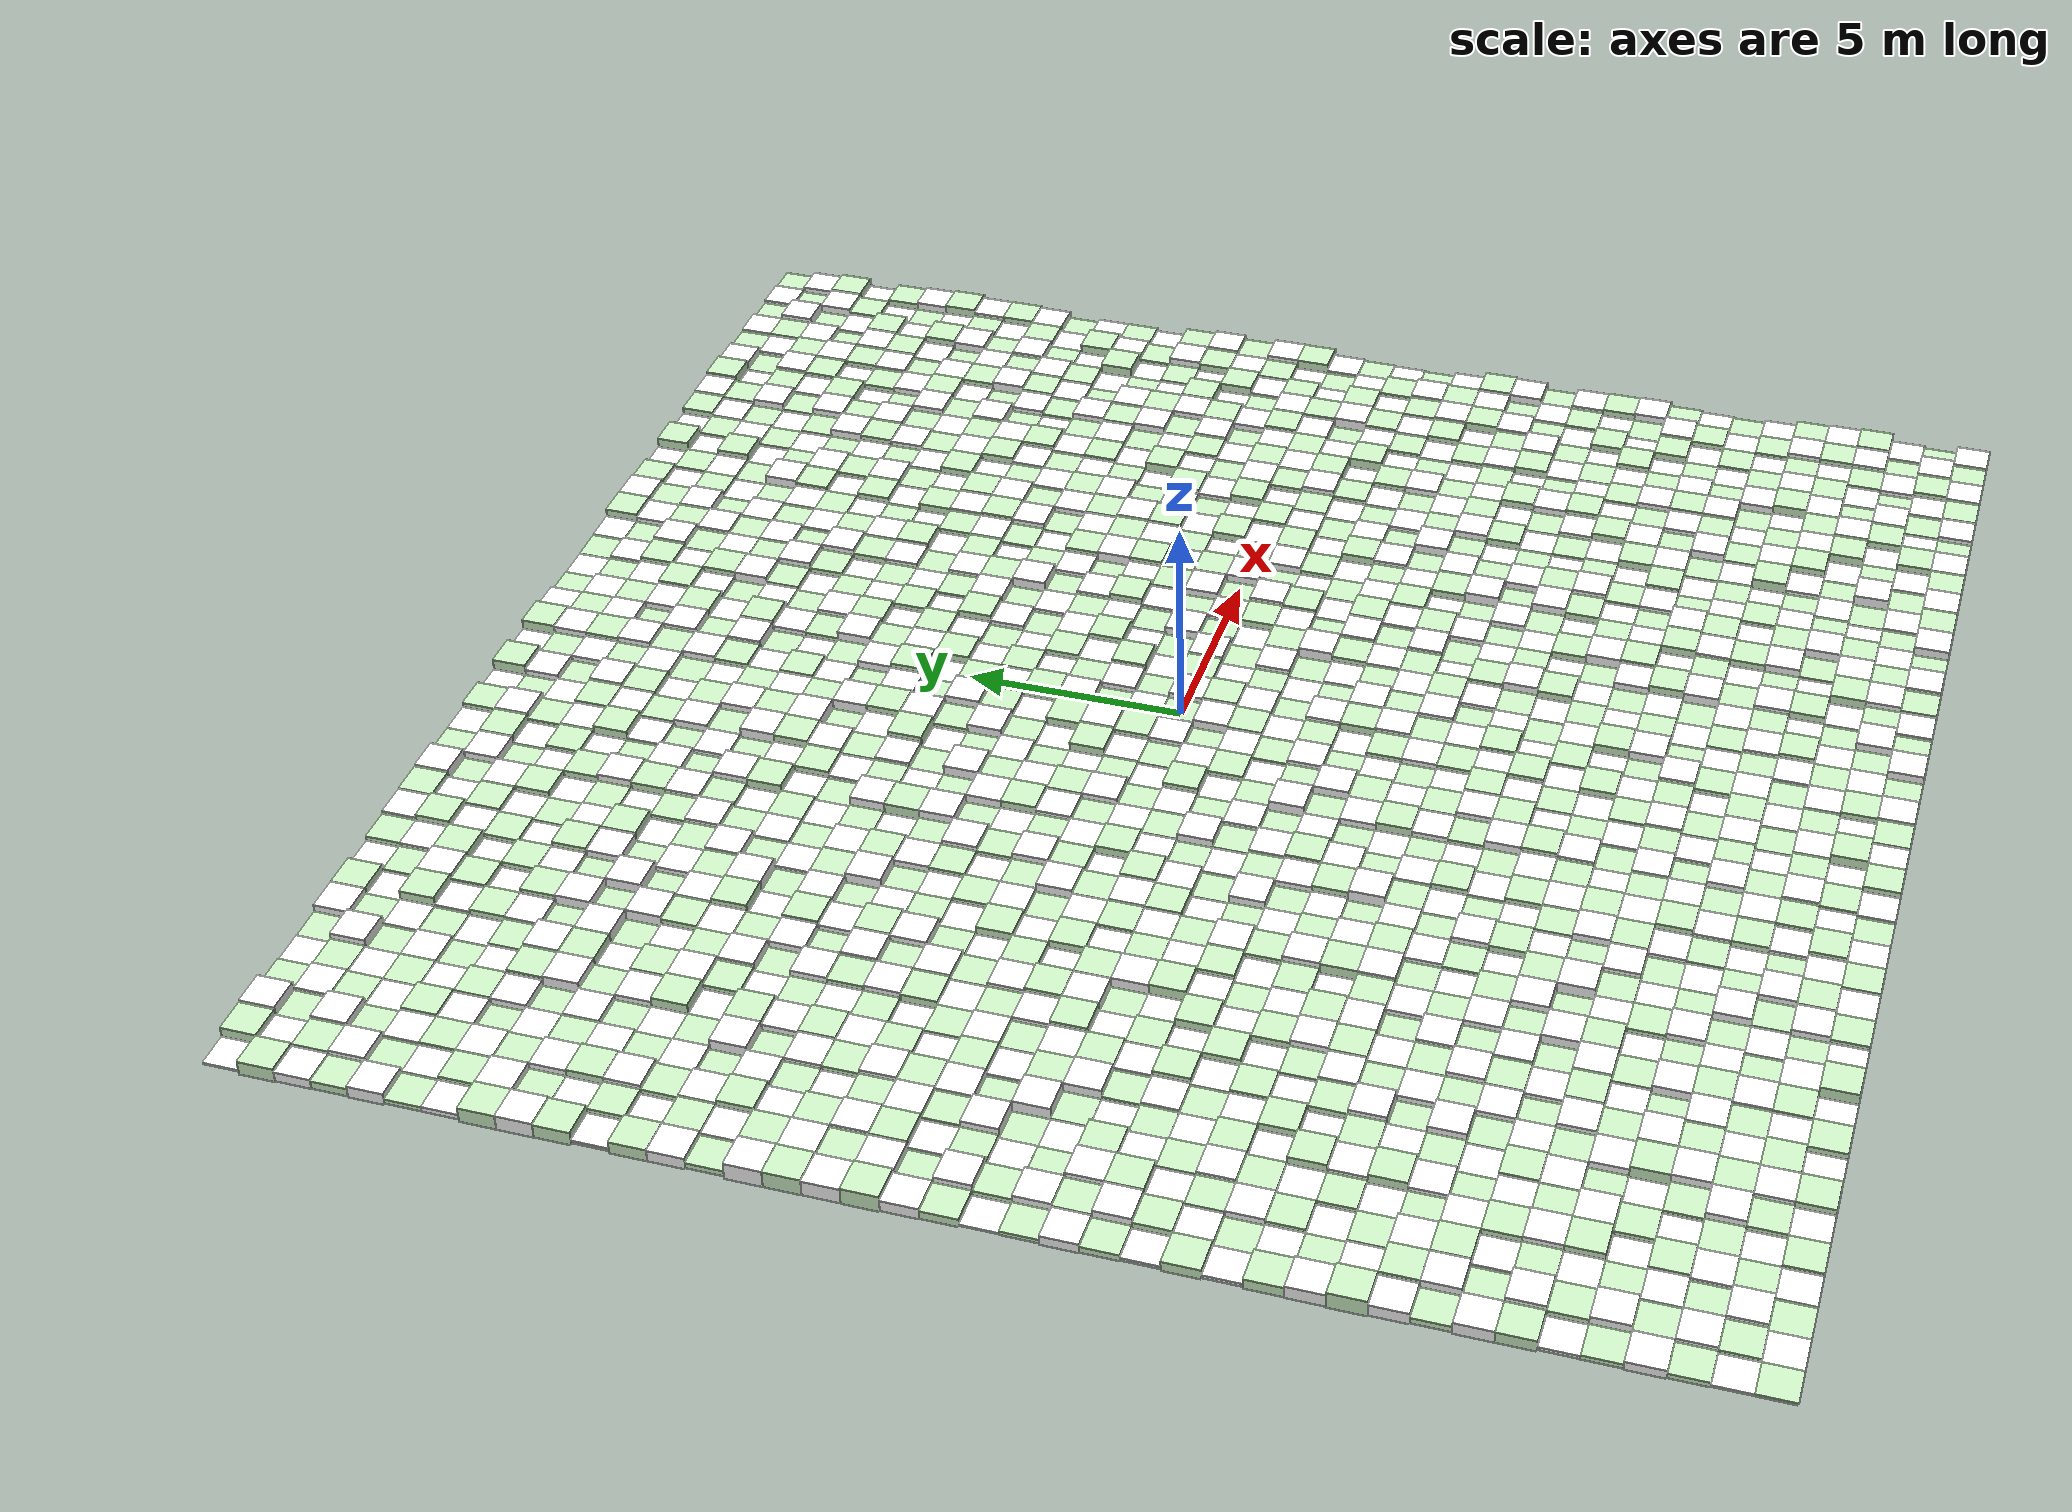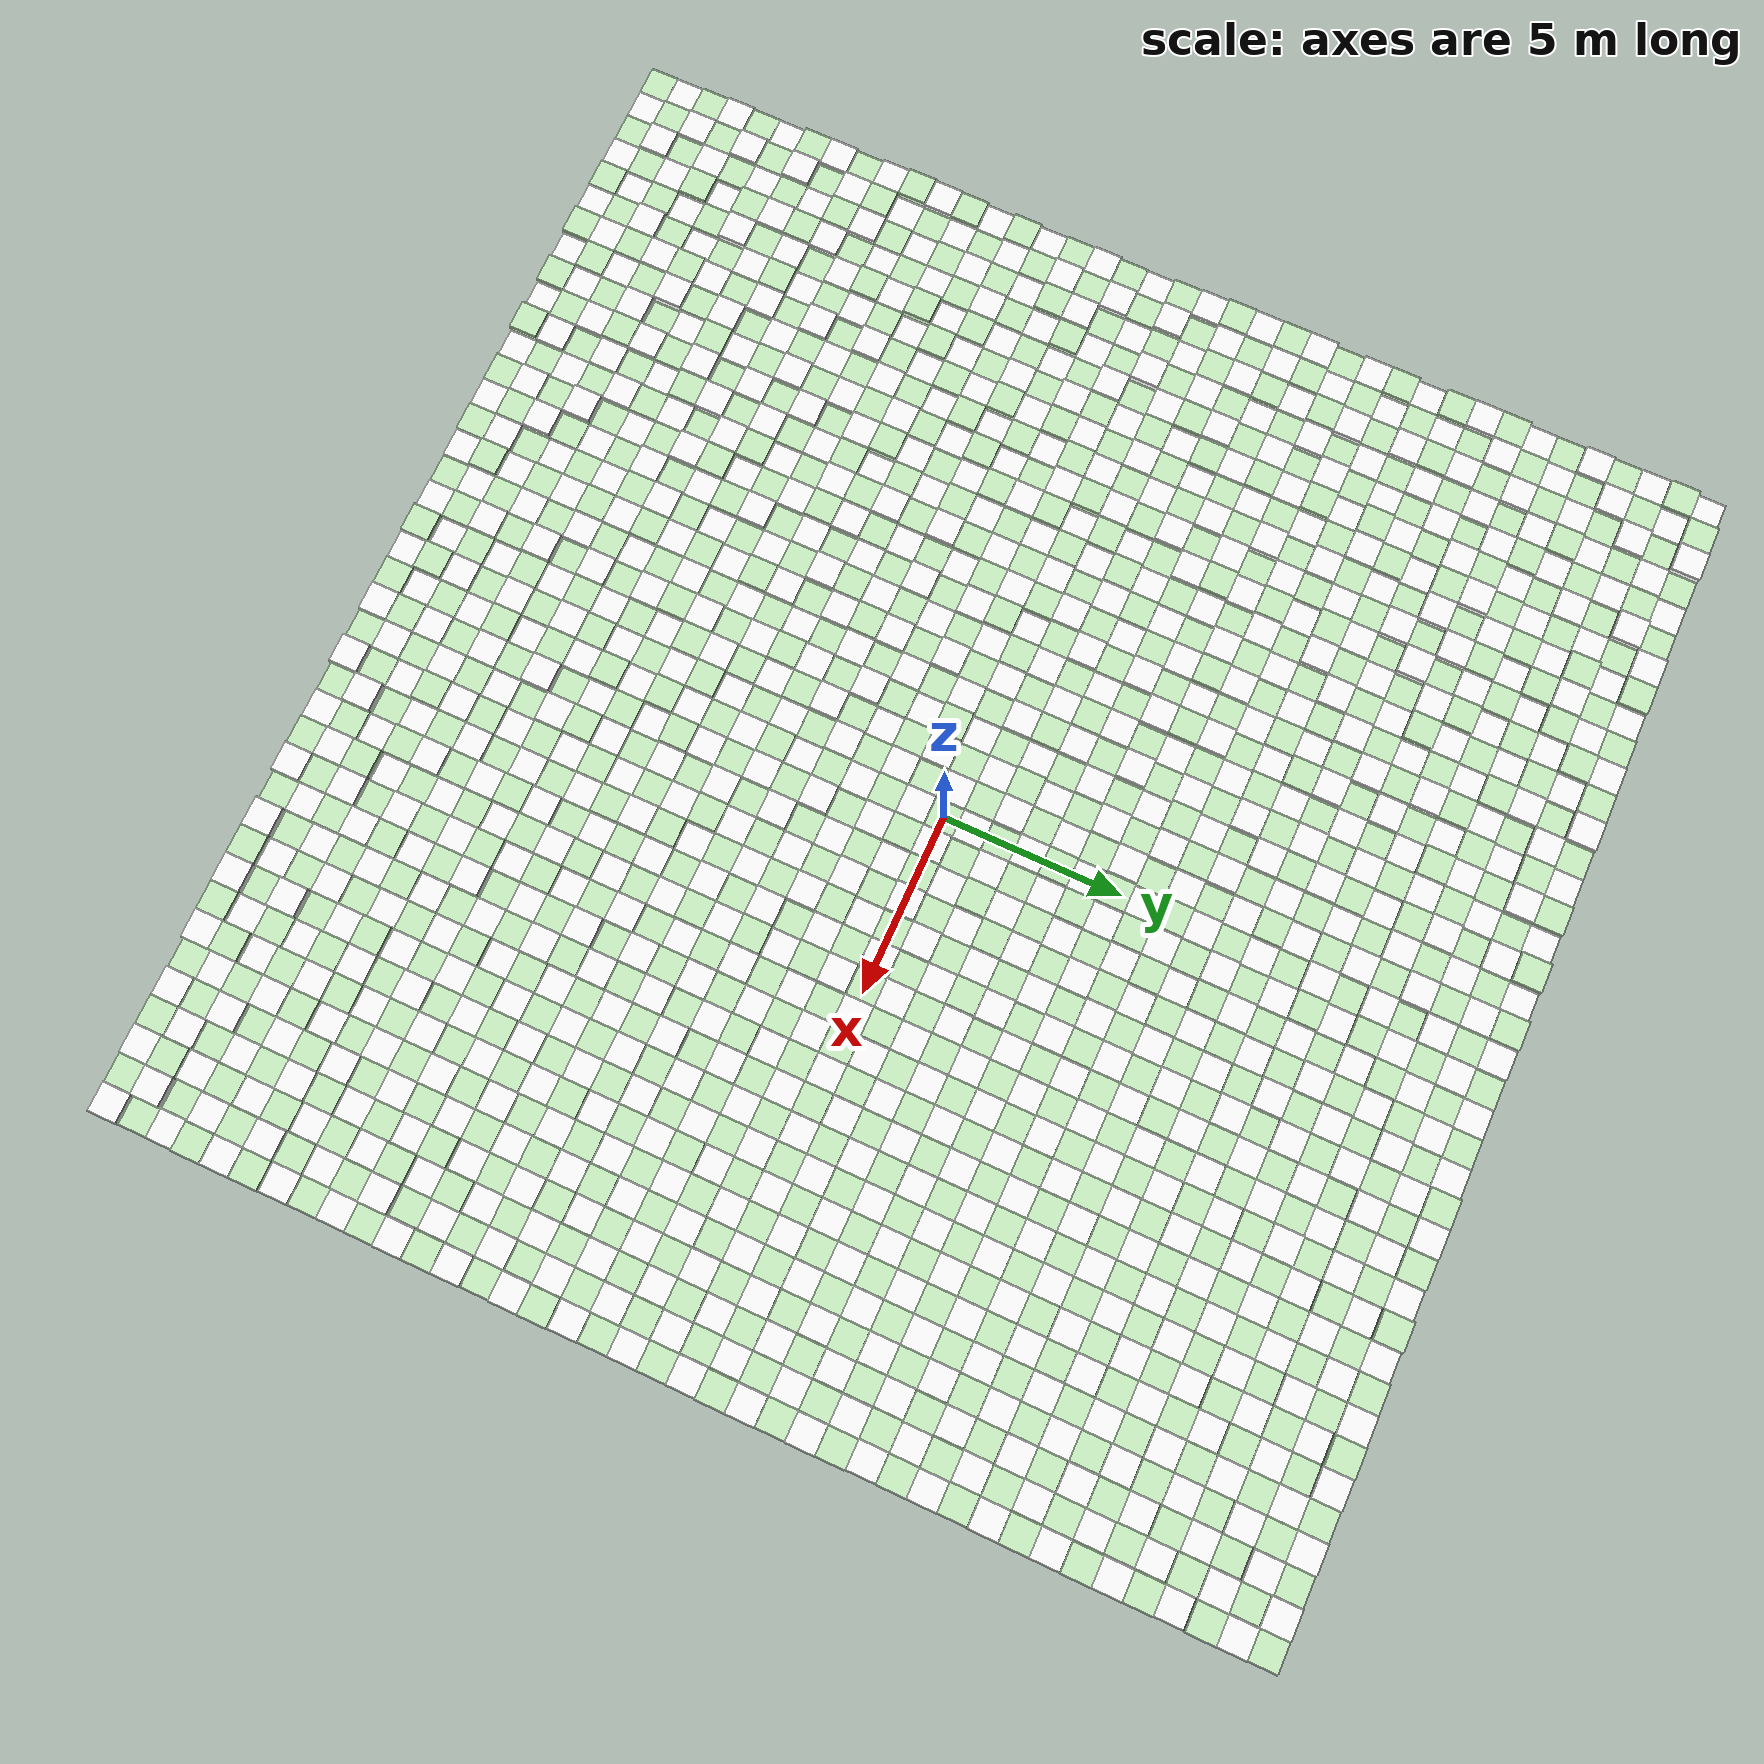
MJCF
<?xml version="1.0" ?>
<mujoco model="tensegrity">
  <worldbody>
    <geom name="cube_-20_-20" type="box" size="0.4 0.4 0.02824148476985694" pos="-16.0 -16.0 0.01412074238492847" rgba="0.8 0.95 0.77 1"/>
    <geom name="cube_-20_-19" type="box" size="0.4 0.4 0.02103701880598904" pos="-16.0 -15.200000000000001 0.01051850940299452" rgba="1 1 1 1"/>
    <geom name="cube_-20_-18" type="box" size="0.4 0.4 0.05926399754036434" pos="-16.0 -14.4 0.02963199877018217" rgba="0.8 0.95 0.77 1"/>
    <geom name="cube_-20_-17" type="box" size="0.4 0.4 0.1044229840963405" pos="-16.0 -13.600000000000001 0.05221149204817025" rgba="1 1 1 1"/>
    <geom name="cube_-20_-16" type="box" size="0.4 0.4 0.054390579147104136" pos="-16.0 -12.8 0.027195289573552068" rgba="0.8 0.95 0.77 1"/>
    <geom name="cube_-20_-15" type="box" size="0.4 0.4 0.03819822972995633" pos="-16.0 -12.0 0.019099114864978166" rgba="1 1 1 1"/>
    <geom name="cube_-20_-14" type="box" size="0.4 0.4 0.13658687685680823" pos="-16.0 -11.200000000000001 0.06829343842840412" rgba="0.8 0.95 0.77 1"/>
    <geom name="cube_-20_-13" type="box" size="0.4 0.4 0.14288034695200078" pos="-16.0 -10.4 0.07144017347600039" rgba="1 1 1 1"/>
    <geom name="cube_-20_-12" type="box" size="0.4 0.4 0.07076025156647255" pos="-16.0 -9.600000000000001 0.03538012578323627" rgba="0.8 0.95 0.77 1"/>
    <geom name="cube_-20_-11" type="box" size="0.4 0.4 0.137778108455919" pos="-16.0 -8.8 0.0688890542279595" rgba="1 1 1 1"/>
    <geom name="cube_-20_-10" type="box" size="0.4 0.4 0.19468054215114663" pos="-16.0 -8.0 0.09734027107557332" rgba="0.8 0.95 0.77 1"/>
    <geom name="cube_-20_-9" type="box" size="0.4 0.4 0.1510769667068327" pos="-16.0 -7.2 0.07553848335341636" rgba="1 1 1 1"/>
    <geom name="cube_-20_-8" type="box" size="0.4 0.4 0.1228860842924246" pos="-16.0 -6.4 0.0614430421462123" rgba="0.8 0.95 0.77 1"/>
    <geom name="cube_-20_-7" type="box" size="0.4 0.4 0.036708333919669246" pos="-16.0 -5.6000000000000005 0.018354166959834623" rgba="1 1 1 1"/>
    <geom name="cube_-20_-6" type="box" size="0.4 0.4 0.11948090153995505" pos="-16.0 -4.800000000000001 0.05974045076997753" rgba="0.8 0.95 0.77 1"/>
    <geom name="cube_-20_-5" type="box" size="0.4 0.4 0.0335689573818175" pos="-16.0 -4.0 0.01678447869090875" rgba="1 1 1 1"/>
    <geom name="cube_-20_-4" type="box" size="0.4 0.4 0.07690707692620918" pos="-16.0 -3.2 0.03845353846310459" rgba="0.8 0.95 0.77 1"/>
    <geom name="cube_-20_-3" type="box" size="0.4 0.4 0.1148616809084708" pos="-16.0 -2.4000000000000004 0.0574308404542354" rgba="1 1 1 1"/>
    <geom name="cube_-20_-2" type="box" size="0.4 0.4 0.04642572338123933" pos="-16.0 -1.6 0.023212861690619663" rgba="0.8 0.95 0.77 1"/>
    <geom name="cube_-20_-1" type="box" size="0.4 0.4 0.01465603129836254" pos="-16.0 -0.8 0.00732801564918127" rgba="1 1 1 1"/>
    <geom name="cube_-20_0" type="box" size="0.4 0.4 0.10195129486904864" pos="-16.0 0.0 0.05097564743452432" rgba="0.8 0.95 0.77 1"/>
    <geom name="cube_-20_1" type="box" size="0.4 0.4 0.1347837468194037" pos="-16.0 0.8 0.06739187340970185" rgba="1 1 1 1"/>
    <geom name="cube_-20_2" type="box" size="0.4 0.4 0.19990980723818114" pos="-16.0 1.6 0.09995490361909057" rgba="0.8 0.95 0.77 1"/>
    <geom name="cube_-20_3" type="box" size="0.4 0.4 0.1828995216379528" pos="-16.0 2.4000000000000004 0.0914497608189764" rgba="1 1 1 1"/>
    <geom name="cube_-20_4" type="box" size="0.4 0.4 0.2006986056159514" pos="-16.0 3.2 0.1003493028079757" rgba="0.8 0.95 0.77 1"/>
    <geom name="cube_-20_5" type="box" size="0.4 0.4 0.2036995675159784" pos="-16.0 4.0 0.1018497837579892" rgba="1 1 1 1"/>
    <geom name="cube_-20_6" type="box" size="0.4 0.4 0.06657802735245616" pos="-16.0 4.800000000000001 0.03328901367622808" rgba="0.8 0.95 0.77 1"/>
    <geom name="cube_-20_7" type="box" size="0.4 0.4 0.1404980141257692" pos="-16.0 5.6000000000000005 0.0702490070628846" rgba="1 1 1 1"/>
    <geom name="cube_-20_8" type="box" size="0.4 0.4 0.1492742365342049" pos="-16.0 6.4 0.07463711826710245" rgba="0.8 0.95 0.77 1"/>
    <geom name="cube_-20_9" type="box" size="0.4 0.4 0.03460133296923681" pos="-16.0 7.2 0.017300666484618404" rgba="1 1 1 1"/>
    <geom name="cube_-20_10" type="box" size="0.4 0.4 0.16561546398424576" pos="-16.0 8.0 0.08280773199212288" rgba="0.8 0.95 0.77 1"/>
    <geom name="cube_-20_11" type="box" size="0.4 0.4 0.18394439007730085" pos="-16.0 8.8 0.09197219503865042" rgba="1 1 1 1"/>
    <geom name="cube_-20_12" type="box" size="0.4 0.4 0.1824220597404699" pos="-16.0 9.600000000000001 0.09121102987023495" rgba="0.8 0.95 0.77 1"/>
    <geom name="cube_-20_13" type="box" size="0.4 0.4 0.0609538793727518" pos="-16.0 10.4 0.0304769396863759" rgba="1 1 1 1"/>
    <geom name="cube_-20_14" type="box" size="0.4 0.4 0.05582134409079854" pos="-16.0 11.200000000000001 0.02791067204539927" rgba="0.8 0.95 0.77 1"/>
    <geom name="cube_-20_15" type="box" size="0.4 0.4 0.14505635821705404" pos="-16.0 12.0 0.07252817910852702" rgba="1 1 1 1"/>
    <geom name="cube_-20_16" type="box" size="0.4 0.4 0.09866762876233526" pos="-16.0 12.8 0.04933381438116763" rgba="0.8 0.95 0.77 1"/>
    <geom name="cube_-20_17" type="box" size="0.4 0.4 0.11973120686162238" pos="-16.0 13.600000000000001 0.05986560343081119" rgba="1 1 1 1"/>
    <geom name="cube_-20_18" type="box" size="0.4 0.4 0.1714473972983605" pos="-16.0 14.4 0.08572369864918025" rgba="0.8 0.95 0.77 1"/>
    <geom name="cube_-20_19" type="box" size="0.4 0.4 0.015307530310326603" pos="-16.0 15.200000000000001 0.007653765155163301" rgba="1 1 1 1"/>
    <geom name="cube_-19_-20" type="box" size="0.4 0.4 0.02661198569877722" pos="-15.200000000000001 -16.0 0.01330599284938861" rgba="1 1 1 1"/>
    <geom name="cube_-19_-19" type="box" size="0.4 0.4 0.0750521194874181" pos="-15.200000000000001 -15.200000000000001 0.03752605974370905" rgba="0.8 0.95 0.77 1"/>
    <geom name="cube_-19_-18" type="box" size="0.4 0.4 0.11677819662083103" pos="-15.200000000000001 -14.4 0.05838909831041551" rgba="1 1 1 1"/>
    <geom name="cube_-19_-17" type="box" size="0.4 0.4 0.09254478687295774" pos="-15.200000000000001 -13.600000000000001 0.04627239343647887" rgba="0.8 0.95 0.77 1"/>
    <geom name="cube_-19_-16" type="box" size="0.4 0.4 0.1787650587934649" pos="-15.200000000000001 -12.8 0.08938252939673245" rgba="1 1 1 1"/>
    <geom name="cube_-19_-15" type="box" size="0.4 0.4 0.12418418748968377" pos="-15.200000000000001 -12.0 0.062092093744841884" rgba="0.8 0.95 0.77 1"/>
    <geom name="cube_-19_-14" type="box" size="0.4 0.4 0.20349231278210594" pos="-15.200000000000001 -11.200000000000001 0.10174615639105297" rgba="1 1 1 1"/>
    <geom name="cube_-19_-13" type="box" size="0.4 0.4 0.054930216063846744" pos="-15.200000000000001 -10.4 0.027465108031923372" rgba="0.8 0.95 0.77 1"/>
    <geom name="cube_-19_-12" type="box" size="0.4 0.4 0.1897035989694698" pos="-15.200000000000001 -9.600000000000001 0.0948517994847349" rgba="1 1 1 1"/>
    <geom name="cube_-19_-11" type="box" size="0.4 0.4 0.19086724847998188" pos="-15.200000000000001 -8.8 0.09543362423999094" rgba="0.8 0.95 0.77 1"/>
    <geom name="cube_-19_-10" type="box" size="0.4 0.4 0.04663356552822312" pos="-15.200000000000001 -8.0 0.02331678276411156" rgba="1 1 1 1"/>
    <geom name="cube_-19_-9" type="box" size="0.4 0.4 0.028048706462859587" pos="-15.200000000000001 -7.2 0.014024353231429794" rgba="0.8 0.95 0.77 1"/>
    <geom name="cube_-19_-8" type="box" size="0.4 0.4 0.03008458665831845" pos="-15.200000000000001 -6.4 0.015042293329159224" rgba="1 1 1 1"/>
    <geom name="cube_-19_-7" type="box" size="0.4 0.4 0.01711460036992102" pos="-15.200000000000001 -5.6000000000000005 0.00855730018496051" rgba="0.8 0.95 0.77 1"/>
    <geom name="cube_-19_-6" type="box" size="0.4 0.4 0.07723990724187352" pos="-15.200000000000001 -4.800000000000001 0.03861995362093676" rgba="1 1 1 1"/>
    <geom name="cube_-19_-5" type="box" size="0.4 0.4 0.13291575176186163" pos="-15.200000000000001 -4.0 0.06645787588093081" rgba="0.8 0.95 0.77 1"/>
    <geom name="cube_-19_-4" type="box" size="0.4 0.4 0.19528285882007654" pos="-15.200000000000001 -3.2 0.09764142941003827" rgba="1 1 1 1"/>
    <geom name="cube_-19_-3" type="box" size="0.4 0.4 0.1285890304312922" pos="-15.200000000000001 -2.4000000000000004 0.0642945152156461" rgba="0.8 0.95 0.77 1"/>
    <geom name="cube_-19_-2" type="box" size="0.4 0.4 0.16245549657992223" pos="-15.200000000000001 -1.6 0.08122774828996111" rgba="1 1 1 1"/>
    <geom name="cube_-19_-1" type="box" size="0.4 0.4 0.09445223919761579" pos="-15.200000000000001 -0.8 0.047226119598807896" rgba="0.8 0.95 0.77 1"/>
    <geom name="cube_-19_0" type="box" size="0.4 0.4 0.19186290265372047" pos="-15.200000000000001 0.0 0.09593145132686023" rgba="1 1 1 1"/>
    <geom name="cube_-19_1" type="box" size="0.4 0.4 0.03129925205008514" pos="-15.200000000000001 0.8 0.01564962602504257" rgba="0.8 0.95 0.77 1"/>
    <geom name="cube_-19_2" type="box" size="0.4 0.4 0.157584695056681" pos="-15.200000000000001 1.6 0.0787923475283405" rgba="1 1 1 1"/>
    <geom name="cube_-19_3" type="box" size="0.4 0.4 0.1467635151428932" pos="-15.200000000000001 2.4000000000000004 0.0733817575714466" rgba="0.8 0.95 0.77 1"/>
    <geom name="cube_-19_4" type="box" size="0.4 0.4 0.18338604925123075" pos="-15.200000000000001 3.2 0.09169302462561538" rgba="1 1 1 1"/>
    <geom name="cube_-19_5" type="box" size="0.4 0.4 0.18059569706475004" pos="-15.200000000000001 4.0 0.09029784853237502" rgba="0.8 0.95 0.77 1"/>
    <geom name="cube_-19_6" type="box" size="0.4 0.4 0.09935869155743929" pos="-15.200000000000001 4.800000000000001 0.049679345778719644" rgba="1 1 1 1"/>
    <geom name="cube_-19_7" type="box" size="0.4 0.4 0.13018398760601443" pos="-15.200000000000001 5.6000000000000005 0.06509199380300722" rgba="0.8 0.95 0.77 1"/>
    <geom name="cube_-19_8" type="box" size="0.4 0.4 0.024840390049003083" pos="-15.200000000000001 6.4 0.012420195024501542" rgba="1 1 1 1"/>
    <geom name="cube_-19_9" type="box" size="0.4 0.4 0.10956901362909117" pos="-15.200000000000001 7.2 0.05478450681454559" rgba="0.8 0.95 0.77 1"/>
    <geom name="cube_-19_10" type="box" size="0.4 0.4 0.0547271512935633" pos="-15.200000000000001 8.0 0.02736357564678165" rgba="1 1 1 1"/>
    <geom name="cube_-19_11" type="box" size="0.4 0.4 0.0650419453280058" pos="-15.200000000000001 8.8 0.0325209726640029" rgba="0.8 0.95 0.77 1"/>
    <geom name="cube_-19_12" type="box" size="0.4 0.4 0.168553838434824" pos="-15.200000000000001 9.600000000000001 0.084276919217412" rgba="1 1 1 1"/>
    <geom name="cube_-19_13" type="box" size="0.4 0.4 0.12496887321627399" pos="-15.200000000000001 10.4 0.062484436608136996" rgba="0.8 0.95 0.77 1"/>
    <geom name="cube_-19_14" type="box" size="0.4 0.4 0.07617377474293892" pos="-15.200000000000001 11.200000000000001 0.03808688737146946" rgba="1 1 1 1"/>
    <geom name="cube_-19_15" type="box" size="0.4 0.4 0.0707371973642917" pos="-15.200000000000001 12.0 0.03536859868214585" rgba="0.8 0.95 0.77 1"/>
    <geom name="cube_-19_16" type="box" size="0.4 0.4 0.17452743810341023" pos="-15.200000000000001 12.8 0.08726371905170512" rgba="1 1 1 1"/>
    <geom name="cube_-19_17" type="box" size="0.4 0.4 0.15246571948725116" pos="-15.200000000000001 13.600000000000001 0.07623285974362558" rgba="0.8 0.95 0.77 1"/>
    <geom name="cube_-19_18" type="box" size="0.4 0.4 0.0785138588732262" pos="-15.200000000000001 14.4 0.0392569294366131" rgba="1 1 1 1"/>
    <geom name="cube_-19_19" type="box" size="0.4 0.4 0.17306940162959794" pos="-15.200000000000001 15.200000000000001 0.08653470081479897" rgba="0.8 0.95 0.77 1"/>
    <geom name="cube_-18_-20" type="box" size="0.4 0.4 0.024663174869227856" pos="-14.4 -16.0 0.012331587434613928" rgba="0.8 0.95 0.77 1"/>
    <geom name="cube_-18_-19" type="box" size="0.4 0.4 0.13077045341904334" pos="-14.4 -15.200000000000001 0.06538522670952167" rgba="1 1 1 1"/>
    <geom name="cube_-18_-18" type="box" size="0.4 0.4 0.041791753940535324" pos="-14.4 -14.4 0.020895876970267662" rgba="0.8 0.95 0.77 1"/>
    <geom name="cube_-18_-17" type="box" size="0.4 0.4 0.11097589674789919" pos="-14.4 -13.600000000000001 0.055487948373949596" rgba="1 1 1 1"/>
    <geom name="cube_-18_-16" type="box" size="0.4 0.4 0.08567870310274531" pos="-14.4 -12.8 0.042839351551372654" rgba="0.8 0.95 0.77 1"/>
    <geom name="cube_-18_-15" type="box" size="0.4 0.4 0.10093380851710723" pos="-14.4 -12.0 0.050466904258553616" rgba="1 1 1 1"/>
    <geom name="cube_-18_-14" type="box" size="0.4 0.4 0.12280486382561487" pos="-14.4 -11.200000000000001 0.061402431912807434" rgba="0.8 0.95 0.77 1"/>
    <geom name="cube_-18_-13" type="box" size="0.4 0.4 0.0981578470121599" pos="-14.4 -10.4 0.04907892350607995" rgba="1 1 1 1"/>
    <geom name="cube_-18_-12" type="box" size="0.4 0.4 0.1984127788401517" pos="-14.4 -9.600000000000001 0.09920638942007586" rgba="0.8 0.95 0.77 1"/>
    <geom name="cube_-18_-11" type="box" size="0.4 0.4 0.16642211617556174" pos="-14.4 -8.8 0.08321105808778087" rgba="1 1 1 1"/>
    <geom name="cube_-18_-10" type="box" size="0.4 0.4 0.06563991875815665" pos="-14.4 -8.0 0.03281995937907833" rgba="0.8 0.95 0.77 1"/>
    <geom name="cube_-18_-9" type="box" size="0.4 0.4 0.019257232730413455" pos="-14.4 -7.2 0.009628616365206727" rgba="1 1 1 1"/>
    <geom name="cube_-18_-8" type="box" size="0.4 0.4 0.09005759401814084" pos="-14.4 -6.4 0.04502879700907042" rgba="0.8 0.95 0.77 1"/>
    <geom name="cube_-18_-7" type="box" size="0.4 0.4 0.1192501630610041" pos="-14.4 -5.6000000000000005 0.05962508153050205" rgba="1 1 1 1"/>
    <geom name="cube_-18_-6" type="box" size="0.4 0.4 0.10822868628933212" pos="-14.4 -4.800000000000001 0.05411434314466606" rgba="0.8 0.95 0.77 1"/>
    <geom name="cube_-18_-5" type="box" size="0.4 0.4 0.08579244326724214" pos="-14.4 -4.0 0.04289622163362107" rgba="1 1 1 1"/>
    <geom name="cube_-18_-4" type="box" size="0.4 0.4 0.20765646245378894" pos="-14.4 -3.2 0.10382823122689447" rgba="0.8 0.95 0.77 1"/>
    <geom name="cube_-18_-3" type="box" size="0.4 0.4 0.20618484863414857" pos="-14.4 -2.4000000000000004 0.10309242431707429" rgba="1 1 1 1"/>
    <geom name="cube_-18_-2" type="box" size="0.4 0.4 0.02567556138536108" pos="-14.4 -1.6 0.01283778069268054" rgba="0.8 0.95 0.77 1"/>
    <geom name="cube_-18_-1" type="box" size="0.4 0.4 0.031109675141418547" pos="-14.4 -0.8 0.015554837570709273" rgba="1 1 1 1"/>
    <geom name="cube_-18_0" type="box" size="0.4 0.4 0.08448495752707713" pos="-14.4 0.0 0.042242478763538566" rgba="0.8 0.95 0.77 1"/>
    <geom name="cube_-18_1" type="box" size="0.4 0.4 0.0701368237293769" pos="-14.4 0.8 0.03506841186468845" rgba="1 1 1 1"/>
    <geom name="cube_-18_2" type="box" size="0.4 0.4 0.1794271459632697" pos="-14.4 1.6 0.08971357298163485" rgba="0.8 0.95 0.77 1"/>
    <geom name="cube_-18_3" type="box" size="0.4 0.4 0.19785678212784996" pos="-14.4 2.4000000000000004 0.09892839106392498" rgba="1 1 1 1"/>
    <geom name="cube_-18_4" type="box" size="0.4 0.4 0.16183753715145566" pos="-14.4 3.2 0.08091876857572783" rgba="0.8 0.95 0.77 1"/>
    <geom name="cube_-18_5" type="box" size="0.4 0.4 0.11128720322611957" pos="-14.4 4.0 0.055643601613059784" rgba="1 1 1 1"/>
    <geom name="cube_-18_6" type="box" size="0.4 0.4 0.1943060621426818" pos="-14.4 4.800000000000001 0.0971530310713409" rgba="0.8 0.95 0.77 1"/>
    <geom name="cube_-18_7" type="box" size="0.4 0.4 0.1498443011693898" pos="-14.4 5.6000000000000005 0.0749221505846949" rgba="1 1 1 1"/>
    <geom name="cube_-18_8" type="box" size="0.4 0.4 0.10550721360194887" pos="-14.4 6.4 0.052753606800974434" rgba="0.8 0.95 0.77 1"/>
    <geom name="cube_-18_9" type="box" size="0.4 0.4 0.17427143779572485" pos="-14.4 7.2 0.08713571889786242" rgba="1 1 1 1"/>
    <geom name="cube_-18_10" type="box" size="0.4 0.4 0.18099415506746933" pos="-14.4 8.0 0.09049707753373466" rgba="0.8 0.95 0.77 1"/>
    <geom name="cube_-18_11" type="box" size="0.4 0.4 0.16253389432327733" pos="-14.4 8.8 0.08126694716163867" rgba="1 1 1 1"/>
    <geom name="cube_-18_12" type="box" size="0.4 0.4 0.11101844244153532" pos="-14.4 9.600000000000001 0.05550922122076766" rgba="0.8 0.95 0.77 1"/>
    <geom name="cube_-18_13" type="box" size="0.4 0.4 0.13284054846876497" pos="-14.4 10.4 0.06642027423438249" rgba="1 1 1 1"/>
    <geom name="cube_-18_14" type="box" size="0.4 0.4 0.12575759609101117" pos="-14.4 11.200000000000001 0.06287879804550559" rgba="0.8 0.95 0.77 1"/>
    <geom name="cube_-18_15" type="box" size="0.4 0.4 0.11397154697543717" pos="-14.4 12.0 0.056985773487718584" rgba="1 1 1 1"/>
    <geom name="cube_-18_16" type="box" size="0.4 0.4 0.07179544517636792" pos="-14.4 12.8 0.03589772258818396" rgba="0.8 0.95 0.77 1"/>
    <geom name="cube_-18_17" type="box" size="0.4 0.4 0.1913897514997377" pos="-14.4 13.600000000000001 0.09569487574986885" rgba="1 1 1 1"/>
    <geom name="cube_-18_18" type="box" size="0.4 0.4 0.05814433365164705" pos="-14.4 14.4 0.029072166825823524" rgba="0.8 0.95 0.77 1"/>
    <geom name="cube_-18_19" type="box" size="0.4 0.4 0.20528298378542684" pos="-14.4 15.200000000000001 0.10264149189271342" rgba="1 1 1 1"/>
    <geom name="cube_-17_-20" type="box" size="0.4 0.4 0.04735549580521016" pos="-13.600000000000001 -16.0 0.02367774790260508" rgba="1 1 1 1"/>
    <geom name="cube_-17_-19" type="box" size="0.4 0.4 0.06241175461841738" pos="-13.600000000000001 -15.200000000000001 0.03120587730920869" rgba="0.8 0.95 0.77 1"/>
    <geom name="cube_-17_-18" type="box" size="0.4 0.4 0.09198230410173476" pos="-13.600000000000001 -14.4 0.04599115205086738" rgba="1 1 1 1"/>
    <geom name="cube_-17_-17" type="box" size="0.4 0.4 0.14410482410664754" pos="-13.600000000000001 -13.600000000000001 0.07205241205332377" rgba="0.8 0.95 0.77 1"/>
    <geom name="cube_-17_-16" type="box" size="0.4 0.4 0.011145042086046844" pos="-13.600000000000001 -12.8 0.005572521043023422" rgba="1 1 1 1"/>
    <geom name="cube_-17_-15" type="box" size="0.4 0.4 0.20278683059434857" pos="-13.600000000000001 -12.0 0.10139341529717429" rgba="0.8 0.95 0.77 1"/>
    <geom name="cube_-17_-14" type="box" size="0.4 0.4 0.20677056942167368" pos="-13.600000000000001 -11.200000000000001 0.10338528471083684" rgba="1 1 1 1"/>
    <geom name="cube_-17_-13" type="box" size="0.4 0.4 0.1934953396617433" pos="-13.600000000000001 -10.4 0.09674766983087164" rgba="0.8 0.95 0.77 1"/>
    <geom name="cube_-17_-12" type="box" size="0.4 0.4 0.15135870700211823" pos="-13.600000000000001 -9.600000000000001 0.07567935350105912" rgba="1 1 1 1"/>
    <geom name="cube_-17_-11" type="box" size="0.4 0.4 0.0458729228246488" pos="-13.600000000000001 -8.8 0.0229364614123244" rgba="0.8 0.95 0.77 1"/>
    <geom name="cube_-17_-10" type="box" size="0.4 0.4 0.03632782683111792" pos="-13.600000000000001 -8.0 0.01816391341555896" rgba="1 1 1 1"/>
    <geom name="cube_-17_-9" type="box" size="0.4 0.4 0.08216576597158178" pos="-13.600000000000001 -7.2 0.04108288298579089" rgba="0.8 0.95 0.77 1"/>
    <geom name="cube_-17_-8" type="box" size="0.4 0.4 0.08091908308528167" pos="-13.600000000000001 -6.4 0.04045954154264084" rgba="1 1 1 1"/>
    <geom name="cube_-17_-7" type="box" size="0.4 0.4 0.11381976404426719" pos="-13.600000000000001 -5.6000000000000005 0.056909882022133595" rgba="0.8 0.95 0.77 1"/>
    <geom name="cube_-17_-6" type="box" size="0.4 0.4 0.15843315255075757" pos="-13.600000000000001 -4.800000000000001 0.07921657627537879" rgba="1 1 1 1"/>
    <geom name="cube_-17_-5" type="box" size="0.4 0.4 0.11566311953585401" pos="-13.600000000000001 -4.0 0.057831559767927004" rgba="0.8 0.95 0.77 1"/>
    <geom name="cube_-17_-4" type="box" size="0.4 0.4 0.09329318305180533" pos="-13.600000000000001 -3.2 0.04664659152590266" rgba="1 1 1 1"/>
    <geom name="cube_-17_-3" type="box" size="0.4 0.4 0.15899091391437015" pos="-13.600000000000001 -2.4000000000000004 0.07949545695718507" rgba="0.8 0.95 0.77 1"/>
    <geom name="cube_-17_-2" type="box" size="0.4 0.4 0.011485757752120943" pos="-13.600000000000001 -1.6 0.0057428788760604714" rgba="1 1 1 1"/>
    <geom name="cube_-17_-1" type="box" size="0.4 0.4 0.01154692059709698" pos="-13.600000000000001 -0.8 0.00577346029854849" rgba="0.8 0.95 0.77 1"/>
    <geom name="cube_-17_0" type="box" size="0.4 0.4 0.1875268110799287" pos="-13.600000000000001 0.0 0.09376340553996435" rgba="1 1 1 1"/>
    <geom name="cube_-17_1" type="box" size="0.4 0.4 0.112335133394804" pos="-13.600000000000001 0.8 0.056167566697402" rgba="0.8 0.95 0.77 1"/>
    <geom name="cube_-17_2" type="box" size="0.4 0.4 0.173999699228082" pos="-13.600000000000001 1.6 0.086999849614041" rgba="1 1 1 1"/>
    <geom name="cube_-17_3" type="box" size="0.4 0.4 0.13023008064695984" pos="-13.600000000000001 2.4000000000000004 0.06511504032347992" rgba="0.8 0.95 0.77 1"/>
    <geom name="cube_-17_4" type="box" size="0.4 0.4 0.0498837543708725" pos="-13.600000000000001 3.2 0.02494187718543625" rgba="1 1 1 1"/>
    <geom name="cube_-17_5" type="box" size="0.4 0.4 0.0723312131457312" pos="-13.600000000000001 4.0 0.0361656065728656" rgba="0.8 0.95 0.77 1"/>
    <geom name="cube_-17_6" type="box" size="0.4 0.4 0.14293339088546853" pos="-13.600000000000001 4.800000000000001 0.07146669544273426" rgba="1 1 1 1"/>
    <geom name="cube_-17_7" type="box" size="0.4 0.4 0.010811130605712229" pos="-13.600000000000001 5.6000000000000005 0.0054055653028561145" rgba="0.8 0.95 0.77 1"/>
    <geom name="cube_-17_8" type="box" size="0.4 0.4 0.07380242698763502" pos="-13.600000000000001 6.4 0.03690121349381751" rgba="1 1 1 1"/>
    <geom name="cube_-17_9" type="box" size="0.4 0.4 0.058932576900416346" pos="-13.600000000000001 7.2 0.029466288450208173" rgba="0.8 0.95 0.77 1"/>
    <geom name="cube_-17_10" type="box" size="0.4 0.4 0.09115257511993524" pos="-13.600000000000001 8.0 0.04557628755996762" rgba="1 1 1 1"/>
    <geom name="cube_-17_11" type="box" size="0.4 0.4 0.08775203800462104" pos="-13.600000000000001 8.8 0.04387601900231052" rgba="0.8 0.95 0.77 1"/>
    <geom name="cube_-17_12" type="box" size="0.4 0.4 0.09856180486701274" pos="-13.600000000000001 9.600000000000001 0.04928090243350637" rgba="1 1 1 1"/>
    <geom name="cube_-17_13" type="box" size="0.4 0.4 0.01252045748193297" pos="-13.600000000000001 10.4 0.006260228740966485" rgba="0.8 0.95 0.77 1"/>
    <geom name="cube_-17_14" type="box" size="0.4 0.4 0.10743365708057964" pos="-13.600000000000001 11.200000000000001 0.05371682854028982" rgba="1 1 1 1"/>
    <geom name="cube_-17_15" type="box" size="0.4 0.4 0.14952400578922" pos="-13.600000000000001 12.0 0.07476200289461" rgba="0.8 0.95 0.77 1"/>
    <geom name="cube_-17_16" type="box" size="0.4 0.4 0.06853792756314395" pos="-13.600000000000001 12.8 0.03426896378157197" rgba="1 1 1 1"/>
    <geom name="cube_-17_17" type="box" size="0.4 0.4 0.08627440550290129" pos="-13.600000000000001 13.600000000000001 0.043137202751450644" rgba="0.8 0.95 0.77 1"/>
    <geom name="cube_-17_18" type="box" size="0.4 0.4 0.1086731375681409" pos="-13.600000000000001 14.4 0.05433656878407045" rgba="1 1 1 1"/>
    <geom name="cube_-17_19" type="box" size="0.4 0.4 0.04703386534746329" pos="-13.600000000000001 15.200000000000001 0.023516932673731644" rgba="0.8 0.95 0.77 1"/>
    <geom name="cube_-16_-20" type="box" size="0.4 0.4 0.09570641889211705" pos="-12.8 -16.0 0.047853209446058524" rgba="0.8 0.95 0.77 1"/>
    <geom name="cube_-16_-19" type="box" size="0.4 0.4 0.029526949487383315" pos="-12.8 -15.200000000000001 0.014763474743691657" rgba="1 1 1 1"/>
    <geom name="cube_-16_-18" type="box" size="0.4 0.4 0.086610629460897" pos="-12.8 -14.4 0.0433053147304485" rgba="0.8 0.95 0.77 1"/>
    <geom name="cube_-16_-17" type="box" size="0.4 0.4 0.025817023917357396" pos="-12.8 -13.600000000000001 0.012908511958678698" rgba="1 1 1 1"/>
    <geom name="cube_-16_-16" type="box" size="0.4 0.4 0.08276293241379863" pos="-12.8 -12.8 0.041381466206899316" rgba="0.8 0.95 0.77 1"/>
    <geom name="cube_-16_-15" type="box" size="0.4 0.4 0.1894929953730216" pos="-12.8 -12.0 0.0947464976865108" rgba="1 1 1 1"/>
    <geom name="cube_-16_-14" type="box" size="0.4 0.4 0.12381884294198915" pos="-12.8 -11.200000000000001 0.061909421470994576" rgba="0.8 0.95 0.77 1"/>
    <geom name="cube_-16_-13" type="box" size="0.4 0.4 0.12471016360836489" pos="-12.8 -10.4 0.06235508180418244" rgba="1 1 1 1"/>
    <geom name="cube_-16_-12" type="box" size="0.4 0.4 0.026272839041013376" pos="-12.8 -9.600000000000001 0.013136419520506688" rgba="0.8 0.95 0.77 1"/>
    <geom name="cube_-16_-11" type="box" size="0.4 0.4 0.11248218482117266" pos="-12.8 -8.8 0.05624109241058633" rgba="1 1 1 1"/>
    <geom name="cube_-16_-10" type="box" size="0.4 0.4 0.18640476828321548" pos="-12.8 -8.0 0.09320238414160774" rgba="0.8 0.95 0.77 1"/>
    <geom name="cube_-16_-9" type="box" size="0.4 0.4 0.13970474164609267" pos="-12.8 -7.2 0.06985237082304634" rgba="1 1 1 1"/>
    <geom name="cube_-16_-8" type="box" size="0.4 0.4 0.20867134498523812" pos="-12.8 -6.4 0.10433567249261906" rgba="0.8 0.95 0.77 1"/>
    <geom name="cube_-16_-7" type="box" size="0.4 0.4 0.052525317163434816" pos="-12.8 -5.6000000000000005 0.026262658581717408" rgba="1 1 1 1"/>
    <geom name="cube_-16_-6" type="box" size="0.4 0.4 0.1453163271041689" pos="-12.8 -4.800000000000001 0.07265816355208445" rgba="0.8 0.95 0.77 1"/>
    <geom name="cube_-16_-5" type="box" size="0.4 0.4 0.06267034725044031" pos="-12.8 -4.0 0.031335173625220154" rgba="1 1 1 1"/>
    <geom name="cube_-16_-4" type="box" size="0.4 0.4 0.0676161456849826" pos="-12.8 -3.2 0.0338080728424913" rgba="0.8 0.95 0.77 1"/>
    <geom name="cube_-16_-3" type="box" size="0.4 0.4 0.016426031601322912" pos="-12.8 -2.4000000000000004 0.008213015800661456" rgba="1 1 1 1"/>
    <geom name="cube_-16_-2" type="box" size="0.4 0.4 0.025246998844980197" pos="-12.8 -1.6 0.012623499422490098" rgba="0.8 0.95 0.77 1"/>
    <geom name="cube_-16_-1" type="box" size="0.4 0.4 0.19634839837038323" pos="-12.8 -0.8 0.09817419918519162" rgba="1 1 1 1"/>
    <geom name="cube_-16_0" type="box" size="0.4 0.4 0.016894819276491158" pos="-12.8 0.0 0.008447409638245579" rgba="0.8 0.95 0.77 1"/>
    <geom name="cube_-16_1" type="box" size="0.4 0.4 0.14651509901577" pos="-12.8 0.8 0.073257549507885" rgba="1 1 1 1"/>
    <geom name="cube_-16_2" type="box" size="0.4 0.4 0.16416955265487992" pos="-12.8 1.6 0.08208477632743996" rgba="0.8 0.95 0.77 1"/>
    <geom name="cube_-16_3" type="box" size="0.4 0.4 0.195232502997309" pos="-12.8 2.4000000000000004 0.0976162514986545" rgba="1 1 1 1"/>
    <geom name="cube_-16_4" type="box" size="0.4 0.4 0.1246170574284633" pos="-12.8 3.2 0.06230852871423165" rgba="0.8 0.95 0.77 1"/>
    <geom name="cube_-16_5" type="box" size="0.4 0.4 0.13387820333466102" pos="-12.8 4.0 0.06693910166733051" rgba="1 1 1 1"/>
    <geom name="cube_-16_6" type="box" size="0.4 0.4 0.020612696543921963" pos="-12.8 4.800000000000001 0.010306348271960981" rgba="0.8 0.95 0.77 1"/>
    <geom name="cube_-16_7" type="box" size="0.4 0.4 0.17852564358066841" pos="-12.8 5.6000000000000005 0.08926282179033421" rgba="1 1 1 1"/>
    <geom name="cube_-16_8" type="box" size="0.4 0.4 0.05024698379462088" pos="-12.8 6.4 0.02512349189731044" rgba="0.8 0.95 0.77 1"/>
    <geom name="cube_-16_9" type="box" size="0.4 0.4 0.042154547399219255" pos="-12.8 7.2 0.021077273699609628" rgba="1 1 1 1"/>
    <geom name="cube_-16_10" type="box" size="0.4 0.4 0.02860826631874366" pos="-12.8 8.0 0.01430413315937183" rgba="0.8 0.95 0.77 1"/>
    <geom name="cube_-16_11" type="box" size="0.4 0.4 0.11152850982609319" pos="-12.8 8.8 0.055764254913046596" rgba="1 1 1 1"/>
    <geom name="cube_-16_12" type="box" size="0.4 0.4 0.015692665592544553" pos="-12.8 9.600000000000001 0.007846332796272277" rgba="0.8 0.95 0.77 1"/>
    <geom name="cube_-16_13" type="box" size="0.4 0.4 0.12071875635635017" pos="-12.8 10.4 0.060359378178175084" rgba="1 1 1 1"/>
    <geom name="cube_-16_14" type="box" size="0.4 0.4 0.13440123652984629" pos="-12.8 11.200000000000001 0.06720061826492314" rgba="0.8 0.95 0.77 1"/>
    <geom name="cube_-16_15" type="box" size="0.4 0.4 0.05799225575491468" pos="-12.8 12.0 0.02899612787745734" rgba="1 1 1 1"/>
    <geom name="cube_-16_16" type="box" size="0.4 0.4 0.07565016841592885" pos="-12.8 12.8 0.037825084207964425" rgba="0.8 0.95 0.77 1"/>
    <geom name="cube_-16_17" type="box" size="0.4 0.4 0.07074798755734253" pos="-12.8 13.600000000000001 0.035373993778671266" rgba="1 1 1 1"/>
    <geom name="cube_-16_18" type="box" size="0.4 0.4 0.08899165888482935" pos="-12.8 14.4 0.044495829442414675" rgba="0.8 0.95 0.77 1"/>
    <geom name="cube_-16_19" type="box" size="0.4 0.4 0.02404283521502547" pos="-12.8 15.200000000000001 0.012021417607512736" rgba="1 1 1 1"/>
    <geom name="cube_-15_-20" type="box" size="0.4 0.4 0.0667980746497898" pos="-12.0 -16.0 0.0333990373248949" rgba="1 1 1 1"/>
    <geom name="cube_-15_-19" type="box" size="0.4 0.4 0.10175354349928785" pos="-12.0 -15.200000000000001 0.050876771749643925" rgba="0.8 0.95 0.77 1"/>
    <geom name="cube_-15_-18" type="box" size="0.4 0.4 0.1904470777499163" pos="-12.0 -14.4 0.09522353887495814" rgba="1 1 1 1"/>
    <geom name="cube_-15_-17" type="box" size="0.4 0.4 0.07902453076163175" pos="-12.0 -13.600000000000001 0.03951226538081588" rgba="0.8 0.95 0.77 1"/>
    <geom name="cube_-15_-16" type="box" size="0.4 0.4 0.012020032630289447" pos="-12.0 -12.8 0.006010016315144724" rgba="1 1 1 1"/>
    <geom name="cube_-15_-15" type="box" size="0.4 0.4 0.03096509787778915" pos="-12.0 -12.0 0.015482548938894575" rgba="0.8 0.95 0.77 1"/>
    <geom name="cube_-15_-14" type="box" size="0.4 0.4 0.13167927100810622" pos="-12.0 -11.200000000000001 0.06583963550405311" rgba="1 1 1 1"/>
    <geom name="cube_-15_-13" type="box" size="0.4 0.4 0.16105921127785594" pos="-12.0 -10.4 0.08052960563892797" rgba="0.8 0.95 0.77 1"/>
    <geom name="cube_-15_-12" type="box" size="0.4 0.4 0.02936628950542176" pos="-12.0 -9.600000000000001 0.01468314475271088" rgba="1 1 1 1"/>
    <geom name="cube_-15_-11" type="box" size="0.4 0.4 0.08114452309577004" pos="-12.0 -8.8 0.04057226154788502" rgba="0.8 0.95 0.77 1"/>
    <geom name="cube_-15_-10" type="box" size="0.4 0.4 0.09477430012146403" pos="-12.0 -8.0 0.04738715006073201" rgba="1 1 1 1"/>
    <geom name="cube_-15_-9" type="box" size="0.4 0.4 0.12498776679457922" pos="-12.0 -7.2 0.06249388339728961" rgba="0.8 0.95 0.77 1"/>
    <geom name="cube_-15_-8" type="box" size="0.4 0.4 0.03146730571549069" pos="-12.0 -6.4 0.015733652857745344" rgba="1 1 1 1"/>
    <geom name="cube_-15_-7" type="box" size="0.4 0.4 0.16743840486077147" pos="-12.0 -5.6000000000000005 0.08371920243038573" rgba="0.8 0.95 0.77 1"/>
    <geom name="cube_-15_-6" type="box" size="0.4 0.4 0.07713593955204275" pos="-12.0 -4.800000000000001 0.03856796977602137" rgba="1 1 1 1"/>
    <geom name="cube_-15_-5" type="box" size="0.4 0.4 0.06470677310601457" pos="-12.0 -4.0 0.032353386553007284" rgba="0.8 0.95 0.77 1"/>
    <geom name="cube_-15_-4" type="box" size="0.4 0.4 0.11100571204960362" pos="-12.0 -3.2 0.05550285602480181" rgba="1 1 1 1"/>
    <geom name="cube_-15_-3" type="box" size="0.4 0.4 0.06784525691829847" pos="-12.0 -2.4000000000000004 0.033922628459149236" rgba="0.8 0.95 0.77 1"/>
    <geom name="cube_-15_-2" type="box" size="0.4 0.4 0.17456969936262917" pos="-12.0 -1.6 0.08728484968131459" rgba="1 1 1 1"/>
    <geom name="cube_-15_-1" type="box" size="0.4 0.4 0.15327879391675256" pos="-12.0 -0.8 0.07663939695837628" rgba="0.8 0.95 0.77 1"/>
    <geom name="cube_-15_0" type="box" size="0.4 0.4 0.06211674957219985" pos="-12.0 0.0 0.031058374786099924" rgba="1 1 1 1"/>
    <geom name="cube_-15_1" type="box" size="0.4 0.4 0.1435153993030907" pos="-12.0 0.8 0.07175769965154535" rgba="0.8 0.95 0.77 1"/>
    <geom name="cube_-15_2" type="box" size="0.4 0.4 0.05825672258444833" pos="-12.0 1.6 0.029128361292224163" rgba="1 1 1 1"/>
    <geom name="cube_-15_3" type="box" size="0.4 0.4 0.12130337349964426" pos="-12.0 2.4000000000000004 0.06065168674982213" rgba="0.8 0.95 0.77 1"/>
    <geom name="cube_-15_4" type="box" size="0.4 0.4 0.12121396098981628" pos="-12.0 3.2 0.06060698049490814" rgba="1 1 1 1"/>
    <geom name="cube_-15_5" type="box" size="0.4 0.4 0.1533699459535364" pos="-12.0 4.0 0.0766849729767682" rgba="0.8 0.95 0.77 1"/>
    <geom name="cube_-15_6" type="box" size="0.4 0.4 0.12054721897090973" pos="-12.0 4.800000000000001 0.06027360948545486" rgba="1 1 1 1"/>
    <geom name="cube_-15_7" type="box" size="0.4 0.4 0.17965580803049944" pos="-12.0 5.6000000000000005 0.08982790401524972" rgba="0.8 0.95 0.77 1"/>
    <geom name="cube_-15_8" type="box" size="0.4 0.4 0.03025988212378853" pos="-12.0 6.4 0.015129941061894265" rgba="1 1 1 1"/>
    <geom name="cube_-15_9" type="box" size="0.4 0.4 0.19960796069647202" pos="-12.0 7.2 0.09980398034823601" rgba="0.8 0.95 0.77 1"/>
    <geom name="cube_-15_10" type="box" size="0.4 0.4 0.12402728676658785" pos="-12.0 8.0 0.062013643383293925" rgba="1 1 1 1"/>
    <geom name="cube_-15_11" type="box" size="0.4 0.4 0.08002053439694225" pos="-12.0 8.8 0.040010267198471124" rgba="0.8 0.95 0.77 1"/>
    <geom name="cube_-15_12" type="box" size="0.4 0.4 0.19121430136157924" pos="-12.0 9.600000000000001 0.09560715068078962" rgba="1 1 1 1"/>
    <geom name="cube_-15_13" type="box" size="0.4 0.4 0.17579290872902215" pos="-12.0 10.4 0.08789645436451107" rgba="0.8 0.95 0.77 1"/>
    <geom name="cube_-15_14" type="box" size="0.4 0.4 0.0468742449764996" pos="-12.0 11.200000000000001 0.0234371224882498" rgba="1 1 1 1"/>
    <geom name="cube_-15_15" type="box" size="0.4 0.4 0.013841958157184489" pos="-12.0 12.0 0.0069209790785922445" rgba="0.8 0.95 0.77 1"/>
    <geom name="cube_-15_16" type="box" size="0.4 0.4 0.08012474789796993" pos="-12.0 12.8 0.040062373948984965" rgba="1 1 1 1"/>
    <geom name="cube_-15_17" type="box" size="0.4 0.4 0.02337534717300195" pos="-12.0 13.600000000000001 0.011687673586500975" rgba="0.8 0.95 0.77 1"/>
    <geom name="cube_-15_18" type="box" size="0.4 0.4 0.18601200983757754" pos="-12.0 14.4 0.09300600491878877" rgba="1 1 1 1"/>
    <geom name="cube_-15_19" type="box" size="0.4 0.4 0.01685746424590472" pos="-12.0 15.200000000000001 0.00842873212295236" rgba="0.8 0.95 0.77 1"/>
    <geom name="cube_-14_-20" type="box" size="0.4 0.4 0.1655655419928294" pos="-11.200000000000001 -16.0 0.0827827709964147" rgba="0.8 0.95 0.77 1"/>
    <geom name="cube_-14_-19" type="box" size="0.4 0.4 0.16567637257300485" pos="-11.200000000000001 -15.200000000000001 0.08283818628650243" rgba="1 1 1 1"/>
    <geom name="cube_-14_-18" type="box" size="0.4 0.4 0.1806930076701638" pos="-11.200000000000001 -14.4 0.0903465038350819" rgba="0.8 0.95 0.77 1"/>
    <geom name="cube_-14_-17" type="box" size="0.4 0.4 0.2058656365658972" pos="-11.200000000000001 -13.600000000000001 0.1029328182829486" rgba="1 1 1 1"/>
    <geom name="cube_-14_-16" type="box" size="0.4 0.4 0.20018072948921908" pos="-11.200000000000001 -12.8 0.10009036474460954" rgba="0.8 0.95 0.77 1"/>
    <geom name="cube_-14_-15" type="box" size="0.4 0.4 0.14597143261330983" pos="-11.200000000000001 -12.0 0.07298571630665492" rgba="1 1 1 1"/>
    <geom name="cube_-14_-14" type="box" size="0.4 0.4 0.1020102763601682" pos="-11.200000000000001 -11.200000000000001 0.0510051381800841" rgba="0.8 0.95 0.77 1"/>
    <geom name="cube_-14_-13" type="box" size="0.4 0.4 0.11899265337718952" pos="-11.200000000000001 -10.4 0.05949632668859476" rgba="1 1 1 1"/>
    <geom name="cube_-14_-12" type="box" size="0.4 0.4 0.03743098357882132" pos="-11.200000000000001 -9.600000000000001 0.01871549178941066" rgba="0.8 0.95 0.77 1"/>
    <geom name="cube_-14_-11" type="box" size="0.4 0.4 0.1865528918452845" pos="-11.200000000000001 -8.8 0.09327644592264225" rgba="1 1 1 1"/>
    <geom name="cube_-14_-10" type="box" size="0.4 0.4 0.013714210552357012" pos="-11.200000000000001 -8.0 0.006857105276178506" rgba="0.8 0.95 0.77 1"/>
    <geom name="cube_-14_-9" type="box" size="0.4 0.4 0.2012786275277825" pos="-11.200000000000001 -7.2 0.10063931376389125" rgba="1 1 1 1"/>
    <geom name="cube_-14_-8" type="box" size="0.4 0.4 0.12587247593482373" pos="-11.200000000000001 -6.4 0.06293623796741186" rgba="0.8 0.95 0.77 1"/>
    <geom name="cube_-14_-7" type="box" size="0.4 0.4 0.06546236329779477" pos="-11.200000000000001 -5.6000000000000005 0.032731181648897385" rgba="1 1 1 1"/>
    <geom name="cube_-14_-6" type="box" size="0.4 0.4 0.1278654504845813" pos="-11.200000000000001 -4.800000000000001 0.06393272524229066" rgba="0.8 0.95 0.77 1"/>
    <geom name="cube_-14_-5" type="box" size="0.4 0.4 0.08425223137979833" pos="-11.200000000000001 -4.0 0.042126115689899164" rgba="1 1 1 1"/>
    <geom name="cube_-14_-4" type="box" size="0.4 0.4 0.18870488831310397" pos="-11.200000000000001 -3.2 0.09435244415655199" rgba="0.8 0.95 0.77 1"/>
    <geom name="cube_-14_-3" type="box" size="0.4 0.4 0.10793301789480376" pos="-11.200000000000001 -2.4000000000000004 0.05396650894740188" rgba="1 1 1 1"/>
    <geom name="cube_-14_-2" type="box" size="0.4 0.4 0.15402915459760796" pos="-11.200000000000001 -1.6 0.07701457729880398" rgba="0.8 0.95 0.77 1"/>
    <geom name="cube_-14_-1" type="box" size="0.4 0.4 0.14250703565861955" pos="-11.200000000000001 -0.8 0.07125351782930978" rgba="1 1 1 1"/>
    <geom name="cube_-14_0" type="box" size="0.4 0.4 0.07206140934518936" pos="-11.200000000000001 0.0 0.03603070467259468" rgba="0.8 0.95 0.77 1"/>
    <geom name="cube_-14_1" type="box" size="0.4 0.4 0.13340189073714984" pos="-11.200000000000001 0.8 0.06670094536857492" rgba="1 1 1 1"/>
    <geom name="cube_-14_2" type="box" size="0.4 0.4 0.09262115008602603" pos="-11.200000000000001 1.6 0.046310575043013016" rgba="0.8 0.95 0.77 1"/>
    <geom name="cube_-14_3" type="box" size="0.4 0.4 0.01040994627193185" pos="-11.200000000000001 2.4000000000000004 0.005204973135965925" rgba="1 1 1 1"/>
    <geom name="cube_-14_4" type="box" size="0.4 0.4 0.08027461892989066" pos="-11.200000000000001 3.2 0.04013730946494533" rgba="0.8 0.95 0.77 1"/>
    <geom name="cube_-14_5" type="box" size="0.4 0.4 0.07526947637816346" pos="-11.200000000000001 4.0 0.03763473818908173" rgba="1 1 1 1"/>
    <geom name="cube_-14_6" type="box" size="0.4 0.4 0.08135689688571164" pos="-11.200000000000001 4.800000000000001 0.04067844844285582" rgba="0.8 0.95 0.77 1"/>
    <geom name="cube_-14_7" type="box" size="0.4 0.4 0.04290235991929573" pos="-11.200000000000001 5.6000000000000005 0.021451179959647865" rgba="1 1 1 1"/>
    <geom name="cube_-14_8" type="box" size="0.4 0.4 0.10862708932572816" pos="-11.200000000000001 6.4 0.05431354466286408" rgba="0.8 0.95 0.77 1"/>
    <geom name="cube_-14_9" type="box" size="0.4 0.4 0.17741084432969953" pos="-11.200000000000001 7.2 0.08870542216484976" rgba="1 1 1 1"/>
    <geom name="cube_-14_10" type="box" size="0.4 0.4 0.14545237359325608" pos="-11.200000000000001 8.0 0.07272618679662804" rgba="0.8 0.95 0.77 1"/>
    <geom name="cube_-14_11" type="box" size="0.4 0.4 0.03643332808226368" pos="-11.200000000000001 8.8 0.01821666404113184" rgba="1 1 1 1"/>
    <geom name="cube_-14_12" type="box" size="0.4 0.4 0.18691706900982905" pos="-11.200000000000001 9.600000000000001 0.09345853450491452" rgba="0.8 0.95 0.77 1"/>
    <geom name="cube_-14_13" type="box" size="0.4 0.4 0.206223259232212" pos="-11.200000000000001 10.4 0.103111629616106" rgba="1 1 1 1"/>
    <geom name="cube_-14_14" type="box" size="0.4 0.4 0.07919171760609324" pos="-11.200000000000001 11.200000000000001 0.03959585880304662" rgba="0.8 0.95 0.77 1"/>
    <geom name="cube_-14_15" type="box" size="0.4 0.4 0.01858124439149115" pos="-11.200000000000001 12.0 0.009290622195745574" rgba="1 1 1 1"/>
    <geom name="cube_-14_16" type="box" size="0.4 0.4 0.04048256365264754" pos="-11.200000000000001 12.8 0.02024128182632377" rgba="0.8 0.95 0.77 1"/>
    <geom name="cube_-14_17" type="box" size="0.4 0.4 0.05785677056875534" pos="-11.200000000000001 13.600000000000001 0.02892838528437767" rgba="1 1 1 1"/>
    <geom name="cube_-14_18" type="box" size="0.4 0.4 0.03701938300467681" pos="-11.200000000000001 14.4 0.018509691502338405" rgba="0.8 0.95 0.77 1"/>
    <geom name="cube_-14_19" type="box" size="0.4 0.4 0.1338020058827136" pos="-11.200000000000001 15.200000000000001 0.0669010029413568" rgba="1 1 1 1"/>
    <geom name="cube_-13_-20" type="box" size="0.4 0.4 0.040564171724305896" pos="-10.4 -16.0 0.020282085862152948" rgba="1 1 1 1"/>
    <geom name="cube_-13_-19" type="box" size="0.4 0.4 0.16790526683003423" pos="-10.4 -15.200000000000001 0.08395263341501712" rgba="0.8 0.95 0.77 1"/>
    <geom name="cube_-13_-18" type="box" size="0.4 0.4 0.12374781391665006" pos="-10.4 -14.4 0.06187390695832503" rgba="1 1 1 1"/>
    <geom name="cube_-13_-17" type="box" size="0.4 0.4 0.1591363341820889" pos="-10.4 -13.600000000000001 0.07956816709104444" rgba="0.8 0.95 0.77 1"/>
    <geom name="cube_-13_-16" type="box" size="0.4 0.4 0.20904993455321214" pos="-10.4 -12.8 0.10452496727660607" rgba="1 1 1 1"/>
    <geom name="cube_-13_-15" type="box" size="0.4 0.4 0.12423983592044197" pos="-10.4 -12.0 0.06211991796022098" rgba="0.8 0.95 0.77 1"/>
    <geom name="cube_-13_-14" type="box" size="0.4 0.4 0.17740821480195026" pos="-10.4 -11.200000000000001 0.08870410740097513" rgba="1 1 1 1"/>
    <geom name="cube_-13_-13" type="box" size="0.4 0.4 0.01575659196074818" pos="-10.4 -10.4 0.00787829598037409" rgba="0.8 0.95 0.77 1"/>
    <geom name="cube_-13_-12" type="box" size="0.4 0.4 0.1200051647688299" pos="-10.4 -9.600000000000001 0.06000258238441495" rgba="1 1 1 1"/>
    <geom name="cube_-13_-11" type="box" size="0.4 0.4 0.11030172680164796" pos="-10.4 -8.8 0.05515086340082398" rgba="0.8 0.95 0.77 1"/>
    <geom name="cube_-13_-10" type="box" size="0.4 0.4 0.10862817605468976" pos="-10.4 -8.0 0.05431408802734488" rgba="1 1 1 1"/>
    <geom name="cube_-13_-9" type="box" size="0.4 0.4 0.09877682699221411" pos="-10.4 -7.2 0.04938841349610706" rgba="0.8 0.95 0.77 1"/>
    <geom name="cube_-13_-8" type="box" size="0.4 0.4 0.16357671315159536" pos="-10.4 -6.4 0.08178835657579768" rgba="1 1 1 1"/>
    <geom name="cube_-13_-7" type="box" size="0.4 0.4 0.10198232480759917" pos="-10.4 -5.6000000000000005 0.050991162403799584" rgba="0.8 0.95 0.77 1"/>
    <geom name="cube_-13_-6" type="box" size="0.4 0.4 0.046009470414127784" pos="-10.4 -4.800000000000001 0.023004735207063892" rgba="1 1 1 1"/>
    <geom name="cube_-13_-5" type="box" size="0.4 0.4 0.18466073581531034" pos="-10.4 -4.0 0.09233036790765517" rgba="0.8 0.95 0.77 1"/>
    <geom name="cube_-13_-4" type="box" size="0.4 0.4 0.0396345602451052" pos="-10.4 -3.2 0.0198172801225526" rgba="1 1 1 1"/>
    <geom name="cube_-13_-3" type="box" size="0.4 0.4 0.11337382976398436" pos="-10.4 -2.4000000000000004 0.05668691488199218" rgba="0.8 0.95 0.77 1"/>
    <geom name="cube_-13_-2" type="box" size="0.4 0.4 0.06246906815287884" pos="-10.4 -1.6 0.03123453407643942" rgba="1 1 1 1"/>
    <geom name="cube_-13_-1" type="box" size="0.4 0.4 0.19973965461526172" pos="-10.4 -0.8 0.09986982730763086" rgba="0.8 0.95 0.77 1"/>
    <geom name="cube_-13_0" type="box" size="0.4 0.4 0.138286790481043" pos="-10.4 0.0 0.0691433952405215" rgba="1 1 1 1"/>
    <geom name="cube_-13_1" type="box" size="0.4 0.4 0.09718681768386435" pos="-10.4 0.8 0.048593408841932174" rgba="0.8 0.95 0.77 1"/>
    <geom name="cube_-13_2" type="box" size="0.4 0.4 0.08544961442873505" pos="-10.4 1.6 0.04272480721436753" rgba="1 1 1 1"/>
    <geom name="cube_-13_3" type="box" size="0.4 0.4 0.14316958645798203" pos="-10.4 2.4000000000000004 0.07158479322899101" rgba="0.8 0.95 0.77 1"/>
    <geom name="cube_-13_4" type="box" size="0.4 0.4 0.16750296153043745" pos="-10.4 3.2 0.08375148076521872" rgba="1 1 1 1"/>
    <geom name="cube_-13_5" type="box" size="0.4 0.4 0.15150512962426937" pos="-10.4 4.0 0.07575256481213469" rgba="0.8 0.95 0.77 1"/>
    <geom name="cube_-13_6" type="box" size="0.4 0.4 0.17733008774144324" pos="-10.4 4.800000000000001 0.08866504387072162" rgba="1 1 1 1"/>
    <geom name="cube_-13_7" type="box" size="0.4 0.4 0.022355453568981" pos="-10.4 5.6000000000000005 0.0111777267844905" rgba="0.8 0.95 0.77 1"/>
    <geom name="cube_-13_8" type="box" size="0.4 0.4 0.16051859750950517" pos="-10.4 6.4 0.08025929875475259" rgba="1 1 1 1"/>
    <geom name="cube_-13_9" type="box" size="0.4 0.4 0.11811423962644202" pos="-10.4 7.2 0.05905711981322101" rgba="0.8 0.95 0.77 1"/>
    <geom name="cube_-13_10" type="box" size="0.4 0.4 0.05366604384862693" pos="-10.4 8.0 0.026833021924313465" rgba="1 1 1 1"/>
    <geom name="cube_-13_11" type="box" size="0.4 0.4 0.011647824404947863" pos="-10.4 8.8 0.005823912202473931" rgba="0.8 0.95 0.77 1"/>
    <geom name="cube_-13_12" type="box" size="0.4 0.4 0.1909471143799461" pos="-10.4 9.600000000000001 0.09547355718997305" rgba="1 1 1 1"/>
    <geom name="cube_-13_13" type="box" size="0.4 0.4 0.039246991550255204" pos="-10.4 10.4 0.019623495775127602" rgba="0.8 0.95 0.77 1"/>
    <geom name="cube_-13_14" type="box" size="0.4 0.4 0.11656744889472903" pos="-10.4 11.200000000000001 0.058283724447364516" rgba="1 1 1 1"/>
    <geom name="cube_-13_15" type="box" size="0.4 0.4 0.12306372580612877" pos="-10.4 12.0 0.06153186290306439" rgba="0.8 0.95 0.77 1"/>
    <geom name="cube_-13_16" type="box" size="0.4 0.4 0.08164750946566104" pos="-10.4 12.8 0.04082375473283052" rgba="1 1 1 1"/>
    <geom name="cube_-13_17" type="box" size="0.4 0.4 0.2063587421264014" pos="-10.4 13.600000000000001 0.1031793710632007" rgba="0.8 0.95 0.77 1"/>
    <geom name="cube_-13_18" type="box" size="0.4 0.4 0.014198847287436313" pos="-10.4 14.4 0.007099423643718157" rgba="1 1 1 1"/>
    <geom name="cube_-13_19" type="box" size="0.4 0.4 0.13606221764804158" pos="-10.4 15.200000000000001 0.06803110882402079" rgba="0.8 0.95 0.77 1"/>
    <geom name="cube_-12_-20" type="box" size="0.4 0.4 0.13717849759405673" pos="-9.600000000000001 -16.0 0.06858924879702837" rgba="0.8 0.95 0.77 1"/>
    <geom name="cube_-12_-19" type="box" size="0.4 0.4 0.10049952291251754" pos="-9.600000000000001 -15.200000000000001 0.05024976145625877" rgba="1 1 1 1"/>
    <geom name="cube_-12_-18" type="box" size="0.4 0.4 0.11077363086012125" pos="-9.600000000000001 -14.4 0.055386815430060625" rgba="0.8 0.95 0.77 1"/>
    <geom name="cube_-12_-17" type="box" size="0.4 0.4 0.18115170378681372" pos="-9.600000000000001 -13.600000000000001 0.09057585189340686" rgba="1 1 1 1"/>
    <geom name="cube_-12_-16" type="box" size="0.4 0.4 0.015036890413079753" pos="-9.600000000000001 -12.8 0.007518445206539877" rgba="0.8 0.95 0.77 1"/>
    <geom name="cube_-12_-15" type="box" size="0.4 0.4 0.07204110838957994" pos="-9.600000000000001 -12.0 0.03602055419478997" rgba="1 1 1 1"/>
    <geom name="cube_-12_-14" type="box" size="0.4 0.4 0.1917595595449781" pos="-9.600000000000001 -11.200000000000001 0.09587977977248904" rgba="0.8 0.95 0.77 1"/>
    <geom name="cube_-12_-13" type="box" size="0.4 0.4 0.08480037789315167" pos="-9.600000000000001 -10.4 0.04240018894657584" rgba="1 1 1 1"/>
    <geom name="cube_-12_-12" type="box" size="0.4 0.4 0.12725772123882226" pos="-9.600000000000001 -9.600000000000001 0.06362886061941113" rgba="0.8 0.95 0.77 1"/>
    <geom name="cube_-12_-11" type="box" size="0.4 0.4 0.18841784674599976" pos="-9.600000000000001 -8.8 0.09420892337299988" rgba="1 1 1 1"/>
    <geom name="cube_-12_-10" type="box" size="0.4 0.4 0.11339795724157349" pos="-9.600000000000001 -8.0 0.056698978620786745" rgba="0.8 0.95 0.77 1"/>
    <geom name="cube_-12_-9" type="box" size="0.4 0.4 0.11149696141301298" pos="-9.600000000000001 -7.2 0.05574848070650649" rgba="1 1 1 1"/>
    <geom name="cube_-12_-8" type="box" size="0.4 0.4 0.17942838048480853" pos="-9.600000000000001 -6.4 0.08971419024240426" rgba="0.8 0.95 0.77 1"/>
    <geom name="cube_-12_-7" type="box" size="0.4 0.4 0.20312013603564044" pos="-9.600000000000001 -5.6000000000000005 0.10156006801782022" rgba="1 1 1 1"/>
    <geom name="cube_-12_-6" type="box" size="0.4 0.4 0.15249064829326459" pos="-9.600000000000001 -4.800000000000001 0.07624532414663229" rgba="0.8 0.95 0.77 1"/>
    <geom name="cube_-12_-5" type="box" size="0.4 0.4 0.0855416253192229" pos="-9.600000000000001 -4.0 0.04277081265961145" rgba="1 1 1 1"/>
    <geom name="cube_-12_-4" type="box" size="0.4 0.4 0.17970218291481366" pos="-9.600000000000001 -3.2 0.08985109145740683" rgba="0.8 0.95 0.77 1"/>
    <geom name="cube_-12_-3" type="box" size="0.4 0.4 0.030640056221395217" pos="-9.600000000000001 -2.4000000000000004 0.015320028110697608" rgba="1 1 1 1"/>
    <geom name="cube_-12_-2" type="box" size="0.4 0.4 0.024469449649663258" pos="-9.600000000000001 -1.6 0.012234724824831629" rgba="0.8 0.95 0.77 1"/>
    <geom name="cube_-12_-1" type="box" size="0.4 0.4 0.18500968137435705" pos="-9.600000000000001 -0.8 0.09250484068717853" rgba="1 1 1 1"/>
    <geom name="cube_-12_0" type="box" size="0.4 0.4 0.20073378887941387" pos="-9.600000000000001 0.0 0.10036689443970694" rgba="0.8 0.95 0.77 1"/>
    <geom name="cube_-12_1" type="box" size="0.4 0.4 0.15967323374791953" pos="-9.600000000000001 0.8 0.07983661687395976" rgba="1 1 1 1"/>
    <geom name="cube_-12_2" type="box" size="0.4 0.4 0.09544641097433615" pos="-9.600000000000001 1.6 0.047723205487168074" rgba="0.8 0.95 0.77 1"/>
    <geom name="cube_-12_3" type="box" size="0.4 0.4 0.1643463778761545" pos="-9.600000000000001 2.4000000000000004 0.08217318893807725" rgba="1 1 1 1"/>
    <geom name="cube_-12_4" type="box" size="0.4 0.4 0.0756825819057644" pos="-9.600000000000001 3.2 0.0378412909528822" rgba="0.8 0.95 0.77 1"/>
    <geom name="cube_-12_5" type="box" size="0.4 0.4 0.1969312412979105" pos="-9.600000000000001 4.0 0.09846562064895525" rgba="1 1 1 1"/>
    <geom name="cube_-12_6" type="box" size="0.4 0.4 0.022541264863189227" pos="-9.600000000000001 4.800000000000001 0.011270632431594613" rgba="0.8 0.95 0.77 1"/>
    <geom name="cube_-12_7" type="box" size="0.4 0.4 0.13164308833509838" pos="-9.600000000000001 5.6000000000000005 0.06582154416754919" rgba="1 1 1 1"/>
    <geom name="cube_-12_8" type="box" size="0.4 0.4 0.09919674802082393" pos="-9.600000000000001 6.4 0.049598374010411964" rgba="0.8 0.95 0.77 1"/>
    <geom name="cube_-12_9" type="box" size="0.4 0.4 0.11663550022261776" pos="-9.600000000000001 7.2 0.05831775011130888" rgba="1 1 1 1"/>
    <geom name="cube_-12_10" type="box" size="0.4 0.4 0.14415411334862577" pos="-9.600000000000001 8.0 0.07207705667431288" rgba="0.8 0.95 0.77 1"/>
    <geom name="cube_-12_11" type="box" size="0.4 0.4 0.1865470247712654" pos="-9.600000000000001 8.8 0.0932735123856327" rgba="1 1 1 1"/>
    <geom name="cube_-12_12" type="box" size="0.4 0.4 0.044437975169920485" pos="-9.600000000000001 9.600000000000001 0.022218987584960243" rgba="0.8 0.95 0.77 1"/>
    <geom name="cube_-12_13" type="box" size="0.4 0.4 0.200493556452722" pos="-9.600000000000001 10.4 0.100246778226361" rgba="1 1 1 1"/>
    <geom name="cube_-12_14" type="box" size="0.4 0.4 0.18980529630126314" pos="-9.600000000000001 11.200000000000001 0.09490264815063157" rgba="0.8 0.95 0.77 1"/>
    <geom name="cube_-12_15" type="box" size="0.4 0.4 0.034682211130117414" pos="-9.600000000000001 12.0 0.017341105565058707" rgba="1 1 1 1"/>
    <geom name="cube_-12_16" type="box" size="0.4 0.4 0.12819183159561479" pos="-9.600000000000001 12.8 0.06409591579780739" rgba="0.8 0.95 0.77 1"/>
    <geom name="cube_-12_17" type="box" size="0.4 0.4 0.18650046230884038" pos="-9.600000000000001 13.600000000000001 0.09325023115442019" rgba="1 1 1 1"/>
    <geom name="cube_-12_18" type="box" size="0.4 0.4 0.052310091460260034" pos="-9.600000000000001 14.4 0.026155045730130017" rgba="0.8 0.95 0.77 1"/>
    <geom name="cube_-12_19" type="box" size="0.4 0.4 0.028276136532469888" pos="-9.600000000000001 15.200000000000001 0.014138068266234944" rgba="1 1 1 1"/>
    <geom name="cube_-11_-20" type="box" size="0.4 0.4 0.025628583773415183" pos="-8.8 -16.0 0.012814291886707591" rgba="1 1 1 1"/>
    <geom name="cube_-11_-19" type="box" size="0.4 0.4 0.14005641376398453" pos="-8.8 -15.200000000000001 0.07002820688199227" rgba="0.8 0.95 0.77 1"/>
    <geom name="cube_-11_-18" type="box" size="0.4 0.4 0.15257776142547036" pos="-8.8 -14.4 0.07628888071273518" rgba="1 1 1 1"/>
    <geom name="cube_-11_-17" type="box" size="0.4 0.4 0.1836669727473156" pos="-8.8 -13.600000000000001 0.0918334863736578" rgba="0.8 0.95 0.77 1"/>
    <geom name="cube_-11_-16" type="box" size="0.4 0.4 0.15624514791763008" pos="-8.8 -12.8 0.07812257395881504" rgba="1 1 1 1"/>
    <geom name="cube_-11_-15" type="box" size="0.4 0.4 0.10164850564201913" pos="-8.8 -12.0 0.050824252821009566" rgba="0.8 0.95 0.77 1"/>
    <geom name="cube_-11_-14" type="box" size="0.4 0.4 0.2099380492881737" pos="-8.8 -11.200000000000001 0.10496902464408685" rgba="1 1 1 1"/>
    <geom name="cube_-11_-13" type="box" size="0.4 0.4 0.03065230243160505" pos="-8.8 -10.4 0.015326151215802525" rgba="0.8 0.95 0.77 1"/>
    <geom name="cube_-11_-12" type="box" size="0.4 0.4 0.16352669958912885" pos="-8.8 -9.600000000000001 0.08176334979456443" rgba="1 1 1 1"/>
    <geom name="cube_-11_-11" type="box" size="0.4 0.4 0.07884830159583428" pos="-8.8 -8.8 0.03942415079791714" rgba="0.8 0.95 0.77 1"/>
    <geom name="cube_-11_-10" type="box" size="0.4 0.4 0.16309359850366817" pos="-8.8 -8.0 0.08154679925183408" rgba="1 1 1 1"/>
    <geom name="cube_-11_-9" type="box" size="0.4 0.4 0.01231765541720601" pos="-8.8 -7.2 0.006158827708603005" rgba="0.8 0.95 0.77 1"/>
    <geom name="cube_-11_-8" type="box" size="0.4 0.4 0.17348526160110186" pos="-8.8 -6.4 0.08674263080055093" rgba="1 1 1 1"/>
    <geom name="cube_-11_-7" type="box" size="0.4 0.4 0.20313672873161073" pos="-8.8 -5.6000000000000005 0.10156836436580537" rgba="0.8 0.95 0.77 1"/>
    <geom name="cube_-11_-6" type="box" size="0.4 0.4 0.1052391660567803" pos="-8.8 -4.800000000000001 0.05261958302839015" rgba="1 1 1 1"/>
    <geom name="cube_-11_-5" type="box" size="0.4 0.4 0.05169942584278942" pos="-8.8 -4.0 0.02584971292139471" rgba="0.8 0.95 0.77 1"/>
    <geom name="cube_-11_-4" type="box" size="0.4 0.4 0.10082572946476515" pos="-8.8 -3.2 0.05041286473238257" rgba="1 1 1 1"/>
    <geom name="cube_-11_-3" type="box" size="0.4 0.4 0.2032937291580399" pos="-8.8 -2.4000000000000004 0.10164686457901995" rgba="0.8 0.95 0.77 1"/>
    <geom name="cube_-11_-2" type="box" size="0.4 0.4 0.19024438340871774" pos="-8.8 -1.6 0.09512219170435887" rgba="1 1 1 1"/>
    <geom name="cube_-11_-1" type="box" size="0.4 0.4 0.18969741331996023" pos="-8.8 -0.8 0.09484870665998012" rgba="0.8 0.95 0.77 1"/>
    <geom name="cube_-11_0" type="box" size="0.4 0.4 0.03061460997778386" pos="-8.8 0.0 0.01530730498889193" rgba="1 1 1 1"/>
    <geom name="cube_-11_1" type="box" size="0.4 0.4 0.12900822870578088" pos="-8.8 0.8 0.06450411435289044" rgba="0.8 0.95 0.77 1"/>
    <geom name="cube_-11_2" type="box" size="0.4 0.4 0.010616462884094404" pos="-8.8 1.6 0.005308231442047202" rgba="1 1 1 1"/>
    <geom name="cube_-11_3" type="box" size="0.4 0.4 0.043316869875992224" pos="-8.8 2.4000000000000004 0.021658434937996112" rgba="0.8 0.95 0.77 1"/>
    <geom name="cube_-11_4" type="box" size="0.4 0.4 0.17532672081614595" pos="-8.8 3.2 0.08766336040807297" rgba="1 1 1 1"/>
    <geom name="cube_-11_5" type="box" size="0.4 0.4 0.20763648818175856" pos="-8.8 4.0 0.10381824409087928" rgba="0.8 0.95 0.77 1"/>
    <geom name="cube_-11_6" type="box" size="0.4 0.4 0.10703101859318752" pos="-8.8 4.800000000000001 0.05351550929659376" rgba="1 1 1 1"/>
    <geom name="cube_-11_7" type="box" size="0.4 0.4 0.1709814301574005" pos="-8.8 5.6000000000000005 0.08549071507870025" rgba="0.8 0.95 0.77 1"/>
    <geom name="cube_-11_8" type="box" size="0.4 0.4 0.03795536204517279" pos="-8.8 6.4 0.018977681022586394" rgba="1 1 1 1"/>
    <geom name="cube_-11_9" type="box" size="0.4 0.4 0.2067484437935769" pos="-8.8 7.2 0.10337422189678845" rgba="0.8 0.95 0.77 1"/>
    <geom name="cube_-11_10" type="box" size="0.4 0.4 0.16267525354615597" pos="-8.8 8.0 0.08133762677307799" rgba="1 1 1 1"/>
    <geom name="cube_-11_11" type="box" size="0.4 0.4 0.02646326212782936" pos="-8.8 8.8 0.01323163106391468" rgba="0.8 0.95 0.77 1"/>
    <geom name="cube_-11_12" type="box" size="0.4 0.4 0.20810706409005542" pos="-8.8 9.600000000000001 0.10405353204502771" rgba="1 1 1 1"/>
    <geom name="cube_-11_13" type="box" size="0.4 0.4 0.050238117419949754" pos="-8.8 10.4 0.025119058709974877" rgba="0.8 0.95 0.77 1"/>
    <geom name="cube_-11_14" type="box" size="0.4 0.4 0.11510909425319356" pos="-8.8 11.200000000000001 0.05755454712659678" rgba="1 1 1 1"/>
    <geom name="cube_-11_15" type="box" size="0.4 0.4 0.12716042921345277" pos="-8.8 12.0 0.06358021460672639" rgba="0.8 0.95 0.77 1"/>
    <geom name="cube_-11_16" type="box" size="0.4 0.4 0.021878565192273637" pos="-8.8 12.8 0.010939282596136819" rgba="1 1 1 1"/>
    <geom name="cube_-11_17" type="box" size="0.4 0.4 0.1651223862332329" pos="-8.8 13.600000000000001 0.08256119311661644" rgba="0.8 0.95 0.77 1"/>
    <geom name="cube_-11_18" type="box" size="0.4 0.4 0.10974431170701089" pos="-8.8 14.4 0.054872155853505446" rgba="1 1 1 1"/>
    <geom name="cube_-11_19" type="box" size="0.4 0.4 0.10921216854174132" pos="-8.8 15.200000000000001 0.05460608427087066" rgba="0.8 0.95 0.77 1"/>
    <geom name="cube_-10_-20" type="box" size="0.4 0.4 0.20527141333136328" pos="-8.0 -16.0 0.10263570666568164" rgba="0.8 0.95 0.77 1"/>
    <geom name="cube_-10_-19" type="box" size="0.4 0.4 0.12867632564737466" pos="-8.0 -15.200000000000001 0.06433816282368733" rgba="1 1 1 1"/>
    <geom name="cube_-10_-18" type="box" size="0.4 0.4 0.03931158571934058" pos="-8.0 -14.4 0.01965579285967029" rgba="0.8 0.95 0.77 1"/>
    <geom name="cube_-10_-17" type="box" size="0.4 0.4 0.1079970325327674" pos="-8.0 -13.600000000000001 0.0539985162663837" rgba="1 1 1 1"/>
    <geom name="cube_-10_-16" type="box" size="0.4 0.4 0.03999342861209" pos="-8.0 -12.8 0.019996714306045" rgba="0.8 0.95 0.77 1"/>
    <geom name="cube_-10_-15" type="box" size="0.4 0.4 0.023506672161388343" pos="-8.0 -12.0 0.011753336080694171" rgba="1 1 1 1"/>
    <geom name="cube_-10_-14" type="box" size="0.4 0.4 0.1758160635835243" pos="-8.0 -11.200000000000001 0.08790803179176215" rgba="0.8 0.95 0.77 1"/>
    <geom name="cube_-10_-13" type="box" size="0.4 0.4 0.18275021380429915" pos="-8.0 -10.4 0.09137510690214957" rgba="1 1 1 1"/>
    <geom name="cube_-10_-12" type="box" size="0.4 0.4 0.09414703065871644" pos="-8.0 -9.600000000000001 0.04707351532935822" rgba="0.8 0.95 0.77 1"/>
    <geom name="cube_-10_-11" type="box" size="0.4 0.4 0.16930079428235095" pos="-8.0 -8.8 0.08465039714117548" rgba="1 1 1 1"/>
    <geom name="cube_-10_-10" type="box" size="0.4 0.4 0.09187718004845452" pos="-8.0 -8.0 0.04593859002422726" rgba="0.8 0.95 0.77 1"/>
    <geom name="cube_-10_-9" type="box" size="0.4 0.4 0.09075726130847835" pos="-8.0 -7.2 0.04537863065423917" rgba="1 1 1 1"/>
    <geom name="cube_-10_-8" type="box" size="0.4 0.4 0.14853650892312018" pos="-8.0 -6.4 0.07426825446156009" rgba="0.8 0.95 0.77 1"/>
    <geom name="cube_-10_-7" type="box" size="0.4 0.4 0.02448768775732159" pos="-8.0 -5.6000000000000005 0.012243843878660794" rgba="1 1 1 1"/>
    <geom name="cube_-10_-6" type="box" size="0.4 0.4 0.11362779059970596" pos="-8.0 -4.800000000000001 0.05681389529985298" rgba="0.8 0.95 0.77 1"/>
    <geom name="cube_-10_-5" type="box" size="0.4 0.4 0.053953330351726836" pos="-8.0 -4.0 0.026976665175863418" rgba="1 1 1 1"/>
    <geom name="cube_-10_-4" type="box" size="0.4 0.4 0.16907949386621465" pos="-8.0 -3.2 0.08453974693310733" rgba="0.8 0.95 0.77 1"/>
    <geom name="cube_-10_-3" type="box" size="0.4 0.4 0.1164281105983752" pos="-8.0 -2.4000000000000004 0.0582140552991876" rgba="1 1 1 1"/>
    <geom name="cube_-10_-2" type="box" size="0.4 0.4 0.12373788334168027" pos="-8.0 -1.6 0.06186894167084014" rgba="0.8 0.95 0.77 1"/>
    <geom name="cube_-10_-1" type="box" size="0.4 0.4 0.08669834582213899" pos="-8.0 -0.8 0.043349172911069496" rgba="1 1 1 1"/>
    <geom name="cube_-10_0" type="box" size="0.4 0.4 0.1545680541013754" pos="-8.0 0.0 0.0772840270506877" rgba="0.8 0.95 0.77 1"/>
    <geom name="cube_-10_1" type="box" size="0.4 0.4 0.049383162039915385" pos="-8.0 0.8 0.024691581019957692" rgba="1 1 1 1"/>
    <geom name="cube_-10_2" type="box" size="0.4 0.4 0.14414386452996578" pos="-8.0 1.6 0.07207193226498289" rgba="0.8 0.95 0.77 1"/>
    <geom name="cube_-10_3" type="box" size="0.4 0.4 0.041736171179435566" pos="-8.0 2.4000000000000004 0.020868085589717783" rgba="1 1 1 1"/>
    <geom name="cube_-10_4" type="box" size="0.4 0.4 0.07586952069263737" pos="-8.0 3.2 0.03793476034631869" rgba="0.8 0.95 0.77 1"/>
    <geom name="cube_-10_5" type="box" size="0.4 0.4 0.08423830923334591" pos="-8.0 4.0 0.042119154616672955" rgba="1 1 1 1"/>
    <geom name="cube_-10_6" type="box" size="0.4 0.4 0.018134990089911852" pos="-8.0 4.800000000000001 0.009067495044955926" rgba="0.8 0.95 0.77 1"/>
    <geom name="cube_-10_7" type="box" size="0.4 0.4 0.13176353419434805" pos="-8.0 5.6000000000000005 0.06588176709717403" rgba="1 1 1 1"/>
    <geom name="cube_-10_8" type="box" size="0.4 0.4 0.022162317490382746" pos="-8.0 6.4 0.011081158745191373" rgba="0.8 0.95 0.77 1"/>
    <geom name="cube_-10_9" type="box" size="0.4 0.4 0.200164563648011" pos="-8.0 7.2 0.1000822818240055" rgba="1 1 1 1"/>
    <geom name="cube_-10_10" type="box" size="0.4 0.4 0.12901759509627853" pos="-8.0 8.0 0.06450879754813926" rgba="0.8 0.95 0.77 1"/>
    <geom name="cube_-10_11" type="box" size="0.4 0.4 0.11165042647272337" pos="-8.0 8.8 0.055825213236361686" rgba="1 1 1 1"/>
    <geom name="cube_-10_12" type="box" size="0.4 0.4 0.032917129257079514" pos="-8.0 9.600000000000001 0.016458564628539757" rgba="0.8 0.95 0.77 1"/>
    <geom name="cube_-10_13" type="box" size="0.4 0.4 0.1642941892668487" pos="-8.0 10.4 0.08214709463342434" rgba="1 1 1 1"/>
    <geom name="cube_-10_14" type="box" size="0.4 0.4 0.1956082440440274" pos="-8.0 11.200000000000001 0.0978041220220137" rgba="0.8 0.95 0.77 1"/>
    <geom name="cube_-10_15" type="box" size="0.4 0.4 0.0391229640038559" pos="-8.0 12.0 0.01956148200192795" rgba="1 1 1 1"/>
    <geom name="cube_-10_16" type="box" size="0.4 0.4 0.09836010429095038" pos="-8.0 12.8 0.04918005214547519" rgba="0.8 0.95 0.77 1"/>
    <geom name="cube_-10_17" type="box" size="0.4 0.4 0.10641140192331817" pos="-8.0 13.600000000000001 0.05320570096165909" rgba="1 1 1 1"/>
    <geom name="cube_-10_18" type="box" size="0.4 0.4 0.20640291738154218" pos="-8.0 14.4 0.10320145869077109" rgba="0.8 0.95 0.77 1"/>
    <geom name="cube_-10_19" type="box" size="0.4 0.4 0.15690500373087218" pos="-8.0 15.200000000000001 0.07845250186543609" rgba="1 1 1 1"/>
    <geom name="cube_-9_-20" type="box" size="0.4 0.4 0.040907801897332174" pos="-7.2 -16.0 0.020453900948666087" rgba="1 1 1 1"/>
    <geom name="cube_-9_-19" type="box" size="0.4 0.4 0.038550512426854665" pos="-7.2 -15.200000000000001 0.019275256213427332" rgba="0.8 0.95 0.77 1"/>
    <geom name="cube_-9_-18" type="box" size="0.4 0.4 0.06463979512536512" pos="-7.2 -14.4 0.03231989756268256" rgba="1 1 1 1"/>
    <geom name="cube_-9_-17" type="box" size="0.4 0.4 0.0649869977089524" pos="-7.2 -13.600000000000001 0.0324934988544762" rgba="0.8 0.95 0.77 1"/>
    <geom name="cube_-9_-16" type="box" size="0.4 0.4 0.13672918425365946" pos="-7.2 -12.8 0.06836459212682973" rgba="1 1 1 1"/>
    <geom name="cube_-9_-15" type="box" size="0.4 0.4 0.09826602601071095" pos="-7.2 -12.0 0.049133013005355476" rgba="0.8 0.95 0.77 1"/>
    <geom name="cube_-9_-14" type="box" size="0.4 0.4 0.09134262128167243" pos="-7.2 -11.200000000000001 0.04567131064083622" rgba="1 1 1 1"/>
    <geom name="cube_-9_-13" type="box" size="0.4 0.4 0.015122972993384378" pos="-7.2 -10.4 0.007561486496692189" rgba="0.8 0.95 0.77 1"/>
    <geom name="cube_-9_-12" type="box" size="0.4 0.4 0.2057967898278385" pos="-7.2 -9.600000000000001 0.10289839491391925" rgba="1 1 1 1"/>
    <geom name="cube_-9_-11" type="box" size="0.4 0.4 0.15818952218034987" pos="-7.2 -8.8 0.07909476109017494" rgba="0.8 0.95 0.77 1"/>
    <geom name="cube_-9_-10" type="box" size="0.4 0.4 0.036418020538091345" pos="-7.2 -8.0 0.018209010269045672" rgba="1 1 1 1"/>
    <geom name="cube_-9_-9" type="box" size="0.4 0.4 0.05552393205678011" pos="-7.2 -7.2 0.027761966028390057" rgba="0.8 0.95 0.77 1"/>
    <geom name="cube_-9_-8" type="box" size="0.4 0.4 0.1942007997958754" pos="-7.2 -6.4 0.0971003998979377" rgba="1 1 1 1"/>
    <geom name="cube_-9_-7" type="box" size="0.4 0.4 0.1924638625063833" pos="-7.2 -5.6000000000000005 0.09623193125319165" rgba="0.8 0.95 0.77 1"/>
    <geom name="cube_-9_-6" type="box" size="0.4 0.4 0.20340605400863063" pos="-7.2 -4.800000000000001 0.10170302700431531" rgba="1 1 1 1"/>
    <geom name="cube_-9_-5" type="box" size="0.4 0.4 0.12209374394573498" pos="-7.2 -4.0 0.06104687197286749" rgba="0.8 0.95 0.77 1"/>
    <geom name="cube_-9_-4" type="box" size="0.4 0.4 0.1817557704056741" pos="-7.2 -3.2 0.09087788520283704" rgba="1 1 1 1"/>
    <geom name="cube_-9_-3" type="box" size="0.4 0.4 0.11043569724976565" pos="-7.2 -2.4000000000000004 0.055217848624882826" rgba="0.8 0.95 0.77 1"/>
    <geom name="cube_-9_-2" type="box" size="0.4 0.4 0.12000004914554521" pos="-7.2 -1.6 0.060000024572772606" rgba="1 1 1 1"/>
    <geom name="cube_-9_-1" type="box" size="0.4 0.4 0.13823085107318675" pos="-7.2 -0.8 0.06911542553659338" rgba="0.8 0.95 0.77 1"/>
    <geom name="cube_-9_0" type="box" size="0.4 0.4 0.13033979332348916" pos="-7.2 0.0 0.06516989666174458" rgba="1 1 1 1"/>
    <geom name="cube_-9_1" type="box" size="0.4 0.4 0.033850476751815614" pos="-7.2 0.8 0.016925238375907807" rgba="0.8 0.95 0.77 1"/>
    <geom name="cube_-9_2" type="box" size="0.4 0.4 0.10744117859965596" pos="-7.2 1.6 0.05372058929982798" rgba="1 1 1 1"/>
    <geom name="cube_-9_3" type="box" size="0.4 0.4 0.10836475473177012" pos="-7.2 2.4000000000000004 0.05418237736588506" rgba="0.8 0.95 0.77 1"/>
    <geom name="cube_-9_4" type="box" size="0.4 0.4 0.04715407915855271" pos="-7.2 3.2 0.023577039579276354" rgba="1 1 1 1"/>
    <geom name="cube_-9_5" type="box" size="0.4 0.4 0.016506796574972706" pos="-7.2 4.0 0.008253398287486353" rgba="0.8 0.95 0.77 1"/>
    <geom name="cube_-9_6" type="box" size="0.4 0.4 0.1837615235330436" pos="-7.2 4.800000000000001 0.0918807617665218" rgba="1 1 1 1"/>
    <geom name="cube_-9_7" type="box" size="0.4 0.4 0.11500152946794664" pos="-7.2 5.6000000000000005 0.05750076473397332" rgba="0.8 0.95 0.77 1"/>
    <geom name="cube_-9_8" type="box" size="0.4 0.4 0.07389304323981881" pos="-7.2 6.4 0.036946521619909405" rgba="1 1 1 1"/>
    <geom name="cube_-9_9" type="box" size="0.4 0.4 0.051365720804195825" pos="-7.2 7.2 0.025682860402097912" rgba="0.8 0.95 0.77 1"/>
    <geom name="cube_-9_10" type="box" size="0.4 0.4 0.16827572652055472" pos="-7.2 8.0 0.08413786326027736" rgba="1 1 1 1"/>
    <geom name="cube_-9_11" type="box" size="0.4 0.4 0.09495359353028301" pos="-7.2 8.8 0.04747679676514151" rgba="0.8 0.95 0.77 1"/>
    <geom name="cube_-9_12" type="box" size="0.4 0.4 0.03394506770605584" pos="-7.2 9.600000000000001 0.01697253385302792" rgba="1 1 1 1"/>
    <geom name="cube_-9_13" type="box" size="0.4 0.4 0.18442298264957718" pos="-7.2 10.4 0.09221149132478859" rgba="0.8 0.95 0.77 1"/>
    <geom name="cube_-9_14" type="box" size="0.4 0.4 0.09470497923294174" pos="-7.2 11.200000000000001 0.04735248961647087" rgba="1 1 1 1"/>
    <geom name="cube_-9_15" type="box" size="0.4 0.4 0.06365940003611255" pos="-7.2 12.0 0.031829700018056274" rgba="0.8 0.95 0.77 1"/>
    <geom name="cube_-9_16" type="box" size="0.4 0.4 0.06523641303340849" pos="-7.2 12.8 0.032618206516704246" rgba="1 1 1 1"/>
    <geom name="cube_-9_17" type="box" size="0.4 0.4 0.14175029842724052" pos="-7.2 13.600000000000001 0.07087514921362026" rgba="0.8 0.95 0.77 1"/>
    <geom name="cube_-9_18" type="box" size="0.4 0.4 0.09248351289461848" pos="-7.2 14.4 0.04624175644730924" rgba="1 1 1 1"/>
    <geom name="cube_-9_19" type="box" size="0.4 0.4 0.17150350569205652" pos="-7.2 15.200000000000001 0.08575175284602826" rgba="0.8 0.95 0.77 1"/>
    <geom name="cube_-8_-20" type="box" size="0.4 0.4 0.1051024596040001" pos="-6.4 -16.0 0.05255122980200005" rgba="0.8 0.95 0.77 1"/>
    <geom name="cube_-8_-19" type="box" size="0.4 0.4 0.1472935017997094" pos="-6.4 -15.200000000000001 0.0736467508998547" rgba="1 1 1 1"/>
    <geom name="cube_-8_-18" type="box" size="0.4 0.4 0.08878335164829093" pos="-6.4 -14.4 0.044391675824145466" rgba="0.8 0.95 0.77 1"/>
    <geom name="cube_-8_-17" type="box" size="0.4 0.4 0.19806464052517345" pos="-6.4 -13.600000000000001 0.09903232026258672" rgba="1 1 1 1"/>
    <geom name="cube_-8_-16" type="box" size="0.4 0.4 0.023427440144203317" pos="-6.4 -12.8 0.011713720072101658" rgba="0.8 0.95 0.77 1"/>
    <geom name="cube_-8_-15" type="box" size="0.4 0.4 0.02454544773931874" pos="-6.4 -12.0 0.01227272386965937" rgba="1 1 1 1"/>
    <geom name="cube_-8_-14" type="box" size="0.4 0.4 0.07330448426348352" pos="-6.4 -11.200000000000001 0.03665224213174176" rgba="0.8 0.95 0.77 1"/>
    <geom name="cube_-8_-13" type="box" size="0.4 0.4 0.19585286033865215" pos="-6.4 -10.4 0.09792643016932608" rgba="1 1 1 1"/>
    <geom name="cube_-8_-12" type="box" size="0.4 0.4 0.1847683002580474" pos="-6.4 -9.600000000000001 0.0923841501290237" rgba="0.8 0.95 0.77 1"/>
    <geom name="cube_-8_-11" type="box" size="0.4 0.4 0.03898099601461017" pos="-6.4 -8.8 0.019490498007305086" rgba="1 1 1 1"/>
    <geom name="cube_-8_-10" type="box" size="0.4 0.4 0.08566192616721736" pos="-6.4 -8.0 0.04283096308360868" rgba="0.8 0.95 0.77 1"/>
    <geom name="cube_-8_-9" type="box" size="0.4 0.4 0.12373198471152243" pos="-6.4 -7.2 0.061865992355761214" rgba="1 1 1 1"/>
    <geom name="cube_-8_-8" type="box" size="0.4 0.4 0.18774264286181713" pos="-6.4 -6.4 0.09387132143090857" rgba="0.8 0.95 0.77 1"/>
    <geom name="cube_-8_-7" type="box" size="0.4 0.4 0.14971566624272664" pos="-6.4 -5.6000000000000005 0.07485783312136332" rgba="1 1 1 1"/>
    <geom name="cube_-8_-6" type="box" size="0.4 0.4 0.10321410619162914" pos="-6.4 -4.800000000000001 0.05160705309581457" rgba="0.8 0.95 0.77 1"/>
    <geom name="cube_-8_-5" type="box" size="0.4 0.4 0.06711975296270363" pos="-6.4 -4.0 0.033559876481351815" rgba="1 1 1 1"/>
    <geom name="cube_-8_-4" type="box" size="0.4 0.4 0.03837489603639238" pos="-6.4 -3.2 0.01918744801819619" rgba="0.8 0.95 0.77 1"/>
    <geom name="cube_-8_-3" type="box" size="0.4 0.4 0.01652853354036962" pos="-6.4 -2.4000000000000004 0.00826426677018481" rgba="1 1 1 1"/>
    <geom name="cube_-8_-2" type="box" size="0.4 0.4 0.15116832771643723" pos="-6.4 -1.6 0.07558416385821862" rgba="0.8 0.95 0.77 1"/>
    <geom name="cube_-8_-1" type="box" size="0.4 0.4 0.16154882554301386" pos="-6.4 -0.8 0.08077441277150693" rgba="1 1 1 1"/>
    <geom name="cube_-8_0" type="box" size="0.4 0.4 0.1355670397089382" pos="-6.4 0.0 0.0677835198544691" rgba="0.8 0.95 0.77 1"/>
    <geom name="cube_-8_1" type="box" size="0.4 0.4 0.18276262989771358" pos="-6.4 0.8 0.09138131494885679" rgba="1 1 1 1"/>
    <geom name="cube_-8_2" type="box" size="0.4 0.4 0.08738111517210684" pos="-6.4 1.6 0.04369055758605342" rgba="0.8 0.95 0.77 1"/>
    <geom name="cube_-8_3" type="box" size="0.4 0.4 0.04056959943780777" pos="-6.4 2.4000000000000004 0.020284799718903884" rgba="1 1 1 1"/>
    <geom name="cube_-8_4" type="box" size="0.4 0.4 0.10735992504210967" pos="-6.4 3.2 0.053679962521054836" rgba="0.8 0.95 0.77 1"/>
    <geom name="cube_-8_5" type="box" size="0.4 0.4 0.11884114813236485" pos="-6.4 4.0 0.059420574066182424" rgba="1 1 1 1"/>
    <geom name="cube_-8_6" type="box" size="0.4 0.4 0.15491887739091728" pos="-6.4 4.800000000000001 0.07745943869545864" rgba="0.8 0.95 0.77 1"/>
    <geom name="cube_-8_7" type="box" size="0.4 0.4 0.12197462688487189" pos="-6.4 5.6000000000000005 0.06098731344243594" rgba="1 1 1 1"/>
    <geom name="cube_-8_8" type="box" size="0.4 0.4 0.03031939924389714" pos="-6.4 6.4 0.01515969962194857" rgba="0.8 0.95 0.77 1"/>
    <geom name="cube_-8_9" type="box" size="0.4 0.4 0.08561774158043388" pos="-6.4 7.2 0.04280887079021694" rgba="1 1 1 1"/>
    <geom name="cube_-8_10" type="box" size="0.4 0.4 0.08566317222138854" pos="-6.4 8.0 0.04283158611069427" rgba="0.8 0.95 0.77 1"/>
    <geom name="cube_-8_11" type="box" size="0.4 0.4 0.15685562756198268" pos="-6.4 8.8 0.07842781378099134" rgba="1 1 1 1"/>
    <geom name="cube_-8_12" type="box" size="0.4 0.4 0.1025840805614549" pos="-6.4 9.600000000000001 0.05129204028072745" rgba="0.8 0.95 0.77 1"/>
    <geom name="cube_-8_13" type="box" size="0.4 0.4 0.041192443158803646" pos="-6.4 10.4 0.020596221579401823" rgba="1 1 1 1"/>
    <geom name="cube_-8_14" type="box" size="0.4 0.4 0.08151421215199726" pos="-6.4 11.200000000000001 0.04075710607599863" rgba="0.8 0.95 0.77 1"/>
    <geom name="cube_-8_15" type="box" size="0.4 0.4 0.042388059447924974" pos="-6.4 12.0 0.021194029723962487" rgba="1 1 1 1"/>
    <geom name="cube_-8_16" type="box" size="0.4 0.4 0.15473636874111218" pos="-6.4 12.8 0.07736818437055609" rgba="0.8 0.95 0.77 1"/>
    <geom name="cube_-8_17" type="box" size="0.4 0.4 0.1480090839622279" pos="-6.4 13.600000000000001 0.07400454198111395" rgba="1 1 1 1"/>
    <geom name="cube_-8_18" type="box" size="0.4 0.4 0.037237840034382075" pos="-6.4 14.4 0.018618920017191037" rgba="0.8 0.95 0.77 1"/>
    <geom name="cube_-8_19" type="box" size="0.4 0.4 0.20079352082891483" pos="-6.4 15.200000000000001 0.10039676041445741" rgba="1 1 1 1"/>
    <geom name="cube_-7_-20" type="box" size="0.4 0.4 0.09843933378859687" pos="-5.6000000000000005 -16.0 0.049219666894298436" rgba="1 1 1 1"/>
    <geom name="cube_-7_-19" type="box" size="0.4 0.4 0.15972973562393653" pos="-5.6000000000000005 -15.200000000000001 0.07986486781196826" rgba="0.8 0.95 0.77 1"/>
    <geom name="cube_-7_-18" type="box" size="0.4 0.4 0.187904427008377" pos="-5.6000000000000005 -14.4 0.0939522135041885" rgba="1 1 1 1"/>
    <geom name="cube_-7_-17" type="box" size="0.4 0.4 0.06232591139962494" pos="-5.6000000000000005 -13.600000000000001 0.03116295569981247" rgba="0.8 0.95 0.77 1"/>
    <geom name="cube_-7_-16" type="box" size="0.4 0.4 0.027990922133160467" pos="-5.6000000000000005 -12.8 0.013995461066580233" rgba="1 1 1 1"/>
    <geom name="cube_-7_-15" type="box" size="0.4 0.4 0.01894637404868421" pos="-5.6000000000000005 -12.0 0.009473187024342106" rgba="0.8 0.95 0.77 1"/>
    <geom name="cube_-7_-14" type="box" size="0.4 0.4 0.14619794804180614" pos="-5.6000000000000005 -11.200000000000001 0.07309897402090307" rgba="1 1 1 1"/>
    <geom name="cube_-7_-13" type="box" size="0.4 0.4 0.06695461264044159" pos="-5.6000000000000005 -10.4 0.03347730632022079" rgba="0.8 0.95 0.77 1"/>
    <geom name="cube_-7_-12" type="box" size="0.4 0.4 0.10188744877154664" pos="-5.6000000000000005 -9.600000000000001 0.05094372438577332" rgba="1 1 1 1"/>
    <geom name="cube_-7_-11" type="box" size="0.4 0.4 0.14906378757990252" pos="-5.6000000000000005 -8.8 0.07453189378995126" rgba="0.8 0.95 0.77 1"/>
    <geom name="cube_-7_-10" type="box" size="0.4 0.4 0.17535703987527101" pos="-5.6000000000000005 -8.0 0.08767851993763551" rgba="1 1 1 1"/>
    <geom name="cube_-7_-9" type="box" size="0.4 0.4 0.04051352486054259" pos="-5.6000000000000005 -7.2 0.020256762430271295" rgba="0.8 0.95 0.77 1"/>
    <geom name="cube_-7_-8" type="box" size="0.4 0.4 0.10539191985915655" pos="-5.6000000000000005 -6.4 0.052695959929578276" rgba="1 1 1 1"/>
    <geom name="cube_-7_-7" type="box" size="0.4 0.4 0.014277510024811004" pos="-5.6000000000000005 -5.6000000000000005 0.007138755012405502" rgba="0.8 0.95 0.77 1"/>
    <geom name="cube_-7_-6" type="box" size="0.4 0.4 0.06258066236680994" pos="-5.6000000000000005 -4.800000000000001 0.03129033118340497" rgba="1 1 1 1"/>
    <geom name="cube_-7_-5" type="box" size="0.4 0.4 0.035614354980830244" pos="-5.6000000000000005 -4.0 0.017807177490415122" rgba="0.8 0.95 0.77 1"/>
    <geom name="cube_-7_-4" type="box" size="0.4 0.4 0.1633517137437347" pos="-5.6000000000000005 -3.2 0.08167585687186735" rgba="1 1 1 1"/>
    <geom name="cube_-7_-3" type="box" size="0.4 0.4 0.025452018616803008" pos="-5.6000000000000005 -2.4000000000000004 0.012726009308401504" rgba="0.8 0.95 0.77 1"/>
    <geom name="cube_-7_-2" type="box" size="0.4 0.4 0.13096343644093128" pos="-5.6000000000000005 -1.6 0.06548171822046564" rgba="1 1 1 1"/>
    <geom name="cube_-7_-1" type="box" size="0.4 0.4 0.19567039375327447" pos="-5.6000000000000005 -0.8 0.09783519687663723" rgba="0.8 0.95 0.77 1"/>
    <geom name="cube_-7_0" type="box" size="0.4 0.4 0.013698632306938964" pos="-5.6000000000000005 0.0 0.006849316153469482" rgba="1 1 1 1"/>
    <geom name="cube_-7_1" type="box" size="0.4 0.4 0.1190740102453697" pos="-5.6000000000000005 0.8 0.05953700512268485" rgba="0.8 0.95 0.77 1"/>
    <geom name="cube_-7_2" type="box" size="0.4 0.4 0.1877180317841164" pos="-5.6000000000000005 1.6 0.0938590158920582" rgba="1 1 1 1"/>
    <geom name="cube_-7_3" type="box" size="0.4 0.4 0.10580024734463522" pos="-5.6000000000000005 2.4000000000000004 0.05290012367231761" rgba="0.8 0.95 0.77 1"/>
    <geom name="cube_-7_4" type="box" size="0.4 0.4 0.17883939073326366" pos="-5.6000000000000005 3.2 0.08941969536663183" rgba="1 1 1 1"/>
    <geom name="cube_-7_5" type="box" size="0.4 0.4 0.05929257096766386" pos="-5.6000000000000005 4.0 0.02964628548383193" rgba="0.8 0.95 0.77 1"/>
    <geom name="cube_-7_6" type="box" size="0.4 0.4 0.02209272564780721" pos="-5.6000000000000005 4.800000000000001 0.011046362823903606" rgba="1 1 1 1"/>
    <geom name="cube_-7_7" type="box" size="0.4 0.4 0.05624704272096098" pos="-5.6000000000000005 5.6000000000000005 0.02812352136048049" rgba="0.8 0.95 0.77 1"/>
    <geom name="cube_-7_8" type="box" size="0.4 0.4 0.03071601546483559" pos="-5.6000000000000005 6.4 0.015358007732417795" rgba="1 1 1 1"/>
    <geom name="cube_-7_9" type="box" size="0.4 0.4 0.08642349399641831" pos="-5.6000000000000005 7.2 0.043211746998209156" rgba="0.8 0.95 0.77 1"/>
    <geom name="cube_-7_10" type="box" size="0.4 0.4 0.025930332111795663" pos="-5.6000000000000005 8.0 0.012965166055897832" rgba="1 1 1 1"/>
    <geom name="cube_-7_11" type="box" size="0.4 0.4 0.09911367740537402" pos="-5.6000000000000005 8.8 0.04955683870268701" rgba="0.8 0.95 0.77 1"/>
    <geom name="cube_-7_12" type="box" size="0.4 0.4 0.16210518139745905" pos="-5.6000000000000005 9.600000000000001 0.08105259069872953" rgba="1 1 1 1"/>
    <geom name="cube_-7_13" type="box" size="0.4 0.4 0.16928847213342063" pos="-5.6000000000000005 10.4 0.08464423606671032" rgba="0.8 0.95 0.77 1"/>
    <geom name="cube_-7_14" type="box" size="0.4 0.4 0.20134968014529459" pos="-5.6000000000000005 11.200000000000001 0.10067484007264729" rgba="1 1 1 1"/>
    <geom name="cube_-7_15" type="box" size="0.4 0.4 0.15420126951598018" pos="-5.6000000000000005 12.0 0.07710063475799009" rgba="0.8 0.95 0.77 1"/>
    <geom name="cube_-7_16" type="box" size="0.4 0.4 0.04428953049312695" pos="-5.6000000000000005 12.8 0.022144765246563475" rgba="1 1 1 1"/>
    <geom name="cube_-7_17" type="box" size="0.4 0.4 0.019138472990605462" pos="-5.6000000000000005 13.600000000000001 0.009569236495302731" rgba="0.8 0.95 0.77 1"/>
    <geom name="cube_-7_18" type="box" size="0.4 0.4 0.15787979662352253" pos="-5.6000000000000005 14.4 0.07893989831176126" rgba="1 1 1 1"/>
    <geom name="cube_-7_19" type="box" size="0.4 0.4 0.0855898858198104" pos="-5.6000000000000005 15.200000000000001 0.0427949429099052" rgba="0.8 0.95 0.77 1"/>
    <geom name="cube_-6_-20" type="box" size="0.4 0.4 0.1273208572820649" pos="-4.800000000000001 -16.0 0.06366042864103245" rgba="0.8 0.95 0.77 1"/>
    <geom name="cube_-6_-19" type="box" size="0.4 0.4 0.12291019937501889" pos="-4.800000000000001 -15.200000000000001 0.061455099687509444" rgba="1 1 1 1"/>
    <geom name="cube_-6_-18" type="box" size="0.4 0.4 0.01625703930338364" pos="-4.800000000000001 -14.4 0.00812851965169182" rgba="0.8 0.95 0.77 1"/>
    <geom name="cube_-6_-17" type="box" size="0.4 0.4 0.01281462991115431" pos="-4.800000000000001 -13.600000000000001 0.006407314955577155" rgba="1 1 1 1"/>
    <geom name="cube_-6_-16" type="box" size="0.4 0.4 0.06546226298551656" pos="-4.800000000000001 -12.8 0.03273113149275828" rgba="0.8 0.95 0.77 1"/>
    <geom name="cube_-6_-15" type="box" size="0.4 0.4 0.08048851947036838" pos="-4.800000000000001 -12.0 0.04024425973518419" rgba="1 1 1 1"/>
    <geom name="cube_-6_-14" type="box" size="0.4 0.4 0.15770641927680235" pos="-4.800000000000001 -11.200000000000001 0.07885320963840117" rgba="0.8 0.95 0.77 1"/>
    <geom name="cube_-6_-13" type="box" size="0.4 0.4 0.1842460329297019" pos="-4.800000000000001 -10.4 0.09212301646485095" rgba="1 1 1 1"/>
    <geom name="cube_-6_-12" type="box" size="0.4 0.4 0.1330186657826574" pos="-4.800000000000001 -9.600000000000001 0.0665093328913287" rgba="0.8 0.95 0.77 1"/>
    <geom name="cube_-6_-11" type="box" size="0.4 0.4 0.047375939806038284" pos="-4.800000000000001 -8.8 0.023687969903019142" rgba="1 1 1 1"/>
    <geom name="cube_-6_-10" type="box" size="0.4 0.4 0.03343615264998508" pos="-4.800000000000001 -8.0 0.01671807632499254" rgba="0.8 0.95 0.77 1"/>
    <geom name="cube_-6_-9" type="box" size="0.4 0.4 0.054534303034099084" pos="-4.800000000000001 -7.2 0.027267151517049542" rgba="1 1 1 1"/>
    <geom name="cube_-6_-8" type="box" size="0.4 0.4 0.09357407312700768" pos="-4.800000000000001 -6.4 0.04678703656350384" rgba="0.8 0.95 0.77 1"/>
    <geom name="cube_-6_-7" type="box" size="0.4 0.4 0.19715845296322787" pos="-4.800000000000001 -5.6000000000000005 0.09857922648161394" rgba="1 1 1 1"/>
    <geom name="cube_-6_-6" type="box" size="0.4 0.4 0.16157973702565098" pos="-4.800000000000001 -4.800000000000001 0.08078986851282549" rgba="0.8 0.95 0.77 1"/>
    <geom name="cube_-6_-5" type="box" size="0.4 0.4 0.1300002919794015" pos="-4.800000000000001 -4.0 0.06500014598970075" rgba="1 1 1 1"/>
    <geom name="cube_-6_-4" type="box" size="0.4 0.4 0.10485232254978874" pos="-4.800000000000001 -3.2 0.05242616127489437" rgba="0.8 0.95 0.77 1"/>
    <geom name="cube_-6_-3" type="box" size="0.4 0.4 0.05427432187386164" pos="-4.800000000000001 -2.4000000000000004 0.02713716093693082" rgba="1 1 1 1"/>
    <geom name="cube_-6_-2" type="box" size="0.4 0.4 0.05915583330364397" pos="-4.800000000000001 -1.6 0.029577916651821985" rgba="0.8 0.95 0.77 1"/>
    <geom name="cube_-6_-1" type="box" size="0.4 0.4 0.08969977732118545" pos="-4.800000000000001 -0.8 0.044849888660592724" rgba="1 1 1 1"/>
    <geom name="cube_-6_0" type="box" size="0.4 0.4 0.1494870078506826" pos="-4.800000000000001 0.0 0.0747435039253413" rgba="0.8 0.95 0.77 1"/>
    <geom name="cube_-6_1" type="box" size="0.4 0.4 0.12153581529386703" pos="-4.800000000000001 0.8 0.06076790764693352" rgba="1 1 1 1"/>
    <geom name="cube_-6_2" type="box" size="0.4 0.4 0.07741674091973537" pos="-4.800000000000001 1.6 0.038708370459867684" rgba="0.8 0.95 0.77 1"/>
    <geom name="cube_-6_3" type="box" size="0.4 0.4 0.06785440865625779" pos="-4.800000000000001 2.4000000000000004 0.033927204328128895" rgba="1 1 1 1"/>
    <geom name="cube_-6_4" type="box" size="0.4 0.4 0.0520274647261386" pos="-4.800000000000001 3.2 0.0260137323630693" rgba="0.8 0.95 0.77 1"/>
    <geom name="cube_-6_5" type="box" size="0.4 0.4 0.19520668928537255" pos="-4.800000000000001 4.0 0.09760334464268627" rgba="1 1 1 1"/>
    <geom name="cube_-6_6" type="box" size="0.4 0.4 0.1948259026205767" pos="-4.800000000000001 4.800000000000001 0.09741295131028835" rgba="0.8 0.95 0.77 1"/>
    <geom name="cube_-6_7" type="box" size="0.4 0.4 0.20222104714035832" pos="-4.800000000000001 5.6000000000000005 0.10111052357017916" rgba="1 1 1 1"/>
    <geom name="cube_-6_8" type="box" size="0.4 0.4 0.020004536716056256" pos="-4.800000000000001 6.4 0.010002268358028128" rgba="0.8 0.95 0.77 1"/>
    <geom name="cube_-6_9" type="box" size="0.4 0.4 0.037326617820064266" pos="-4.800000000000001 7.2 0.018663308910032133" rgba="1 1 1 1"/>
    <geom name="cube_-6_10" type="box" size="0.4 0.4 0.17223761728523984" pos="-4.800000000000001 8.0 0.08611880864261992" rgba="0.8 0.95 0.77 1"/>
    <geom name="cube_-6_11" type="box" size="0.4 0.4 0.19641912114740273" pos="-4.800000000000001 8.8 0.09820956057370137" rgba="1 1 1 1"/>
    <geom name="cube_-6_12" type="box" size="0.4 0.4 0.026530395044041657" pos="-4.800000000000001 9.600000000000001 0.013265197522020829" rgba="0.8 0.95 0.77 1"/>
    <geom name="cube_-6_13" type="box" size="0.4 0.4 0.11973011376648866" pos="-4.800000000000001 10.4 0.05986505688324433" rgba="1 1 1 1"/>
    <geom name="cube_-6_14" type="box" size="0.4 0.4 0.030996997435771813" pos="-4.800000000000001 11.200000000000001 0.015498498717885906" rgba="0.8 0.95 0.77 1"/>
    <geom name="cube_-6_15" type="box" size="0.4 0.4 0.036285908842994395" pos="-4.800000000000001 12.0 0.018142954421497198" rgba="1 1 1 1"/>
    <geom name="cube_-6_16" type="box" size="0.4 0.4 0.10935699754609916" pos="-4.800000000000001 12.8 0.05467849877304958" rgba="0.8 0.95 0.77 1"/>
    <geom name="cube_-6_17" type="box" size="0.4 0.4 0.0368830156334219" pos="-4.800000000000001 13.600000000000001 0.01844150781671095" rgba="1 1 1 1"/>
    <geom name="cube_-6_18" type="box" size="0.4 0.4 0.16887127989244002" pos="-4.800000000000001 14.4 0.08443563994622001" rgba="0.8 0.95 0.77 1"/>
    <geom name="cube_-6_19" type="box" size="0.4 0.4 0.08698597753032627" pos="-4.800000000000001 15.200000000000001 0.04349298876516314" rgba="1 1 1 1"/>
    <geom name="cube_-5_-20" type="box" size="0.4 0.4 0.08301399790908007" pos="-4.0 -16.0 0.041506998954540034" rgba="1 1 1 1"/>
    <geom name="cube_-5_-19" type="box" size="0.4 0.4 0.1868441538230544" pos="-4.0 -15.200000000000001 0.0934220769115272" rgba="0.8 0.95 0.77 1"/>
    <geom name="cube_-5_-18" type="box" size="0.4 0.4 0.07226140268878355" pos="-4.0 -14.4 0.03613070134439177" rgba="1 1 1 1"/>
    <geom name="cube_-5_-17" type="box" size="0.4 0.4 0.11637898834012024" pos="-4.0 -13.600000000000001 0.05818949417006012" rgba="0.8 0.95 0.77 1"/>
    <geom name="cube_-5_-16" type="box" size="0.4 0.4 0.11674827880458119" pos="-4.0 -12.8 0.058374139402290595" rgba="1 1 1 1"/>
    <geom name="cube_-5_-15" type="box" size="0.4 0.4 0.17416198115981296" pos="-4.0 -12.0 0.08708099057990648" rgba="0.8 0.95 0.77 1"/>
    <geom name="cube_-5_-14" type="box" size="0.4 0.4 0.1556634356643725" pos="-4.0 -11.200000000000001 0.07783171783218625" rgba="1 1 1 1"/>
    <geom name="cube_-5_-13" type="box" size="0.4 0.4 0.16928275892392208" pos="-4.0 -10.4 0.08464137946196104" rgba="0.8 0.95 0.77 1"/>
    <geom name="cube_-5_-12" type="box" size="0.4 0.4 0.1463527072192231" pos="-4.0 -9.600000000000001 0.07317635360961156" rgba="1 1 1 1"/>
    <geom name="cube_-5_-11" type="box" size="0.4 0.4 0.13144872557765627" pos="-4.0 -8.8 0.06572436278882814" rgba="0.8 0.95 0.77 1"/>
    <geom name="cube_-5_-10" type="box" size="0.4 0.4 0.06733102806580421" pos="-4.0 -8.0 0.033665514032902105" rgba="1 1 1 1"/>
    <geom name="cube_-5_-9" type="box" size="0.4 0.4 0.14405051165073854" pos="-4.0 -7.2 0.07202525582536927" rgba="0.8 0.95 0.77 1"/>
    <geom name="cube_-5_-8" type="box" size="0.4 0.4 0.12252651304294569" pos="-4.0 -6.4 0.061263256521472846" rgba="1 1 1 1"/>
    <geom name="cube_-5_-7" type="box" size="0.4 0.4 0.04477084980839664" pos="-4.0 -5.6000000000000005 0.02238542490419832" rgba="0.8 0.95 0.77 1"/>
    <geom name="cube_-5_-6" type="box" size="0.4 0.4 0.12271302971343367" pos="-4.0 -4.800000000000001 0.06135651485671684" rgba="1 1 1 1"/>
    <geom name="cube_-5_-5" type="box" size="0.4 0.4 0.17961080131522125" pos="-4.0 -4.0 0.08980540065761063" rgba="0.8 0.95 0.77 1"/>
    <geom name="cube_-5_-4" type="box" size="0.4 0.4 0.143793671537554" pos="-4.0 -3.2 0.071896835768777" rgba="1 1 1 1"/>
    <geom name="cube_-5_-3" type="box" size="0.4 0.4 0.07201296485870469" pos="-4.0 -2.4000000000000004 0.036006482429352345" rgba="0.8 0.95 0.77 1"/>
    <geom name="cube_-5_-2" type="box" size="0.4 0.4 0.18860438602671845" pos="-4.0 -1.6 0.09430219301335922" rgba="1 1 1 1"/>
    <geom name="cube_-5_-1" type="box" size="0.4 0.4 0.09991771312899854" pos="-4.0 -0.8 0.04995885656449927" rgba="0.8 0.95 0.77 1"/>
    <geom name="cube_-5_0" type="box" size="0.4 0.4 0.1040972274915295" pos="-4.0 0.0 0.05204861374576475" rgba="1 1 1 1"/>
    <geom name="cube_-5_1" type="box" size="0.4 0.4 0.07238211604694818" pos="-4.0 0.8 0.03619105802347409" rgba="0.8 0.95 0.77 1"/>
    <geom name="cube_-5_2" type="box" size="0.4 0.4 0.1411079489180926" pos="-4.0 1.6 0.0705539744590463" rgba="1 1 1 1"/>
    <geom name="cube_-5_3" type="box" size="0.4 0.4 0.19752116704184616" pos="-4.0 2.4000000000000004 0.09876058352092308" rgba="0.8 0.95 0.77 1"/>
    <geom name="cube_-5_4" type="box" size="0.4 0.4 0.19280694252856145" pos="-4.0 3.2 0.09640347126428073" rgba="1 1 1 1"/>
    <geom name="cube_-5_5" type="box" size="0.4 0.4 0.035523647108804436" pos="-4.0 4.0 0.017761823554402218" rgba="0.8 0.95 0.77 1"/>
    <geom name="cube_-5_6" type="box" size="0.4 0.4 0.044601318844322425" pos="-4.0 4.800000000000001 0.022300659422161213" rgba="1 1 1 1"/>
    <geom name="cube_-5_7" type="box" size="0.4 0.4 0.08064921019051344" pos="-4.0 5.6000000000000005 0.04032460509525672" rgba="0.8 0.95 0.77 1"/>
    <geom name="cube_-5_8" type="box" size="0.4 0.4 0.07124655396884255" pos="-4.0 6.4 0.035623276984421276" rgba="1 1 1 1"/>
    <geom name="cube_-5_9" type="box" size="0.4 0.4 0.13976465779900854" pos="-4.0 7.2 0.06988232889950427" rgba="0.8 0.95 0.77 1"/>
    <geom name="cube_-5_10" type="box" size="0.4 0.4 0.07043667443892644" pos="-4.0 8.0 0.03521833721946322" rgba="1 1 1 1"/>
    <geom name="cube_-5_11" type="box" size="0.4 0.4 0.039981510539577825" pos="-4.0 8.8 0.019990755269788912" rgba="0.8 0.95 0.77 1"/>
    <geom name="cube_-5_12" type="box" size="0.4 0.4 0.09204579590990958" pos="-4.0 9.600000000000001 0.04602289795495479" rgba="1 1 1 1"/>
    <geom name="cube_-5_13" type="box" size="0.4 0.4 0.013916775870743416" pos="-4.0 10.4 0.006958387935371708" rgba="0.8 0.95 0.77 1"/>
    <geom name="cube_-5_14" type="box" size="0.4 0.4 0.07175451327752998" pos="-4.0 11.200000000000001 0.03587725663876499" rgba="1 1 1 1"/>
    <geom name="cube_-5_15" type="box" size="0.4 0.4 0.18381294483979754" pos="-4.0 12.0 0.09190647241989877" rgba="0.8 0.95 0.77 1"/>
    <geom name="cube_-5_16" type="box" size="0.4 0.4 0.12378665801521656" pos="-4.0 12.8 0.06189332900760828" rgba="1 1 1 1"/>
    <geom name="cube_-5_17" type="box" size="0.4 0.4 0.09225768272998669" pos="-4.0 13.600000000000001 0.046128841364993345" rgba="0.8 0.95 0.77 1"/>
    <geom name="cube_-5_18" type="box" size="0.4 0.4 0.1923476745510395" pos="-4.0 14.4 0.09617383727551974" rgba="1 1 1 1"/>
    <geom name="cube_-5_19" type="box" size="0.4 0.4 0.16340418264728973" pos="-4.0 15.200000000000001 0.08170209132364487" rgba="0.8 0.95 0.77 1"/>
    <geom name="cube_-4_-20" type="box" size="0.4 0.4 0.040886436047737264" pos="-3.2 -16.0 0.020443218023868632" rgba="0.8 0.95 0.77 1"/>
    <geom name="cube_-4_-19" type="box" size="0.4 0.4 0.08471350132227758" pos="-3.2 -15.200000000000001 0.04235675066113879" rgba="1 1 1 1"/>
    <geom name="cube_-4_-18" type="box" size="0.4 0.4 0.12897482261558973" pos="-3.2 -14.4 0.06448741130779487" rgba="0.8 0.95 0.77 1"/>
    <geom name="cube_-4_-17" type="box" size="0.4 0.4 0.13188347600304492" pos="-3.2 -13.600000000000001 0.06594173800152246" rgba="1 1 1 1"/>
    <geom name="cube_-4_-16" type="box" size="0.4 0.4 0.09651793011718868" pos="-3.2 -12.8 0.04825896505859434" rgba="0.8 0.95 0.77 1"/>
    <geom name="cube_-4_-15" type="box" size="0.4 0.4 0.13670078742374495" pos="-3.2 -12.0 0.06835039371187247" rgba="1 1 1 1"/>
    <geom name="cube_-4_-14" type="box" size="0.4 0.4 0.11956120425605293" pos="-3.2 -11.200000000000001 0.05978060212802647" rgba="0.8 0.95 0.77 1"/>
    <geom name="cube_-4_-13" type="box" size="0.4 0.4 0.06727601131337545" pos="-3.2 -10.4 0.033638005656687724" rgba="1 1 1 1"/>
    <geom name="cube_-4_-12" type="box" size="0.4 0.4 0.1115143701302281" pos="-3.2 -9.600000000000001 0.05575718506511405" rgba="0.8 0.95 0.77 1"/>
    <geom name="cube_-4_-11" type="box" size="0.4 0.4 0.13323395217902687" pos="-3.2 -8.8 0.06661697608951343" rgba="1 1 1 1"/>
    <geom name="cube_-4_-10" type="box" size="0.4 0.4 0.05651318215198603" pos="-3.2 -8.0 0.028256591075993015" rgba="0.8 0.95 0.77 1"/>
    <geom name="cube_-4_-9" type="box" size="0.4 0.4 0.03550898011289342" pos="-3.2 -7.2 0.01775449005644671" rgba="1 1 1 1"/>
    <geom name="cube_-4_-8" type="box" size="0.4 0.4 0.035845899030277205" pos="-3.2 -6.4 0.017922949515138602" rgba="0.8 0.95 0.77 1"/>
    <geom name="cube_-4_-7" type="box" size="0.4 0.4 0.025780263738040512" pos="-3.2 -5.6000000000000005 0.012890131869020256" rgba="1 1 1 1"/>
    <geom name="cube_-4_-6" type="box" size="0.4 0.4 0.018092830568099797" pos="-3.2 -4.800000000000001 0.009046415284049899" rgba="0.8 0.95 0.77 1"/>
    <geom name="cube_-4_-5" type="box" size="0.4 0.4 0.10291870825887528" pos="-3.2 -4.0 0.05145935412943764" rgba="1 1 1 1"/>
    <geom name="cube_-4_-4" type="box" size="0.4 0.4 0.0363818044081044" pos="-3.2 -3.2 0.0181909022040522" rgba="0.8 0.95 0.77 1"/>
    <geom name="cube_-4_-3" type="box" size="0.4 0.4 0.12562046907393148" pos="-3.2 -2.4000000000000004 0.06281023453696574" rgba="1 1 1 1"/>
    <geom name="cube_-4_-2" type="box" size="0.4 0.4 0.05780406447706036" pos="-3.2 -1.6 0.02890203223853018" rgba="0.8 0.95 0.77 1"/>
    <geom name="cube_-4_-1" type="box" size="0.4 0.4 0.11212851978180452" pos="-3.2 -0.8 0.05606425989090226" rgba="1 1 1 1"/>
    <geom name="cube_-4_0" type="box" size="0.4 0.4 0.05639215958311049" pos="-3.2 0.0 0.028196079791555244" rgba="0.8 0.95 0.77 1"/>
    <geom name="cube_-4_1" type="box" size="0.4 0.4 0.1653795757845375" pos="-3.2 0.8 0.08268978789226875" rgba="1 1 1 1"/>
    <geom name="cube_-4_2" type="box" size="0.4 0.4 0.16246962144688795" pos="-3.2 1.6 0.08123481072344398" rgba="0.8 0.95 0.77 1"/>
    <geom name="cube_-4_3" type="box" size="0.4 0.4 0.14138468896623252" pos="-3.2 2.4000000000000004 0.07069234448311626" rgba="1 1 1 1"/>
    <geom name="cube_-4_4" type="box" size="0.4 0.4 0.11095501411336046" pos="-3.2 3.2 0.05547750705668023" rgba="0.8 0.95 0.77 1"/>
    <geom name="cube_-4_5" type="box" size="0.4 0.4 0.19914201910886967" pos="-3.2 4.0 0.09957100955443483" rgba="1 1 1 1"/>
    <geom name="cube_-4_6" type="box" size="0.4 0.4 0.03578939210951312" pos="-3.2 4.800000000000001 0.01789469605475656" rgba="0.8 0.95 0.77 1"/>
    <geom name="cube_-4_7" type="box" size="0.4 0.4 0.1270024572937991" pos="-3.2 5.6000000000000005 0.06350122864689955" rgba="1 1 1 1"/>
    <geom name="cube_-4_8" type="box" size="0.4 0.4 0.0887193470721275" pos="-3.2 6.4 0.04435967353606375" rgba="0.8 0.95 0.77 1"/>
    <geom name="cube_-4_9" type="box" size="0.4 0.4 0.15381203724042136" pos="-3.2 7.2 0.07690601862021068" rgba="1 1 1 1"/>
    <geom name="cube_-4_10" type="box" size="0.4 0.4 0.19301439850490884" pos="-3.2 8.0 0.09650719925245442" rgba="0.8 0.95 0.77 1"/>
    <geom name="cube_-4_11" type="box" size="0.4 0.4 0.20754287757374568" pos="-3.2 8.8 0.10377143878687284" rgba="1 1 1 1"/>
    <geom name="cube_-4_12" type="box" size="0.4 0.4 0.0685920366053075" pos="-3.2 9.600000000000001 0.03429601830265375" rgba="0.8 0.95 0.77 1"/>
    <geom name="cube_-4_13" type="box" size="0.4 0.4 0.1379927738588262" pos="-3.2 10.4 0.0689963869294131" rgba="1 1 1 1"/>
    <geom name="cube_-4_14" type="box" size="0.4 0.4 0.10230017947990795" pos="-3.2 11.200000000000001 0.051150089739953976" rgba="0.8 0.95 0.77 1"/>
    <geom name="cube_-4_15" type="box" size="0.4 0.4 0.13638318168816732" pos="-3.2 12.0 0.06819159084408366" rgba="1 1 1 1"/>
    <geom name="cube_-4_16" type="box" size="0.4 0.4 0.16142797998132583" pos="-3.2 12.8 0.08071398999066291" rgba="0.8 0.95 0.77 1"/>
    <geom name="cube_-4_17" type="box" size="0.4 0.4 0.07626642053029023" pos="-3.2 13.600000000000001 0.038133210265145115" rgba="1 1 1 1"/>
    <geom name="cube_-4_18" type="box" size="0.4 0.4 0.023463648541442995" pos="-3.2 14.4 0.011731824270721497" rgba="0.8 0.95 0.77 1"/>
    <geom name="cube_-4_19" type="box" size="0.4 0.4 0.024663133959362784" pos="-3.2 15.200000000000001 0.012331566979681392" rgba="1 1 1 1"/>
    <geom name="cube_-3_-20" type="box" size="0.4 0.4 0.08089990417360347" pos="-2.4000000000000004 -16.0 0.04044995208680174" rgba="1 1 1 1"/>
    <geom name="cube_-3_-19" type="box" size="0.4 0.4 0.12882692196803971" pos="-2.4000000000000004 -15.200000000000001 0.06441346098401986" rgba="0.8 0.95 0.77 1"/>
    <geom name="cube_-3_-18" type="box" size="0.4 0.4 0.17549570533692788" pos="-2.4000000000000004 -14.4 0.08774785266846394" rgba="1 1 1 1"/>
    <geom name="cube_-3_-17" type="box" size="0.4 0.4 0.11763425971989419" pos="-2.4000000000000004 -13.600000000000001 0.058817129859947095" rgba="0.8 0.95 0.77 1"/>
    <geom name="cube_-3_-16" type="box" size="0.4 0.4 0.1964054155914051" pos="-2.4000000000000004 -12.8 0.09820270779570255" rgba="1 1 1 1"/>
    <geom name="cube_-3_-15" type="box" size="0.4 0.4 0.029288767317847988" pos="-2.4000000000000004 -12.0 0.014644383658923994" rgba="0.8 0.95 0.77 1"/>
    <geom name="cube_-3_-14" type="box" size="0.4 0.4 0.15282703525763924" pos="-2.4000000000000004 -11.200000000000001 0.07641351762881962" rgba="1 1 1 1"/>
    <geom name="cube_-3_-13" type="box" size="0.4 0.4 0.05834143619268598" pos="-2.4000000000000004 -10.4 0.02917071809634299" rgba="0.8 0.95 0.77 1"/>
    <geom name="cube_-3_-12" type="box" size="0.4 0.4 0.16428262870849702" pos="-2.4000000000000004 -9.600000000000001 0.08214131435424851" rgba="1 1 1 1"/>
    <geom name="cube_-3_-11" type="box" size="0.4 0.4 0.20543817147895155" pos="-2.4000000000000004 -8.8 0.10271908573947577" rgba="0.8 0.95 0.77 1"/>
    <geom name="cube_-3_-10" type="box" size="0.4 0.4 0.195359930169254" pos="-2.4000000000000004 -8.0 0.097679965084627" rgba="1 1 1 1"/>
    <geom name="cube_-3_-9" type="box" size="0.4 0.4 0.09911445581127827" pos="-2.4000000000000004 -7.2 0.049557227905639135" rgba="0.8 0.95 0.77 1"/>
    <geom name="cube_-3_-8" type="box" size="0.4 0.4 0.12134640880145689" pos="-2.4000000000000004 -6.4 0.060673204400728445" rgba="1 1 1 1"/>
    <geom name="cube_-3_-7" type="box" size="0.4 0.4 0.16729261753490007" pos="-2.4000000000000004 -5.6000000000000005 0.08364630876745004" rgba="0.8 0.95 0.77 1"/>
    <geom name="cube_-3_-6" type="box" size="0.4 0.4 0.12574149159027734" pos="-2.4000000000000004 -4.800000000000001 0.06287074579513867" rgba="1 1 1 1"/>
    <geom name="cube_-3_-5" type="box" size="0.4 0.4 0.05419202741016694" pos="-2.4000000000000004 -4.0 0.02709601370508347" rgba="0.8 0.95 0.77 1"/>
    <geom name="cube_-3_-4" type="box" size="0.4 0.4 0.2037645211691439" pos="-2.4000000000000004 -3.2 0.10188226058457195" rgba="1 1 1 1"/>
    <geom name="cube_-3_-3" type="box" size="0.4 0.4 0.0834865217277926" pos="-2.4000000000000004 -2.4000000000000004 0.0417432608638963" rgba="0.8 0.95 0.77 1"/>
    <geom name="cube_-3_-2" type="box" size="0.4 0.4 0.04230767518340778" pos="-2.4000000000000004 -1.6 0.02115383759170389" rgba="1 1 1 1"/>
    <geom name="cube_-3_-1" type="box" size="0.4 0.4 0.1925453331254644" pos="-2.4000000000000004 -0.8 0.0962726665627322" rgba="0.8 0.95 0.77 1"/>
    <geom name="cube_-3_0" type="box" size="0.4 0.4 0.0166966093730759" pos="-2.4000000000000004 0.0 0.00834830468653795" rgba="1 1 1 1"/>
    <geom name="cube_-3_1" type="box" size="0.4 0.4 0.052666896754510806" pos="-2.4000000000000004 0.8 0.026333448377255403" rgba="0.8 0.95 0.77 1"/>
    <geom name="cube_-3_2" type="box" size="0.4 0.4 0.031561829902482186" pos="-2.4000000000000004 1.6 0.015780914951241093" rgba="1 1 1 1"/>
    <geom name="cube_-3_3" type="box" size="0.4 0.4 0.03016575934249225" pos="-2.4000000000000004 2.4000000000000004 0.015082879671246125" rgba="0.8 0.95 0.77 1"/>
    <geom name="cube_-3_4" type="box" size="0.4 0.4 0.10233810363118359" pos="-2.4000000000000004 3.2 0.051169051815591796" rgba="1 1 1 1"/>
    <geom name="cube_-3_5" type="box" size="0.4 0.4 0.028971536891500373" pos="-2.4000000000000004 4.0 0.014485768445750186" rgba="0.8 0.95 0.77 1"/>
    <geom name="cube_-3_6" type="box" size="0.4 0.4 0.012763090141982972" pos="-2.4000000000000004 4.800000000000001 0.006381545070991486" rgba="1 1 1 1"/>
    <geom name="cube_-3_7" type="box" size="0.4 0.4 0.20738622640325163" pos="-2.4000000000000004 5.6000000000000005 0.10369311320162582" rgba="0.8 0.95 0.77 1"/>
    <geom name="cube_-3_8" type="box" size="0.4 0.4 0.08791805215100473" pos="-2.4000000000000004 6.4 0.043959026075502367" rgba="1 1 1 1"/>
    <geom name="cube_-3_9" type="box" size="0.4 0.4 0.01134592596308043" pos="-2.4000000000000004 7.2 0.005672962981540215" rgba="0.8 0.95 0.77 1"/>
    <geom name="cube_-3_10" type="box" size="0.4 0.4 0.19059731175974165" pos="-2.4000000000000004 8.0 0.09529865587987082" rgba="1 1 1 1"/>
    <geom name="cube_-3_11" type="box" size="0.4 0.4 0.1662013498831239" pos="-2.4000000000000004 8.8 0.08310067494156195" rgba="0.8 0.95 0.77 1"/>
    <geom name="cube_-3_12" type="box" size="0.4 0.4 0.17936783032013043" pos="-2.4000000000000004 9.600000000000001 0.08968391516006521" rgba="1 1 1 1"/>
    <geom name="cube_-3_13" type="box" size="0.4 0.4 0.12778474980580806" pos="-2.4000000000000004 10.4 0.06389237490290403" rgba="0.8 0.95 0.77 1"/>
    <geom name="cube_-3_14" type="box" size="0.4 0.4 0.046724522791069235" pos="-2.4000000000000004 11.200000000000001 0.023362261395534618" rgba="1 1 1 1"/>
    <geom name="cube_-3_15" type="box" size="0.4 0.4 0.1499277920394562" pos="-2.4000000000000004 12.0 0.0749638960197281" rgba="0.8 0.95 0.77 1"/>
    <geom name="cube_-3_16" type="box" size="0.4 0.4 0.19537017784151683" pos="-2.4000000000000004 12.8 0.09768508892075842" rgba="1 1 1 1"/>
    <geom name="cube_-3_17" type="box" size="0.4 0.4 0.030103488138756285" pos="-2.4000000000000004 13.600000000000001 0.015051744069378143" rgba="0.8 0.95 0.77 1"/>
    <geom name="cube_-3_18" type="box" size="0.4 0.4 0.1238034678690552" pos="-2.4000000000000004 14.4 0.0619017339345276" rgba="1 1 1 1"/>
    <geom name="cube_-3_19" type="box" size="0.4 0.4 0.2014923732327557" pos="-2.4000000000000004 15.200000000000001 0.10074618661637785" rgba="0.8 0.95 0.77 1"/>
    <geom name="cube_-2_-20" type="box" size="0.4 0.4 0.17391050663131932" pos="-1.6 -16.0 0.08695525331565966" rgba="0.8 0.95 0.77 1"/>
    <geom name="cube_-2_-19" type="box" size="0.4 0.4 0.03544427066979071" pos="-1.6 -15.200000000000001 0.017722135334895354" rgba="1 1 1 1"/>
    <geom name="cube_-2_-18" type="box" size="0.4 0.4 0.11373737031658214" pos="-1.6 -14.4 0.05686868515829107" rgba="0.8 0.95 0.77 1"/>
    <geom name="cube_-2_-17" type="box" size="0.4 0.4 0.04428953236314505" pos="-1.6 -13.600000000000001 0.022144766181572524" rgba="1 1 1 1"/>
    <geom name="cube_-2_-16" type="box" size="0.4 0.4 0.13582887382243974" pos="-1.6 -12.8 0.06791443691121987" rgba="0.8 0.95 0.77 1"/>
    <geom name="cube_-2_-15" type="box" size="0.4 0.4 0.0797342484542827" pos="-1.6 -12.0 0.03986712422714135" rgba="1 1 1 1"/>
    <geom name="cube_-2_-14" type="box" size="0.4 0.4 0.1276826425065257" pos="-1.6 -11.200000000000001 0.06384132125326285" rgba="0.8 0.95 0.77 1"/>
    <geom name="cube_-2_-13" type="box" size="0.4 0.4 0.09693910320544555" pos="-1.6 -10.4 0.048469551602722774" rgba="1 1 1 1"/>
    <geom name="cube_-2_-12" type="box" size="0.4 0.4 0.08198490142420746" pos="-1.6 -9.600000000000001 0.04099245071210373" rgba="0.8 0.95 0.77 1"/>
    <geom name="cube_-2_-11" type="box" size="0.4 0.4 0.06553416018918222" pos="-1.6 -8.8 0.03276708009459111" rgba="1 1 1 1"/>
    <geom name="cube_-2_-10" type="box" size="0.4 0.4 0.19124841990066802" pos="-1.6 -8.0 0.09562420995033401" rgba="0.8 0.95 0.77 1"/>
    <geom name="cube_-2_-9" type="box" size="0.4 0.4 0.18841630677343463" pos="-1.6 -7.2 0.09420815338671731" rgba="1 1 1 1"/>
    <geom name="cube_-2_-8" type="box" size="0.4 0.4 0.12865881747071464" pos="-1.6 -6.4 0.06432940873535732" rgba="0.8 0.95 0.77 1"/>
    <geom name="cube_-2_-7" type="box" size="0.4 0.4 0.09181745940489926" pos="-1.6 -5.6000000000000005 0.04590872970244963" rgba="1 1 1 1"/>
    <geom name="cube_-2_-6" type="box" size="0.4 0.4 0.1237988251657542" pos="-1.6 -4.800000000000001 0.0618994125828771" rgba="0.8 0.95 0.77 1"/>
    <geom name="cube_-2_-5" type="box" size="0.4 0.4 0.1917728601050625" pos="-1.6 -4.0 0.09588643005253125" rgba="1 1 1 1"/>
    <geom name="cube_-2_-4" type="box" size="0.4 0.4 0.07640756828143694" pos="-1.6 -3.2 0.03820378414071847" rgba="0.8 0.95 0.77 1"/>
    <geom name="cube_-2_-3" type="box" size="0.4 0.4 0.03315556694395331" pos="-1.6 -2.4000000000000004 0.016577783471976654" rgba="1 1 1 1"/>
    <geom name="cube_-2_-2" type="box" size="0.4 0.4 0.12160563156336826" pos="-1.6 -1.6 0.06080281578168413" rgba="0.8 0.95 0.77 1"/>
    <geom name="cube_-2_-1" type="box" size="0.4 0.4 0.1300089497938395" pos="-1.6 -0.8 0.06500447489691975" rgba="1 1 1 1"/>
    <geom name="cube_-2_0" type="box" size="0.4 0.4 0.04100676258939778" pos="-1.6 0.0 0.02050338129469889" rgba="0.8 0.95 0.77 1"/>
    <geom name="cube_-2_1" type="box" size="0.4 0.4 0.06738359451365318" pos="-1.6 0.8 0.03369179725682659" rgba="1 1 1 1"/>
    <geom name="cube_-2_2" type="box" size="0.4 0.4 0.17470900090495323" pos="-1.6 1.6 0.08735450045247661" rgba="0.8 0.95 0.77 1"/>
    <geom name="cube_-2_3" type="box" size="0.4 0.4 0.01314087402598846" pos="-1.6 2.4000000000000004 0.00657043701299423" rgba="1 1 1 1"/>
    <geom name="cube_-2_4" type="box" size="0.4 0.4 0.05491714368892479" pos="-1.6 3.2 0.027458571844462393" rgba="0.8 0.95 0.77 1"/>
    <geom name="cube_-2_5" type="box" size="0.4 0.4 0.17152045917118455" pos="-1.6 4.0 0.08576022958559228" rgba="1 1 1 1"/>
    <geom name="cube_-2_6" type="box" size="0.4 0.4 0.08000132654438775" pos="-1.6 4.800000000000001 0.04000066327219388" rgba="0.8 0.95 0.77 1"/>
    <geom name="cube_-2_7" type="box" size="0.4 0.4 0.17706359168326205" pos="-1.6 5.6000000000000005 0.08853179584163103" rgba="1 1 1 1"/>
    <geom name="cube_-2_8" type="box" size="0.4 0.4 0.1926908797276662" pos="-1.6 6.4 0.0963454398638331" rgba="0.8 0.95 0.77 1"/>
    <geom name="cube_-2_9" type="box" size="0.4 0.4 0.187163004302223" pos="-1.6 7.2 0.0935815021511115" rgba="1 1 1 1"/>
    <geom name="cube_-2_10" type="box" size="0.4 0.4 0.10291788474982695" pos="-1.6 8.0 0.051458942374913476" rgba="0.8 0.95 0.77 1"/>
    <geom name="cube_-2_11" type="box" size="0.4 0.4 0.1023824103502786" pos="-1.6 8.8 0.0511912051751393" rgba="1 1 1 1"/>
    <geom name="cube_-2_12" type="box" size="0.4 0.4 0.09684144284571715" pos="-1.6 9.600000000000001 0.048420721422858574" rgba="0.8 0.95 0.77 1"/>
    <geom name="cube_-2_13" type="box" size="0.4 0.4 0.0514832082862721" pos="-1.6 10.4 0.02574160414313605" rgba="1 1 1 1"/>
    <geom name="cube_-2_14" type="box" size="0.4 0.4 0.048564783184984105" pos="-1.6 11.200000000000001 0.024282391592492052" rgba="0.8 0.95 0.77 1"/>
    <geom name="cube_-2_15" type="box" size="0.4 0.4 0.13937385759469673" pos="-1.6 12.0 0.06968692879734836" rgba="1 1 1 1"/>
    <geom name="cube_-2_16" type="box" size="0.4 0.4 0.1108844296323634" pos="-1.6 12.8 0.0554422148161817" rgba="0.8 0.95 0.77 1"/>
    <geom name="cube_-2_17" type="box" size="0.4 0.4 0.12036260240233598" pos="-1.6 13.600000000000001 0.06018130120116799" rgba="1 1 1 1"/>
    <geom name="cube_-2_18" type="box" size="0.4 0.4 0.08057578251207416" pos="-1.6 14.4 0.04028789125603708" rgba="0.8 0.95 0.77 1"/>
    <geom name="cube_-2_19" type="box" size="0.4 0.4 0.038109522498175216" pos="-1.6 15.200000000000001 0.019054761249087608" rgba="1 1 1 1"/>
    <geom name="cube_-1_-20" type="box" size="0.4 0.4 0.10780317246575243" pos="-0.8 -16.0 0.05390158623287621" rgba="1 1 1 1"/>
    <geom name="cube_-1_-19" type="box" size="0.4 0.4 0.1986969447319074" pos="-0.8 -15.200000000000001 0.0993484723659537" rgba="0.8 0.95 0.77 1"/>
    <geom name="cube_-1_-18" type="box" size="0.4 0.4 0.1313710228880979" pos="-0.8 -14.4 0.06568551144404895" rgba="1 1 1 1"/>
    <geom name="cube_-1_-17" type="box" size="0.4 0.4 0.058377454948296124" pos="-0.8 -13.600000000000001 0.029188727474148062" rgba="0.8 0.95 0.77 1"/>
    <geom name="cube_-1_-16" type="box" size="0.4 0.4 0.14640274741342435" pos="-0.8 -12.8 0.07320137370671218" rgba="1 1 1 1"/>
    <geom name="cube_-1_-15" type="box" size="0.4 0.4 0.09832301093670193" pos="-0.8 -12.0 0.04916150546835096" rgba="0.8 0.95 0.77 1"/>
    <geom name="cube_-1_-14" type="box" size="0.4 0.4 0.1630948384733813" pos="-0.8 -11.200000000000001 0.08154741923669065" rgba="1 1 1 1"/>
    <geom name="cube_-1_-13" type="box" size="0.4 0.4 0.13675883986450207" pos="-0.8 -10.4 0.06837941993225104" rgba="0.8 0.95 0.77 1"/>
    <geom name="cube_-1_-12" type="box" size="0.4 0.4 0.06297406992147471" pos="-0.8 -9.600000000000001 0.031487034960737355" rgba="1 1 1 1"/>
    <geom name="cube_-1_-11" type="box" size="0.4 0.4 0.08843907015869722" pos="-0.8 -8.8 0.04421953507934861" rgba="0.8 0.95 0.77 1"/>
    <geom name="cube_-1_-10" type="box" size="0.4 0.4 0.12930786809410172" pos="-0.8 -8.0 0.06465393404705086" rgba="1 1 1 1"/>
    <geom name="cube_-1_-9" type="box" size="0.4 0.4 0.2080077378702258" pos="-0.8 -7.2 0.1040038689351129" rgba="0.8 0.95 0.77 1"/>
    <geom name="cube_-1_-8" type="box" size="0.4 0.4 0.053987239463812176" pos="-0.8 -6.4 0.026993619731906088" rgba="1 1 1 1"/>
    <geom name="cube_-1_-7" type="box" size="0.4 0.4 0.03683720098662678" pos="-0.8 -5.6000000000000005 0.01841860049331339" rgba="0.8 0.95 0.77 1"/>
    <geom name="cube_-1_-6" type="box" size="0.4 0.4 0.0504946960183856" pos="-0.8 -4.800000000000001 0.0252473480091928" rgba="1 1 1 1"/>
    <geom name="cube_-1_-5" type="box" size="0.4 0.4 0.04678901322418606" pos="-0.8 -4.0 0.02339450661209303" rgba="0.8 0.95 0.77 1"/>
    <geom name="cube_-1_-4" type="box" size="0.4 0.4 0.14705102093796096" pos="-0.8 -3.2 0.07352551046898048" rgba="1 1 1 1"/>
    <geom name="cube_-1_-3" type="box" size="0.4 0.4 0.076751400849378" pos="-0.8 -2.4000000000000004 0.038375700424689" rgba="0.8 0.95 0.77 1"/>
    <geom name="cube_-1_-2" type="box" size="0.4 0.4 0.11244802658444396" pos="-0.8 -1.6 0.05622401329222198" rgba="1 1 1 1"/>
    <geom name="cube_-1_-1" type="box" size="0.4 0.4 0.010148247676077528" pos="-0.8 -0.8 0.005074123838038764" rgba="0.8 0.95 0.77 1"/>
    <geom name="cube_-1_0" type="box" size="0.4 0.4 0.11443423098044357" pos="-0.8 0.0 0.057217115490221786" rgba="1 1 1 1"/>
    <geom name="cube_-1_1" type="box" size="0.4 0.4 0.14237304573872026" pos="-0.8 0.8 0.07118652286936013" rgba="0.8 0.95 0.77 1"/>
    <geom name="cube_-1_2" type="box" size="0.4 0.4 0.1891781340919581" pos="-0.8 1.6 0.09458906704597905" rgba="1 1 1 1"/>
    <geom name="cube_-1_3" type="box" size="0.4 0.4 0.14368161134592072" pos="-0.8 2.4000000000000004 0.07184080567296036" rgba="0.8 0.95 0.77 1"/>
    <geom name="cube_-1_4" type="box" size="0.4 0.4 0.05015757977256528" pos="-0.8 3.2 0.02507878988628264" rgba="1 1 1 1"/>
    <geom name="cube_-1_5" type="box" size="0.4 0.4 0.12093486460253788" pos="-0.8 4.0 0.06046743230126894" rgba="0.8 0.95 0.77 1"/>
    <geom name="cube_-1_6" type="box" size="0.4 0.4 0.20783329288167107" pos="-0.8 4.800000000000001 0.10391664644083554" rgba="1 1 1 1"/>
    <geom name="cube_-1_7" type="box" size="0.4 0.4 0.05210400180565021" pos="-0.8 5.6000000000000005 0.026052000902825105" rgba="0.8 0.95 0.77 1"/>
    <geom name="cube_-1_8" type="box" size="0.4 0.4 0.12957605167117223" pos="-0.8 6.4 0.06478802583558611" rgba="1 1 1 1"/>
    <geom name="cube_-1_9" type="box" size="0.4 0.4 0.017446332498034192" pos="-0.8 7.2 0.008723166249017096" rgba="0.8 0.95 0.77 1"/>
    <geom name="cube_-1_10" type="box" size="0.4 0.4 0.0663537861210455" pos="-0.8 8.0 0.03317689306052275" rgba="1 1 1 1"/>
    <geom name="cube_-1_11" type="box" size="0.4 0.4 0.1358680063885392" pos="-0.8 8.8 0.0679340031942696" rgba="0.8 0.95 0.77 1"/>
    <geom name="cube_-1_12" type="box" size="0.4 0.4 0.055583864549349014" pos="-0.8 9.600000000000001 0.027791932274674507" rgba="1 1 1 1"/>
    <geom name="cube_-1_13" type="box" size="0.4 0.4 0.1262098396699269" pos="-0.8 10.4 0.06310491983496345" rgba="0.8 0.95 0.77 1"/>
    <geom name="cube_-1_14" type="box" size="0.4 0.4 0.16363264311499404" pos="-0.8 11.200000000000001 0.08181632155749702" rgba="1 1 1 1"/>
    <geom name="cube_-1_15" type="box" size="0.4 0.4 0.13014905345120298" pos="-0.8 12.0 0.06507452672560149" rgba="0.8 0.95 0.77 1"/>
    <geom name="cube_-1_16" type="box" size="0.4 0.4 0.2068843425193266" pos="-0.8 12.8 0.1034421712596633" rgba="1 1 1 1"/>
    <geom name="cube_-1_17" type="box" size="0.4 0.4 0.18445982559079674" pos="-0.8 13.600000000000001 0.09222991279539837" rgba="0.8 0.95 0.77 1"/>
    <geom name="cube_-1_18" type="box" size="0.4 0.4 0.18636703259627843" pos="-0.8 14.4 0.09318351629813922" rgba="1 1 1 1"/>
    <geom name="cube_-1_19" type="box" size="0.4 0.4 0.2030809939107253" pos="-0.8 15.200000000000001 0.10154049695536264" rgba="0.8 0.95 0.77 1"/>
    <geom name="cube_0_-20" type="box" size="0.4 0.4 0.12808587261298732" pos="0.0 -16.0 0.06404293630649366" rgba="0.8 0.95 0.77 1"/>
    <geom name="cube_0_-19" type="box" size="0.4 0.4 0.04588869377345274" pos="0.0 -15.200000000000001 0.02294434688672637" rgba="1 1 1 1"/>
    <geom name="cube_0_-18" type="box" size="0.4 0.4 0.09225020812122219" pos="0.0 -14.4 0.04612510406061109" rgba="0.8 0.95 0.77 1"/>
    <geom name="cube_0_-17" type="box" size="0.4 0.4 0.07404863851040729" pos="0.0 -13.600000000000001 0.03702431925520364" rgba="1 1 1 1"/>
    <geom name="cube_0_-16" type="box" size="0.4 0.4 0.14820929987678655" pos="0.0 -12.8 0.07410464993839327" rgba="0.8 0.95 0.77 1"/>
    <geom name="cube_0_-15" type="box" size="0.4 0.4 0.034164984715452075" pos="0.0 -12.0 0.017082492357726037" rgba="1 1 1 1"/>
    <geom name="cube_0_-14" type="box" size="0.4 0.4 0.14567299298203795" pos="0.0 -11.200000000000001 0.07283649649101898" rgba="0.8 0.95 0.77 1"/>
    <geom name="cube_0_-13" type="box" size="0.4 0.4 0.111021310617593" pos="0.0 -10.4 0.0555106553087965" rgba="1 1 1 1"/>
    <geom name="cube_0_-12" type="box" size="0.4 0.4 0.1724392168697318" pos="0.0 -9.600000000000001 0.0862196084348659" rgba="0.8 0.95 0.77 1"/>
    <geom name="cube_0_-11" type="box" size="0.4 0.4 0.08440911534472671" pos="0.0 -8.8 0.042204557672363356" rgba="1 1 1 1"/>
    <geom name="cube_0_-10" type="box" size="0.4 0.4 0.19962269230525698" pos="0.0 -8.0 0.09981134615262849" rgba="0.8 0.95 0.77 1"/>
    <geom name="cube_0_-9" type="box" size="0.4 0.4 0.13201525651973373" pos="0.0 -7.2 0.06600762825986686" rgba="1 1 1 1"/>
    <geom name="cube_0_-8" type="box" size="0.4 0.4 0.11794408464275462" pos="0.0 -6.4 0.05897204232137731" rgba="0.8 0.95 0.77 1"/>
    <geom name="cube_0_-7" type="box" size="0.4 0.4 0.12494213733793853" pos="0.0 -5.6000000000000005 0.062471068668969267" rgba="1 1 1 1"/>
    <geom name="cube_0_-6" type="box" size="0.4 0.4 0.12197606272211714" pos="0.0 -4.800000000000001 0.06098803136105857" rgba="0.8 0.95 0.77 1"/>
    <geom name="cube_0_-5" type="box" size="0.4 0.4 0.027254161581430892" pos="0.0 -4.0 0.013627080790715446" rgba="1 1 1 1"/>
    <geom name="cube_0_-4" type="box" size="0.4 0.4 0.10797816430566137" pos="0.0 -3.2 0.053989082152830686" rgba="0.8 0.95 0.77 1"/>
    <geom name="cube_0_-3" type="box" size="0.4 0.4 0.08337813986030614" pos="0.0 -2.4000000000000004 0.04168906993015307" rgba="1 1 1 1"/>
    <geom name="cube_0_-2" type="box" size="0.4 0.4 0.13751944066616903" pos="0.0 -1.6 0.06875972033308451" rgba="0.8 0.95 0.77 1"/>
    <geom name="cube_0_-1" type="box" size="0.4 0.4 0.15597325039424853" pos="0.0 -0.8 0.07798662519712427" rgba="1 1 1 1"/>
    <geom name="cube_0_0" type="box" size="0.4 0.4 0.07101707145956285" pos="0.0 0.0 0.035508535729781424" rgba="0.8 0.95 0.77 1"/>
    <geom name="cube_0_1" type="box" size="0.4 0.4 0.09590907262665596" pos="0.0 0.8 0.04795453631332798" rgba="1 1 1 1"/>
    <geom name="cube_0_2" type="box" size="0.4 0.4 0.043763849062323015" pos="0.0 1.6 0.021881924531161508" rgba="0.8 0.95 0.77 1"/>
    <geom name="cube_0_3" type="box" size="0.4 0.4 0.16724284164321257" pos="0.0 2.4000000000000004 0.08362142082160628" rgba="1 1 1 1"/>
    <geom name="cube_0_4" type="box" size="0.4 0.4 0.18416385830878376" pos="0.0 3.2 0.09208192915439188" rgba="0.8 0.95 0.77 1"/>
    <geom name="cube_0_5" type="box" size="0.4 0.4 0.11252307300805803" pos="0.0 4.0 0.056261536504029014" rgba="1 1 1 1"/>
    <geom name="cube_0_6" type="box" size="0.4 0.4 0.13177132950359347" pos="0.0 4.800000000000001 0.06588566475179673" rgba="0.8 0.95 0.77 1"/>
    <geom name="cube_0_7" type="box" size="0.4 0.4 0.03543661412066087" pos="0.0 5.6000000000000005 0.017718307060330434" rgba="1 1 1 1"/>
    <geom name="cube_0_8" type="box" size="0.4 0.4 0.2091553490494801" pos="0.0 6.4 0.10457767452474005" rgba="0.8 0.95 0.77 1"/>
    <geom name="cube_0_9" type="box" size="0.4 0.4 0.14493301552769436" pos="0.0 7.2 0.07246650776384718" rgba="1 1 1 1"/>
    <geom name="cube_0_10" type="box" size="0.4 0.4 0.05387957442976431" pos="0.0 8.0 0.026939787214882153" rgba="0.8 0.95 0.77 1"/>
    <geom name="cube_0_11" type="box" size="0.4 0.4 0.01279315125523054" pos="0.0 8.8 0.00639657562761527" rgba="1 1 1 1"/>
    <geom name="cube_0_12" type="box" size="0.4 0.4 0.01796235264595535" pos="0.0 9.600000000000001 0.008981176322977675" rgba="0.8 0.95 0.77 1"/>
    <geom name="cube_0_13" type="box" size="0.4 0.4 0.17870148570867678" pos="0.0 10.4 0.08935074285433839" rgba="1 1 1 1"/>
    <geom name="cube_0_14" type="box" size="0.4 0.4 0.06948549100255692" pos="0.0 11.200000000000001 0.03474274550127846" rgba="0.8 0.95 0.77 1"/>
    <geom name="cube_0_15" type="box" size="0.4 0.4 0.19633657157401574" pos="0.0 12.0 0.09816828578700787" rgba="1 1 1 1"/>
    <geom name="cube_0_16" type="box" size="0.4 0.4 0.02290740459851325" pos="0.0 12.8 0.011453702299256624" rgba="0.8 0.95 0.77 1"/>
    <geom name="cube_0_17" type="box" size="0.4 0.4 0.13250838919401228" pos="0.0 13.600000000000001 0.06625419459700614" rgba="1 1 1 1"/>
    <geom name="cube_0_18" type="box" size="0.4 0.4 0.11903827409248478" pos="0.0 14.4 0.05951913704624239" rgba="0.8 0.95 0.77 1"/>
    <geom name="cube_0_19" type="box" size="0.4 0.4 0.1074501688786205" pos="0.0 15.200000000000001 0.05372508443931025" rgba="1 1 1 1"/>
    <geom name="cube_1_-20" type="box" size="0.4 0.4 0.15866448981920042" pos="0.8 -16.0 0.07933224490960021" rgba="1 1 1 1"/>
    <geom name="cube_1_-19" type="box" size="0.4 0.4 0.14367176045711877" pos="0.8 -15.200000000000001 0.07183588022855938" rgba="0.8 0.95 0.77 1"/>
    <geom name="cube_1_-18" type="box" size="0.4 0.4 0.11795331128463388" pos="0.8 -14.4 0.05897665564231694" rgba="1 1 1 1"/>
    <geom name="cube_1_-17" type="box" size="0.4 0.4 0.07037140605786431" pos="0.8 -13.600000000000001 0.035185703028932154" rgba="0.8 0.95 0.77 1"/>
    <geom name="cube_1_-16" type="box" size="0.4 0.4 0.13382762194028372" pos="0.8 -12.8 0.06691381097014186" rgba="1 1 1 1"/>
    <geom name="cube_1_-15" type="box" size="0.4 0.4 0.10450635388335382" pos="0.8 -12.0 0.05225317694167691" rgba="0.8 0.95 0.77 1"/>
    <geom name="cube_1_-14" type="box" size="0.4 0.4 0.19665746706683265" pos="0.8 -11.200000000000001 0.09832873353341633" rgba="1 1 1 1"/>
    <geom name="cube_1_-13" type="box" size="0.4 0.4 0.017799421020172214" pos="0.8 -10.4 0.008899710510086107" rgba="0.8 0.95 0.77 1"/>
    <geom name="cube_1_-12" type="box" size="0.4 0.4 0.030218027149820505" pos="0.8 -9.600000000000001 0.015109013574910252" rgba="1 1 1 1"/>
    <geom name="cube_1_-11" type="box" size="0.4 0.4 0.12040026819211908" pos="0.8 -8.8 0.06020013409605954" rgba="0.8 0.95 0.77 1"/>
    <geom name="cube_1_-10" type="box" size="0.4 0.4 0.03165897173287254" pos="0.8 -8.0 0.01582948586643627" rgba="1 1 1 1"/>
    <geom name="cube_1_-9" type="box" size="0.4 0.4 0.18678409843685675" pos="0.8 -7.2 0.09339204921842838" rgba="0.8 0.95 0.77 1"/>
    <geom name="cube_1_-8" type="box" size="0.4 0.4 0.13433932500422777" pos="0.8 -6.4 0.06716966250211388" rgba="1 1 1 1"/>
    <geom name="cube_1_-7" type="box" size="0.4 0.4 0.12490795278836253" pos="0.8 -5.6000000000000005 0.062453976394181265" rgba="0.8 0.95 0.77 1"/>
    <geom name="cube_1_-6" type="box" size="0.4 0.4 0.18014739673304342" pos="0.8 -4.800000000000001 0.09007369836652171" rgba="1 1 1 1"/>
    <geom name="cube_1_-5" type="box" size="0.4 0.4 0.1589095936920949" pos="0.8 -4.0 0.07945479684604745" rgba="0.8 0.95 0.77 1"/>
    <geom name="cube_1_-4" type="box" size="0.4 0.4 0.17115744037595676" pos="0.8 -3.2 0.08557872018797838" rgba="1 1 1 1"/>
    <geom name="cube_1_-3" type="box" size="0.4 0.4 0.018528923196926263" pos="0.8 -2.4000000000000004 0.009264461598463131" rgba="0.8 0.95 0.77 1"/>
    <geom name="cube_1_-2" type="box" size="0.4 0.4 0.12797439068201166" pos="0.8 -1.6 0.06398719534100583" rgba="1 1 1 1"/>
    <geom name="cube_1_-1" type="box" size="0.4 0.4 0.18025878746431873" pos="0.8 -0.8 0.09012939373215936" rgba="0.8 0.95 0.77 1"/>
    <geom name="cube_1_0" type="box" size="0.4 0.4 0.16196434885953817" pos="0.8 0.0 0.08098217442976909" rgba="1 1 1 1"/>
    <geom name="cube_1_1" type="box" size="0.4 0.4 0.028556288936183484" pos="0.8 0.8 0.014278144468091742" rgba="0.8 0.95 0.77 1"/>
    <geom name="cube_1_2" type="box" size="0.4 0.4 0.13690381815072789" pos="0.8 1.6 0.06845190907536394" rgba="1 1 1 1"/>
    <geom name="cube_1_3" type="box" size="0.4 0.4 0.10241567634238079" pos="0.8 2.4000000000000004 0.051207838171190394" rgba="0.8 0.95 0.77 1"/>
    <geom name="cube_1_4" type="box" size="0.4 0.4 0.06360849377610694" pos="0.8 3.2 0.03180424688805347" rgba="1 1 1 1"/>
    <geom name="cube_1_5" type="box" size="0.4 0.4 0.13190045841214257" pos="0.8 4.0 0.06595022920607128" rgba="0.8 0.95 0.77 1"/>
    <geom name="cube_1_6" type="box" size="0.4 0.4 0.06082557748642935" pos="0.8 4.800000000000001 0.030412788743214673" rgba="1 1 1 1"/>
    <geom name="cube_1_7" type="box" size="0.4 0.4 0.16211240840078106" pos="0.8 5.6000000000000005 0.08105620420039053" rgba="0.8 0.95 0.77 1"/>
    <geom name="cube_1_8" type="box" size="0.4 0.4 0.14495233277503788" pos="0.8 6.4 0.07247616638751894" rgba="1 1 1 1"/>
    <geom name="cube_1_9" type="box" size="0.4 0.4 0.12011134043579293" pos="0.8 7.2 0.06005567021789646" rgba="0.8 0.95 0.77 1"/>
    <geom name="cube_1_10" type="box" size="0.4 0.4 0.2030271400103098" pos="0.8 8.0 0.1015135700051549" rgba="1 1 1 1"/>
    <geom name="cube_1_11" type="box" size="0.4 0.4 0.08593552281559559" pos="0.8 8.8 0.042967761407797796" rgba="0.8 0.95 0.77 1"/>
    <geom name="cube_1_12" type="box" size="0.4 0.4 0.10077306424278226" pos="0.8 9.600000000000001 0.05038653212139113" rgba="1 1 1 1"/>
    <geom name="cube_1_13" type="box" size="0.4 0.4 0.1959269110090486" pos="0.8 10.4 0.0979634555045243" rgba="0.8 0.95 0.77 1"/>
    <geom name="cube_1_14" type="box" size="0.4 0.4 0.06340547442272174" pos="0.8 11.200000000000001 0.03170273721136087" rgba="1 1 1 1"/>
    <geom name="cube_1_15" type="box" size="0.4 0.4 0.1824760680885591" pos="0.8 12.0 0.09123803404427955" rgba="0.8 0.95 0.77 1"/>
    <geom name="cube_1_16" type="box" size="0.4 0.4 0.13116452272330498" pos="0.8 12.8 0.06558226136165249" rgba="1 1 1 1"/>
    <geom name="cube_1_17" type="box" size="0.4 0.4 0.10178152174106628" pos="0.8 13.600000000000001 0.05089076087053314" rgba="0.8 0.95 0.77 1"/>
    <geom name="cube_1_18" type="box" size="0.4 0.4 0.09994596617557094" pos="0.8 14.4 0.04997298308778547" rgba="1 1 1 1"/>
    <geom name="cube_1_19" type="box" size="0.4 0.4 0.027719143061850783" pos="0.8 15.200000000000001 0.013859571530925392" rgba="0.8 0.95 0.77 1"/>
    <geom name="cube_2_-20" type="box" size="0.4 0.4 0.0677113841806762" pos="1.6 -16.0 0.0338556920903381" rgba="0.8 0.95 0.77 1"/>
    <geom name="cube_2_-19" type="box" size="0.4 0.4 0.1304138266720762" pos="1.6 -15.200000000000001 0.0652069133360381" rgba="1 1 1 1"/>
    <geom name="cube_2_-18" type="box" size="0.4 0.4 0.1052480913049771" pos="1.6 -14.4 0.05262404565248855" rgba="0.8 0.95 0.77 1"/>
    <geom name="cube_2_-17" type="box" size="0.4 0.4 0.11459126195093083" pos="1.6 -13.600000000000001 0.05729563097546542" rgba="1 1 1 1"/>
    <geom name="cube_2_-16" type="box" size="0.4 0.4 0.09274526431881325" pos="1.6 -12.8 0.046372632159406624" rgba="0.8 0.95 0.77 1"/>
    <geom name="cube_2_-15" type="box" size="0.4 0.4 0.05663003192504338" pos="1.6 -12.0 0.02831501596252169" rgba="1 1 1 1"/>
    <geom name="cube_2_-14" type="box" size="0.4 0.4 0.010448143329387585" pos="1.6 -11.200000000000001 0.0052240716646937925" rgba="0.8 0.95 0.77 1"/>
    <geom name="cube_2_-13" type="box" size="0.4 0.4 0.15475561729353546" pos="1.6 -10.4 0.07737780864676773" rgba="1 1 1 1"/>
    <geom name="cube_2_-12" type="box" size="0.4 0.4 0.1752579911562174" pos="1.6 -9.600000000000001 0.0876289955781087" rgba="0.8 0.95 0.77 1"/>
    <geom name="cube_2_-11" type="box" size="0.4 0.4 0.09190251151052609" pos="1.6 -8.8 0.04595125575526304" rgba="1 1 1 1"/>
    <geom name="cube_2_-10" type="box" size="0.4 0.4 0.02349345434091489" pos="1.6 -8.0 0.011746727170457445" rgba="0.8 0.95 0.77 1"/>
    <geom name="cube_2_-9" type="box" size="0.4 0.4 0.07972205010549101" pos="1.6 -7.2 0.039861025052745504" rgba="1 1 1 1"/>
    <geom name="cube_2_-8" type="box" size="0.4 0.4 0.03671583984761025" pos="1.6 -6.4 0.018357919923805126" rgba="0.8 0.95 0.77 1"/>
    <geom name="cube_2_-7" type="box" size="0.4 0.4 0.18867391114786863" pos="1.6 -5.6000000000000005 0.09433695557393432" rgba="1 1 1 1"/>
    <geom name="cube_2_-6" type="box" size="0.4 0.4 0.1030574166083581" pos="1.6 -4.800000000000001 0.05152870830417905" rgba="0.8 0.95 0.77 1"/>
    <geom name="cube_2_-5" type="box" size="0.4 0.4 0.17336639459339237" pos="1.6 -4.0 0.08668319729669619" rgba="1 1 1 1"/>
    <geom name="cube_2_-4" type="box" size="0.4 0.4 0.022442606848583537" pos="1.6 -3.2 0.011221303424291769" rgba="0.8 0.95 0.77 1"/>
    <geom name="cube_2_-3" type="box" size="0.4 0.4 0.015463044656798076" pos="1.6 -2.4000000000000004 0.007731522328399038" rgba="1 1 1 1"/>
    <geom name="cube_2_-2" type="box" size="0.4 0.4 0.06818558545228777" pos="1.6 -1.6 0.034092792726143885" rgba="0.8 0.95 0.77 1"/>
    <geom name="cube_2_-1" type="box" size="0.4 0.4 0.05769852301401944" pos="1.6 -0.8 0.02884926150700972" rgba="1 1 1 1"/>
    <geom name="cube_2_0" type="box" size="0.4 0.4 0.14543169963389663" pos="1.6 0.0 0.07271584981694831" rgba="0.8 0.95 0.77 1"/>
    <geom name="cube_2_1" type="box" size="0.4 0.4 0.01892881829405099" pos="1.6 0.8 0.009464409147025494" rgba="1 1 1 1"/>
    <geom name="cube_2_2" type="box" size="0.4 0.4 0.18767629025331561" pos="1.6 1.6 0.09383814512665781" rgba="0.8 0.95 0.77 1"/>
    <geom name="cube_2_3" type="box" size="0.4 0.4 0.1062510792089221" pos="1.6 2.4000000000000004 0.05312553960446105" rgba="1 1 1 1"/>
    <geom name="cube_2_4" type="box" size="0.4 0.4 0.15155809817438423" pos="1.6 3.2 0.07577904908719212" rgba="0.8 0.95 0.77 1"/>
    <geom name="cube_2_5" type="box" size="0.4 0.4 0.020071525118715162" pos="1.6 4.0 0.010035762559357581" rgba="1 1 1 1"/>
    <geom name="cube_2_6" type="box" size="0.4 0.4 0.027927302580655712" pos="1.6 4.800000000000001 0.013963651290327856" rgba="0.8 0.95 0.77 1"/>
    <geom name="cube_2_7" type="box" size="0.4 0.4 0.08262883418304703" pos="1.6 5.6000000000000005 0.04131441709152352" rgba="1 1 1 1"/>
    <geom name="cube_2_8" type="box" size="0.4 0.4 0.15035086196231007" pos="1.6 6.4 0.07517543098115503" rgba="0.8 0.95 0.77 1"/>
    <geom name="cube_2_9" type="box" size="0.4 0.4 0.038391366236687964" pos="1.6 7.2 0.019195683118343982" rgba="1 1 1 1"/>
    <geom name="cube_2_10" type="box" size="0.4 0.4 0.1630922462516351" pos="1.6 8.0 0.08154612312581755" rgba="0.8 0.95 0.77 1"/>
    <geom name="cube_2_11" type="box" size="0.4 0.4 0.1561815465621367" pos="1.6 8.8 0.07809077328106835" rgba="1 1 1 1"/>
    <geom name="cube_2_12" type="box" size="0.4 0.4 0.050472243317461994" pos="1.6 9.600000000000001 0.025236121658730997" rgba="0.8 0.95 0.77 1"/>
    <geom name="cube_2_13" type="box" size="0.4 0.4 0.079800265842847" pos="1.6 10.4 0.0399001329214235" rgba="1 1 1 1"/>
    <geom name="cube_2_14" type="box" size="0.4 0.4 0.026063927821078373" pos="1.6 11.200000000000001 0.013031963910539186" rgba="0.8 0.95 0.77 1"/>
    <geom name="cube_2_15" type="box" size="0.4 0.4 0.09933159946713546" pos="1.6 12.0 0.04966579973356773" rgba="1 1 1 1"/>
    <geom name="cube_2_16" type="box" size="0.4 0.4 0.17962138898215185" pos="1.6 12.8 0.08981069449107593" rgba="0.8 0.95 0.77 1"/>
    <geom name="cube_2_17" type="box" size="0.4 0.4 0.09117731387155825" pos="1.6 13.600000000000001 0.045588656935779126" rgba="1 1 1 1"/>
    <geom name="cube_2_18" type="box" size="0.4 0.4 0.03110793314247361" pos="1.6 14.4 0.015553966571236805" rgba="0.8 0.95 0.77 1"/>
    <geom name="cube_2_19" type="box" size="0.4 0.4 0.02100593473832021" pos="1.6 15.200000000000001 0.010502967369160105" rgba="1 1 1 1"/>
    <geom name="cube_3_-20" type="box" size="0.4 0.4 0.20037784028753297" pos="2.4000000000000004 -16.0 0.10018892014376649" rgba="1 1 1 1"/>
    <geom name="cube_3_-19" type="box" size="0.4 0.4 0.07799101360153066" pos="2.4000000000000004 -15.200000000000001 0.03899550680076533" rgba="0.8 0.95 0.77 1"/>
    <geom name="cube_3_-18" type="box" size="0.4 0.4 0.0633956834193793" pos="2.4000000000000004 -14.4 0.03169784170968965" rgba="1 1 1 1"/>
    <geom name="cube_3_-17" type="box" size="0.4 0.4 0.18390627674673812" pos="2.4000000000000004 -13.600000000000001 0.09195313837336906" rgba="0.8 0.95 0.77 1"/>
    <geom name="cube_3_-16" type="box" size="0.4 0.4 0.14292523446036073" pos="2.4000000000000004 -12.8 0.07146261723018037" rgba="1 1 1 1"/>
    <geom name="cube_3_-15" type="box" size="0.4 0.4 0.08993649064155684" pos="2.4000000000000004 -12.0 0.04496824532077842" rgba="0.8 0.95 0.77 1"/>
    <geom name="cube_3_-14" type="box" size="0.4 0.4 0.019627593454966664" pos="2.4000000000000004 -11.200000000000001 0.009813796727483332" rgba="1 1 1 1"/>
    <geom name="cube_3_-13" type="box" size="0.4 0.4 0.09011596580380708" pos="2.4000000000000004 -10.4 0.04505798290190354" rgba="0.8 0.95 0.77 1"/>
    <geom name="cube_3_-12" type="box" size="0.4 0.4 0.05413319426227373" pos="2.4000000000000004 -9.600000000000001 0.027066597131136867" rgba="1 1 1 1"/>
    <geom name="cube_3_-11" type="box" size="0.4 0.4 0.0914073941006911" pos="2.4000000000000004 -8.8 0.04570369705034555" rgba="0.8 0.95 0.77 1"/>
    <geom name="cube_3_-10" type="box" size="0.4 0.4 0.031428082515246036" pos="2.4000000000000004 -8.0 0.015714041257623018" rgba="1 1 1 1"/>
    <geom name="cube_3_-9" type="box" size="0.4 0.4 0.07559445623611392" pos="2.4000000000000004 -7.2 0.03779722811805696" rgba="0.8 0.95 0.77 1"/>
    <geom name="cube_3_-8" type="box" size="0.4 0.4 0.10234068507944771" pos="2.4000000000000004 -6.4 0.051170342539723856" rgba="1 1 1 1"/>
    <geom name="cube_3_-7" type="box" size="0.4 0.4 0.18032121739574253" pos="2.4000000000000004 -5.6000000000000005 0.09016060869787126" rgba="0.8 0.95 0.77 1"/>
    <geom name="cube_3_-6" type="box" size="0.4 0.4 0.11318958952499299" pos="2.4000000000000004 -4.800000000000001 0.05659479476249649" rgba="1 1 1 1"/>
    <geom name="cube_3_-5" type="box" size="0.4 0.4 0.08961753610721024" pos="2.4000000000000004 -4.0 0.04480876805360512" rgba="0.8 0.95 0.77 1"/>
    <geom name="cube_3_-4" type="box" size="0.4 0.4 0.05122751621040894" pos="2.4000000000000004 -3.2 0.02561375810520447" rgba="1 1 1 1"/>
    <geom name="cube_3_-3" type="box" size="0.4 0.4 0.021886202046889548" pos="2.4000000000000004 -2.4000000000000004 0.010943101023444774" rgba="0.8 0.95 0.77 1"/>
    <geom name="cube_3_-2" type="box" size="0.4 0.4 0.14178608170075307" pos="2.4000000000000004 -1.6 0.07089304085037654" rgba="1 1 1 1"/>
    <geom name="cube_3_-1" type="box" size="0.4 0.4 0.03683488374324432" pos="2.4000000000000004 -0.8 0.01841744187162216" rgba="0.8 0.95 0.77 1"/>
    <geom name="cube_3_0" type="box" size="0.4 0.4 0.16784226406801486" pos="2.4000000000000004 0.0 0.08392113203400743" rgba="1 1 1 1"/>
    <geom name="cube_3_1" type="box" size="0.4 0.4 0.016956636961030017" pos="2.4000000000000004 0.8 0.008478318480515008" rgba="0.8 0.95 0.77 1"/>
    <geom name="cube_3_2" type="box" size="0.4 0.4 0.03835075427833053" pos="2.4000000000000004 1.6 0.019175377139165267" rgba="1 1 1 1"/>
    <geom name="cube_3_3" type="box" size="0.4 0.4 0.18969104896931108" pos="2.4000000000000004 2.4000000000000004 0.09484552448465554" rgba="0.8 0.95 0.77 1"/>
    <geom name="cube_3_4" type="box" size="0.4 0.4 0.1372417140334358" pos="2.4000000000000004 3.2 0.0686208570167179" rgba="1 1 1 1"/>
    <geom name="cube_3_5" type="box" size="0.4 0.4 0.016891240392730034" pos="2.4000000000000004 4.0 0.008445620196365017" rgba="0.8 0.95 0.77 1"/>
    <geom name="cube_3_6" type="box" size="0.4 0.4 0.10552201218653352" pos="2.4000000000000004 4.800000000000001 0.05276100609326676" rgba="1 1 1 1"/>
    <geom name="cube_3_7" type="box" size="0.4 0.4 0.19667717377209243" pos="2.4000000000000004 5.6000000000000005 0.09833858688604621" rgba="0.8 0.95 0.77 1"/>
    <geom name="cube_3_8" type="box" size="0.4 0.4 0.03285530881795203" pos="2.4000000000000004 6.4 0.016427654408976016" rgba="1 1 1 1"/>
    <geom name="cube_3_9" type="box" size="0.4 0.4 0.11969942426527638" pos="2.4000000000000004 7.2 0.05984971213263819" rgba="0.8 0.95 0.77 1"/>
    <geom name="cube_3_10" type="box" size="0.4 0.4 0.08701974796575976" pos="2.4000000000000004 8.0 0.04350987398287988" rgba="1 1 1 1"/>
    <geom name="cube_3_11" type="box" size="0.4 0.4 0.09930405259044864" pos="2.4000000000000004 8.8 0.04965202629522432" rgba="0.8 0.95 0.77 1"/>
    <geom name="cube_3_12" type="box" size="0.4 0.4 0.024469118014636415" pos="2.4000000000000004 9.600000000000001 0.012234559007318208" rgba="1 1 1 1"/>
    <geom name="cube_3_13" type="box" size="0.4 0.4 0.10752372684611544" pos="2.4000000000000004 10.4 0.05376186342305772" rgba="0.8 0.95 0.77 1"/>
    <geom name="cube_3_14" type="box" size="0.4 0.4 0.18218675243445934" pos="2.4000000000000004 11.200000000000001 0.09109337621722967" rgba="1 1 1 1"/>
    <geom name="cube_3_15" type="box" size="0.4 0.4 0.1897688350303019" pos="2.4000000000000004 12.0 0.09488441751515095" rgba="0.8 0.95 0.77 1"/>
    <geom name="cube_3_16" type="box" size="0.4 0.4 0.08885530458568346" pos="2.4000000000000004 12.8 0.04442765229284173" rgba="1 1 1 1"/>
    <geom name="cube_3_17" type="box" size="0.4 0.4 0.16286243813333473" pos="2.4000000000000004 13.600000000000001 0.08143121906666737" rgba="0.8 0.95 0.77 1"/>
    <geom name="cube_3_18" type="box" size="0.4 0.4 0.08204303175531263" pos="2.4000000000000004 14.4 0.04102151587765632" rgba="1 1 1 1"/>
    <geom name="cube_3_19" type="box" size="0.4 0.4 0.026817463021672216" pos="2.4000000000000004 15.200000000000001 0.013408731510836108" rgba="0.8 0.95 0.77 1"/>
    <geom name="cube_4_-20" type="box" size="0.4 0.4 0.06365137220755647" pos="3.2 -16.0 0.031825686103778235" rgba="0.8 0.95 0.77 1"/>
    <geom name="cube_4_-19" type="box" size="0.4 0.4 0.20804473904893436" pos="3.2 -15.200000000000001 0.10402236952446718" rgba="1 1 1 1"/>
    <geom name="cube_4_-18" type="box" size="0.4 0.4 0.018058122182608907" pos="3.2 -14.4 0.009029061091304453" rgba="0.8 0.95 0.77 1"/>
    <geom name="cube_4_-17" type="box" size="0.4 0.4 0.04676712201240109" pos="3.2 -13.600000000000001 0.023383561006200544" rgba="1 1 1 1"/>
    <geom name="cube_4_-16" type="box" size="0.4 0.4 0.11098440183881529" pos="3.2 -12.8 0.055492200919407646" rgba="0.8 0.95 0.77 1"/>
    <geom name="cube_4_-15" type="box" size="0.4 0.4 0.09846776792479249" pos="3.2 -12.0 0.049233883962396245" rgba="1 1 1 1"/>
    <geom name="cube_4_-14" type="box" size="0.4 0.4 0.012676275424676833" pos="3.2 -11.200000000000001 0.006338137712338416" rgba="0.8 0.95 0.77 1"/>
    <geom name="cube_4_-13" type="box" size="0.4 0.4 0.07659621376910862" pos="3.2 -10.4 0.03829810688455431" rgba="1 1 1 1"/>
    <geom name="cube_4_-12" type="box" size="0.4 0.4 0.037706362214630404" pos="3.2 -9.600000000000001 0.018853181107315202" rgba="0.8 0.95 0.77 1"/>
    <geom name="cube_4_-11" type="box" size="0.4 0.4 0.06093329275932747" pos="3.2 -8.8 0.030466646379663734" rgba="1 1 1 1"/>
    <geom name="cube_4_-10" type="box" size="0.4 0.4 0.15540177001235822" pos="3.2 -8.0 0.07770088500617911" rgba="0.8 0.95 0.77 1"/>
    <geom name="cube_4_-9" type="box" size="0.4 0.4 0.20574036763361173" pos="3.2 -7.2 0.10287018381680586" rgba="1 1 1 1"/>
    <geom name="cube_4_-8" type="box" size="0.4 0.4 0.16235905318378968" pos="3.2 -6.4 0.08117952659189484" rgba="0.8 0.95 0.77 1"/>
    <geom name="cube_4_-7" type="box" size="0.4 0.4 0.018122999020426037" pos="3.2 -5.6000000000000005 0.009061499510213018" rgba="1 1 1 1"/>
    <geom name="cube_4_-6" type="box" size="0.4 0.4 0.11002692355139172" pos="3.2 -4.800000000000001 0.05501346177569586" rgba="0.8 0.95 0.77 1"/>
    <geom name="cube_4_-5" type="box" size="0.4 0.4 0.12443410039085759" pos="3.2 -4.0 0.062217050195428794" rgba="1 1 1 1"/>
    <geom name="cube_4_-4" type="box" size="0.4 0.4 0.13925257270283609" pos="3.2 -3.2 0.06962628635141804" rgba="0.8 0.95 0.77 1"/>
    <geom name="cube_4_-3" type="box" size="0.4 0.4 0.19227109192517786" pos="3.2 -2.4000000000000004 0.09613554596258893" rgba="1 1 1 1"/>
    <geom name="cube_4_-2" type="box" size="0.4 0.4 0.1458742991502386" pos="3.2 -1.6 0.0729371495751193" rgba="0.8 0.95 0.77 1"/>
    <geom name="cube_4_-1" type="box" size="0.4 0.4 0.023176542880430397" pos="3.2 -0.8 0.011588271440215198" rgba="1 1 1 1"/>
    <geom name="cube_4_0" type="box" size="0.4 0.4 0.057915750770814886" pos="3.2 0.0 0.028957875385407443" rgba="0.8 0.95 0.77 1"/>
    <geom name="cube_4_1" type="box" size="0.4 0.4 0.15439854127638042" pos="3.2 0.8 0.07719927063819021" rgba="1 1 1 1"/>
    <geom name="cube_4_2" type="box" size="0.4 0.4 0.048766298186143316" pos="3.2 1.6 0.024383149093071658" rgba="0.8 0.95 0.77 1"/>
    <geom name="cube_4_3" type="box" size="0.4 0.4 0.10450524190209597" pos="3.2 2.4000000000000004 0.05225262095104798" rgba="1 1 1 1"/>
    <geom name="cube_4_4" type="box" size="0.4 0.4 0.09718356676431644" pos="3.2 3.2 0.04859178338215822" rgba="0.8 0.95 0.77 1"/>
    <geom name="cube_4_5" type="box" size="0.4 0.4 0.07753429042867897" pos="3.2 4.0 0.038767145214339487" rgba="1 1 1 1"/>
    <geom name="cube_4_6" type="box" size="0.4 0.4 0.03289621482881594" pos="3.2 4.800000000000001 0.01644810741440797" rgba="0.8 0.95 0.77 1"/>
    <geom name="cube_4_7" type="box" size="0.4 0.4 0.1703794710922488" pos="3.2 5.6000000000000005 0.0851897355461244" rgba="1 1 1 1"/>
    <geom name="cube_4_8" type="box" size="0.4 0.4 0.07854886825409953" pos="3.2 6.4 0.039274434127049763" rgba="0.8 0.95 0.77 1"/>
    <geom name="cube_4_9" type="box" size="0.4 0.4 0.06097222418016338" pos="3.2 7.2 0.03048611209008169" rgba="1 1 1 1"/>
    <geom name="cube_4_10" type="box" size="0.4 0.4 0.06628070501087342" pos="3.2 8.0 0.03314035250543671" rgba="0.8 0.95 0.77 1"/>
    <geom name="cube_4_11" type="box" size="0.4 0.4 0.034005509703167056" pos="3.2 8.8 0.017002754851583528" rgba="1 1 1 1"/>
    <geom name="cube_4_12" type="box" size="0.4 0.4 0.11264590241428543" pos="3.2 9.600000000000001 0.056322951207142716" rgba="0.8 0.95 0.77 1"/>
    <geom name="cube_4_13" type="box" size="0.4 0.4 0.20255750524608762" pos="3.2 10.4 0.10127875262304381" rgba="1 1 1 1"/>
    <geom name="cube_4_14" type="box" size="0.4 0.4 0.11345461711342009" pos="3.2 11.200000000000001 0.05672730855671004" rgba="0.8 0.95 0.77 1"/>
    <geom name="cube_4_15" type="box" size="0.4 0.4 0.12758917396583316" pos="3.2 12.0 0.06379458698291658" rgba="1 1 1 1"/>
    <geom name="cube_4_16" type="box" size="0.4 0.4 0.0993139018476922" pos="3.2 12.8 0.0496569509238461" rgba="0.8 0.95 0.77 1"/>
    <geom name="cube_4_17" type="box" size="0.4 0.4 0.19652935790486187" pos="3.2 13.600000000000001 0.09826467895243093" rgba="1 1 1 1"/>
    <geom name="cube_4_18" type="box" size="0.4 0.4 0.030152378551279935" pos="3.2 14.4 0.015076189275639968" rgba="0.8 0.95 0.77 1"/>
    <geom name="cube_4_19" type="box" size="0.4 0.4 0.0451435201492222" pos="3.2 15.200000000000001 0.0225717600746111" rgba="1 1 1 1"/>
    <geom name="cube_5_-20" type="box" size="0.4 0.4 0.10538963647791628" pos="4.0 -16.0 0.05269481823895814" rgba="1 1 1 1"/>
    <geom name="cube_5_-19" type="box" size="0.4 0.4 0.1036023207159693" pos="4.0 -15.200000000000001 0.05180116035798465" rgba="0.8 0.95 0.77 1"/>
    <geom name="cube_5_-18" type="box" size="0.4 0.4 0.04441405040744889" pos="4.0 -14.4 0.022207025203724445" rgba="1 1 1 1"/>
    <geom name="cube_5_-17" type="box" size="0.4 0.4 0.16888770490065344" pos="4.0 -13.600000000000001 0.08444385245032672" rgba="0.8 0.95 0.77 1"/>
    <geom name="cube_5_-16" type="box" size="0.4 0.4 0.17706035995694255" pos="4.0 -12.8 0.08853017997847128" rgba="1 1 1 1"/>
    <geom name="cube_5_-15" type="box" size="0.4 0.4 0.09531147756258967" pos="4.0 -12.0 0.04765573878129484" rgba="0.8 0.95 0.77 1"/>
    <geom name="cube_5_-14" type="box" size="0.4 0.4 0.16887891974557576" pos="4.0 -11.200000000000001 0.08443945987278788" rgba="1 1 1 1"/>
    <geom name="cube_5_-13" type="box" size="0.4 0.4 0.2070285198648213" pos="4.0 -10.4 0.10351425993241065" rgba="0.8 0.95 0.77 1"/>
    <geom name="cube_5_-12" type="box" size="0.4 0.4 0.153081207862824" pos="4.0 -9.600000000000001 0.076540603931412" rgba="1 1 1 1"/>
    <geom name="cube_5_-11" type="box" size="0.4 0.4 0.02330472934718565" pos="4.0 -8.8 0.011652364673592826" rgba="0.8 0.95 0.77 1"/>
    <geom name="cube_5_-10" type="box" size="0.4 0.4 0.01826763976458964" pos="4.0 -8.0 0.00913381988229482" rgba="1 1 1 1"/>
    <geom name="cube_5_-9" type="box" size="0.4 0.4 0.09925741751562667" pos="4.0 -7.2 0.04962870875781333" rgba="0.8 0.95 0.77 1"/>
    <geom name="cube_5_-8" type="box" size="0.4 0.4 0.09175800966039552" pos="4.0 -6.4 0.04587900483019776" rgba="1 1 1 1"/>
    <geom name="cube_5_-7" type="box" size="0.4 0.4 0.01856872728278939" pos="4.0 -5.6000000000000005 0.009284363641394695" rgba="0.8 0.95 0.77 1"/>
    <geom name="cube_5_-6" type="box" size="0.4 0.4 0.1611760958709835" pos="4.0 -4.800000000000001 0.08058804793549175" rgba="1 1 1 1"/>
    <geom name="cube_5_-5" type="box" size="0.4 0.4 0.08570086821175878" pos="4.0 -4.0 0.04285043410587939" rgba="0.8 0.95 0.77 1"/>
    <geom name="cube_5_-4" type="box" size="0.4 0.4 0.18503947372915114" pos="4.0 -3.2 0.09251973686457557" rgba="1 1 1 1"/>
    <geom name="cube_5_-3" type="box" size="0.4 0.4 0.013107026486929553" pos="4.0 -2.4000000000000004 0.0065535132434647765" rgba="0.8 0.95 0.77 1"/>
    <geom name="cube_5_-2" type="box" size="0.4 0.4 0.1135031355721557" pos="4.0 -1.6 0.05675156778607785" rgba="1 1 1 1"/>
    <geom name="cube_5_-1" type="box" size="0.4 0.4 0.1378407417830087" pos="4.0 -0.8 0.06892037089150435" rgba="0.8 0.95 0.77 1"/>
    <geom name="cube_5_0" type="box" size="0.4 0.4 0.11869174055091314" pos="4.0 0.0 0.05934587027545657" rgba="1 1 1 1"/>
    <geom name="cube_5_1" type="box" size="0.4 0.4 0.0372137709961427" pos="4.0 0.8 0.01860688549807135" rgba="0.8 0.95 0.77 1"/>
    <geom name="cube_5_2" type="box" size="0.4 0.4 0.10221855099849858" pos="4.0 1.6 0.05110927549924929" rgba="1 1 1 1"/>
    <geom name="cube_5_3" type="box" size="0.4 0.4 0.2076455058921625" pos="4.0 2.4000000000000004 0.10382275294608125" rgba="0.8 0.95 0.77 1"/>
    <geom name="cube_5_4" type="box" size="0.4 0.4 0.15322309949503313" pos="4.0 3.2 0.07661154974751656" rgba="1 1 1 1"/>
    <geom name="cube_5_5" type="box" size="0.4 0.4 0.028829767109271955" pos="4.0 4.0 0.014414883554635978" rgba="0.8 0.95 0.77 1"/>
    <geom name="cube_5_6" type="box" size="0.4 0.4 0.19578098650176556" pos="4.0 4.800000000000001 0.09789049325088278" rgba="1 1 1 1"/>
    <geom name="cube_5_7" type="box" size="0.4 0.4 0.1590348694459091" pos="4.0 5.6000000000000005 0.07951743472295456" rgba="0.8 0.95 0.77 1"/>
    <geom name="cube_5_8" type="box" size="0.4 0.4 0.14131728371825186" pos="4.0 6.4 0.07065864185912593" rgba="1 1 1 1"/>
    <geom name="cube_5_9" type="box" size="0.4 0.4 0.05503420139648768" pos="4.0 7.2 0.02751710069824384" rgba="0.8 0.95 0.77 1"/>
    <geom name="cube_5_10" type="box" size="0.4 0.4 0.13905404175129496" pos="4.0 8.0 0.06952702087564748" rgba="1 1 1 1"/>
    <geom name="cube_5_11" type="box" size="0.4 0.4 0.14043948682823088" pos="4.0 8.8 0.07021974341411544" rgba="0.8 0.95 0.77 1"/>
    <geom name="cube_5_12" type="box" size="0.4 0.4 0.2050657551783847" pos="4.0 9.600000000000001 0.10253287758919236" rgba="1 1 1 1"/>
    <geom name="cube_5_13" type="box" size="0.4 0.4 0.05810721301838414" pos="4.0 10.4 0.02905360650919207" rgba="0.8 0.95 0.77 1"/>
    <geom name="cube_5_14" type="box" size="0.4 0.4 0.13490626550422113" pos="4.0 11.200000000000001 0.06745313275211057" rgba="1 1 1 1"/>
    <geom name="cube_5_15" type="box" size="0.4 0.4 0.10211273783925544" pos="4.0 12.0 0.05105636891962772" rgba="0.8 0.95 0.77 1"/>
    <geom name="cube_5_16" type="box" size="0.4 0.4 0.1525843790184026" pos="4.0 12.8 0.0762921895092013" rgba="1 1 1 1"/>
    <geom name="cube_5_17" type="box" size="0.4 0.4 0.12460241690156253" pos="4.0 13.600000000000001 0.06230120845078126" rgba="0.8 0.95 0.77 1"/>
    <geom name="cube_5_18" type="box" size="0.4 0.4 0.11551303683314046" pos="4.0 14.4 0.05775651841657023" rgba="1 1 1 1"/>
    <geom name="cube_5_19" type="box" size="0.4 0.4 0.17414431912146447" pos="4.0 15.200000000000001 0.08707215956073223" rgba="0.8 0.95 0.77 1"/>
    <geom name="cube_6_-20" type="box" size="0.4 0.4 0.1357147952835849" pos="4.800000000000001 -16.0 0.06785739764179245" rgba="0.8 0.95 0.77 1"/>
    <geom name="cube_6_-19" type="box" size="0.4 0.4 0.1901909988698309" pos="4.800000000000001 -15.200000000000001 0.09509549943491545" rgba="1 1 1 1"/>
    <geom name="cube_6_-18" type="box" size="0.4 0.4 0.19879812571491223" pos="4.800000000000001 -14.4 0.09939906285745612" rgba="0.8 0.95 0.77 1"/>
    <geom name="cube_6_-17" type="box" size="0.4 0.4 0.012448108307665464" pos="4.800000000000001 -13.600000000000001 0.006224054153832732" rgba="1 1 1 1"/>
    <geom name="cube_6_-16" type="box" size="0.4 0.4 0.03835634831802938" pos="4.800000000000001 -12.8 0.01917817415901469" rgba="0.8 0.95 0.77 1"/>
    <geom name="cube_6_-15" type="box" size="0.4 0.4 0.03883651603964498" pos="4.800000000000001 -12.0 0.01941825801982249" rgba="1 1 1 1"/>
    <geom name="cube_6_-14" type="box" size="0.4 0.4 0.11844610760950042" pos="4.800000000000001 -11.200000000000001 0.05922305380475021" rgba="0.8 0.95 0.77 1"/>
    <geom name="cube_6_-13" type="box" size="0.4 0.4 0.06579566626091611" pos="4.800000000000001 -10.4 0.032897833130458055" rgba="1 1 1 1"/>
    <geom name="cube_6_-12" type="box" size="0.4 0.4 0.20105610466167298" pos="4.800000000000001 -9.600000000000001 0.10052805233083649" rgba="0.8 0.95 0.77 1"/>
    <geom name="cube_6_-11" type="box" size="0.4 0.4 0.18738476076816332" pos="4.800000000000001 -8.8 0.09369238038408166" rgba="1 1 1 1"/>
    <geom name="cube_6_-10" type="box" size="0.4 0.4 0.1337640474678231" pos="4.800000000000001 -8.0 0.06688202373391156" rgba="0.8 0.95 0.77 1"/>
    <geom name="cube_6_-9" type="box" size="0.4 0.4 0.06526791800736144" pos="4.800000000000001 -7.2 0.03263395900368072" rgba="1 1 1 1"/>
    <geom name="cube_6_-8" type="box" size="0.4 0.4 0.03232859378298177" pos="4.800000000000001 -6.4 0.016164296891490886" rgba="0.8 0.95 0.77 1"/>
    <geom name="cube_6_-7" type="box" size="0.4 0.4 0.10674717381997081" pos="4.800000000000001 -5.6000000000000005 0.05337358690998541" rgba="1 1 1 1"/>
    <geom name="cube_6_-6" type="box" size="0.4 0.4 0.16531248324714218" pos="4.800000000000001 -4.800000000000001 0.08265624162357109" rgba="0.8 0.95 0.77 1"/>
    <geom name="cube_6_-5" type="box" size="0.4 0.4 0.13258045170982033" pos="4.800000000000001 -4.0 0.06629022585491016" rgba="1 1 1 1"/>
    <geom name="cube_6_-4" type="box" size="0.4 0.4 0.20125380445296098" pos="4.800000000000001 -3.2 0.10062690222648049" rgba="0.8 0.95 0.77 1"/>
    <geom name="cube_6_-3" type="box" size="0.4 0.4 0.03077782766802063" pos="4.800000000000001 -2.4000000000000004 0.015388913834010315" rgba="1 1 1 1"/>
    <geom name="cube_6_-2" type="box" size="0.4 0.4 0.1541314180269387" pos="4.800000000000001 -1.6 0.07706570901346935" rgba="0.8 0.95 0.77 1"/>
    <geom name="cube_6_-1" type="box" size="0.4 0.4 0.19449259260817245" pos="4.800000000000001 -0.8 0.09724629630408622" rgba="1 1 1 1"/>
    <geom name="cube_6_0" type="box" size="0.4 0.4 0.03430925223974338" pos="4.800000000000001 0.0 0.01715462611987169" rgba="0.8 0.95 0.77 1"/>
    <geom name="cube_6_1" type="box" size="0.4 0.4 0.15940431780716044" pos="4.800000000000001 0.8 0.07970215890358022" rgba="1 1 1 1"/>
    <geom name="cube_6_2" type="box" size="0.4 0.4 0.12868793650171673" pos="4.800000000000001 1.6 0.06434396825085836" rgba="0.8 0.95 0.77 1"/>
    <geom name="cube_6_3" type="box" size="0.4 0.4 0.11329872839046584" pos="4.800000000000001 2.4000000000000004 0.05664936419523292" rgba="1 1 1 1"/>
    <geom name="cube_6_4" type="box" size="0.4 0.4 0.015889106912779706" pos="4.800000000000001 3.2 0.007944553456389853" rgba="0.8 0.95 0.77 1"/>
    <geom name="cube_6_5" type="box" size="0.4 0.4 0.09671358225259781" pos="4.800000000000001 4.0 0.048356791126298905" rgba="1 1 1 1"/>
    <geom name="cube_6_6" type="box" size="0.4 0.4 0.0808913185095263" pos="4.800000000000001 4.800000000000001 0.04044565925476315" rgba="0.8 0.95 0.77 1"/>
    <geom name="cube_6_7" type="box" size="0.4 0.4 0.019948654687390346" pos="4.800000000000001 5.6000000000000005 0.009974327343695173" rgba="1 1 1 1"/>
    <geom name="cube_6_8" type="box" size="0.4 0.4 0.11106204735702377" pos="4.800000000000001 6.4 0.055531023678511884" rgba="0.8 0.95 0.77 1"/>
    <geom name="cube_6_9" type="box" size="0.4 0.4 0.047077406523325094" pos="4.800000000000001 7.2 0.023538703261662547" rgba="1 1 1 1"/>
    <geom name="cube_6_10" type="box" size="0.4 0.4 0.17618981218894528" pos="4.800000000000001 8.0 0.08809490609447264" rgba="0.8 0.95 0.77 1"/>
    <geom name="cube_6_11" type="box" size="0.4 0.4 0.16122583238043087" pos="4.800000000000001 8.8 0.08061291619021543" rgba="1 1 1 1"/>
    <geom name="cube_6_12" type="box" size="0.4 0.4 0.1325604601281225" pos="4.800000000000001 9.600000000000001 0.06628023006406125" rgba="0.8 0.95 0.77 1"/>
    <geom name="cube_6_13" type="box" size="0.4 0.4 0.1032096748937377" pos="4.800000000000001 10.4 0.05160483744686885" rgba="1 1 1 1"/>
    <geom name="cube_6_14" type="box" size="0.4 0.4 0.07986769227124982" pos="4.800000000000001 11.200000000000001 0.03993384613562491" rgba="0.8 0.95 0.77 1"/>
    <geom name="cube_6_15" type="box" size="0.4 0.4 0.12050508022516244" pos="4.800000000000001 12.0 0.06025254011258122" rgba="1 1 1 1"/>
    <geom name="cube_6_16" type="box" size="0.4 0.4 0.017084641298199744" pos="4.800000000000001 12.8 0.008542320649099872" rgba="0.8 0.95 0.77 1"/>
    <geom name="cube_6_17" type="box" size="0.4 0.4 0.1498353693628192" pos="4.800000000000001 13.600000000000001 0.0749176846814096" rgba="1 1 1 1"/>
    <geom name="cube_6_18" type="box" size="0.4 0.4 0.09840747403230302" pos="4.800000000000001 14.4 0.04920373701615151" rgba="0.8 0.95 0.77 1"/>
    <geom name="cube_6_19" type="box" size="0.4 0.4 0.16783503955621867" pos="4.800000000000001 15.200000000000001 0.08391751977810934" rgba="1 1 1 1"/>
    <geom name="cube_7_-20" type="box" size="0.4 0.4 0.18584497602003963" pos="5.6000000000000005 -16.0 0.09292248801001982" rgba="1 1 1 1"/>
    <geom name="cube_7_-19" type="box" size="0.4 0.4 0.12617055032577493" pos="5.6000000000000005 -15.200000000000001 0.06308527516288746" rgba="0.8 0.95 0.77 1"/>
    <geom name="cube_7_-18" type="box" size="0.4 0.4 0.19043859429444793" pos="5.6000000000000005 -14.4 0.09521929714722396" rgba="1 1 1 1"/>
    <geom name="cube_7_-17" type="box" size="0.4 0.4 0.04921907483636368" pos="5.6000000000000005 -13.600000000000001 0.02460953741818184" rgba="0.8 0.95 0.77 1"/>
    <geom name="cube_7_-16" type="box" size="0.4 0.4 0.16920534374407467" pos="5.6000000000000005 -12.8 0.08460267187203734" rgba="1 1 1 1"/>
    <geom name="cube_7_-15" type="box" size="0.4 0.4 0.1525490272407894" pos="5.6000000000000005 -12.0 0.0762745136203947" rgba="0.8 0.95 0.77 1"/>
    <geom name="cube_7_-14" type="box" size="0.4 0.4 0.16712881704860766" pos="5.6000000000000005 -11.200000000000001 0.08356440852430383" rgba="1 1 1 1"/>
    <geom name="cube_7_-13" type="box" size="0.4 0.4 0.2017711586284477" pos="5.6000000000000005 -10.4 0.10088557931422384" rgba="0.8 0.95 0.77 1"/>
    <geom name="cube_7_-12" type="box" size="0.4 0.4 0.10761661561807699" pos="5.6000000000000005 -9.600000000000001 0.053808307809038496" rgba="1 1 1 1"/>
    <geom name="cube_7_-11" type="box" size="0.4 0.4 0.11787226942670875" pos="5.6000000000000005 -8.8 0.05893613471335438" rgba="0.8 0.95 0.77 1"/>
    <geom name="cube_7_-10" type="box" size="0.4 0.4 0.010293730700370221" pos="5.6000000000000005 -8.0 0.0051468653501851105" rgba="1 1 1 1"/>
    <geom name="cube_7_-9" type="box" size="0.4 0.4 0.05931789379471993" pos="5.6000000000000005 -7.2 0.029658946897359966" rgba="0.8 0.95 0.77 1"/>
    <geom name="cube_7_-8" type="box" size="0.4 0.4 0.12654268770439459" pos="5.6000000000000005 -6.4 0.06327134385219729" rgba="1 1 1 1"/>
    <geom name="cube_7_-7" type="box" size="0.4 0.4 0.015767503501251192" pos="5.6000000000000005 -5.6000000000000005 0.007883751750625596" rgba="0.8 0.95 0.77 1"/>
    <geom name="cube_7_-6" type="box" size="0.4 0.4 0.019944812792125066" pos="5.6000000000000005 -4.800000000000001 0.009972406396062533" rgba="1 1 1 1"/>
    <geom name="cube_7_-5" type="box" size="0.4 0.4 0.16401206420538078" pos="5.6000000000000005 -4.0 0.08200603210269039" rgba="0.8 0.95 0.77 1"/>
    <geom name="cube_7_-4" type="box" size="0.4 0.4 0.1391999043661583" pos="5.6000000000000005 -3.2 0.06959995218307916" rgba="1 1 1 1"/>
    <geom name="cube_7_-3" type="box" size="0.4 0.4 0.03972360979967301" pos="5.6000000000000005 -2.4000000000000004 0.019861804899836504" rgba="0.8 0.95 0.77 1"/>
    <geom name="cube_7_-2" type="box" size="0.4 0.4 0.015161316004564974" pos="5.6000000000000005 -1.6 0.007580658002282487" rgba="1 1 1 1"/>
    <geom name="cube_7_-1" type="box" size="0.4 0.4 0.010184309287576757" pos="5.6000000000000005 -0.8 0.005092154643788378" rgba="0.8 0.95 0.77 1"/>
    <geom name="cube_7_0" type="box" size="0.4 0.4 0.16621942908547466" pos="5.6000000000000005 0.0 0.08310971454273733" rgba="1 1 1 1"/>
    <geom name="cube_7_1" type="box" size="0.4 0.4 0.16380874842453003" pos="5.6000000000000005 0.8 0.08190437421226501" rgba="0.8 0.95 0.77 1"/>
    <geom name="cube_7_2" type="box" size="0.4 0.4 0.13191302816670752" pos="5.6000000000000005 1.6 0.06595651408335376" rgba="1 1 1 1"/>
    <geom name="cube_7_3" type="box" size="0.4 0.4 0.18480597944097477" pos="5.6000000000000005 2.4000000000000004 0.09240298972048738" rgba="0.8 0.95 0.77 1"/>
    <geom name="cube_7_4" type="box" size="0.4 0.4 0.17828538929789706" pos="5.6000000000000005 3.2 0.08914269464894853" rgba="1 1 1 1"/>
    <geom name="cube_7_5" type="box" size="0.4 0.4 0.16477580372078887" pos="5.6000000000000005 4.0 0.08238790186039444" rgba="0.8 0.95 0.77 1"/>
    <geom name="cube_7_6" type="box" size="0.4 0.4 0.020551449790939737" pos="5.6000000000000005 4.800000000000001 0.010275724895469868" rgba="1 1 1 1"/>
    <geom name="cube_7_7" type="box" size="0.4 0.4 0.06747572206177505" pos="5.6000000000000005 5.6000000000000005 0.03373786103088752" rgba="0.8 0.95 0.77 1"/>
    <geom name="cube_7_8" type="box" size="0.4 0.4 0.12738259107281646" pos="5.6000000000000005 6.4 0.06369129553640823" rgba="1 1 1 1"/>
    <geom name="cube_7_9" type="box" size="0.4 0.4 0.1207860997357439" pos="5.6000000000000005 7.2 0.06039304986787195" rgba="0.8 0.95 0.77 1"/>
    <geom name="cube_7_10" type="box" size="0.4 0.4 0.01911885161745738" pos="5.6000000000000005 8.0 0.00955942580872869" rgba="1 1 1 1"/>
    <geom name="cube_7_11" type="box" size="0.4 0.4 0.045589370674347485" pos="5.6000000000000005 8.8 0.022794685337173742" rgba="0.8 0.95 0.77 1"/>
    <geom name="cube_7_12" type="box" size="0.4 0.4 0.05996769165813621" pos="5.6000000000000005 9.600000000000001 0.029983845829068104" rgba="1 1 1 1"/>
    <geom name="cube_7_13" type="box" size="0.4 0.4 0.10366904062872079" pos="5.6000000000000005 10.4 0.051834520314360394" rgba="0.8 0.95 0.77 1"/>
    <geom name="cube_7_14" type="box" size="0.4 0.4 0.10659586810431672" pos="5.6000000000000005 11.200000000000001 0.05329793405215836" rgba="1 1 1 1"/>
    <geom name="cube_7_15" type="box" size="0.4 0.4 0.03915715614058603" pos="5.6000000000000005 12.0 0.019578578070293014" rgba="0.8 0.95 0.77 1"/>
    <geom name="cube_7_16" type="box" size="0.4 0.4 0.023378361607317467" pos="5.6000000000000005 12.8 0.011689180803658734" rgba="1 1 1 1"/>
    <geom name="cube_7_17" type="box" size="0.4 0.4 0.07976799664512733" pos="5.6000000000000005 13.600000000000001 0.03988399832256367" rgba="0.8 0.95 0.77 1"/>
    <geom name="cube_7_18" type="box" size="0.4 0.4 0.049177950478005626" pos="5.6000000000000005 14.4 0.024588975239002813" rgba="1 1 1 1"/>
    <geom name="cube_7_19" type="box" size="0.4 0.4 0.1273339671329471" pos="5.6000000000000005 15.200000000000001 0.06366698356647355" rgba="0.8 0.95 0.77 1"/>
    <geom name="cube_8_-20" type="box" size="0.4 0.4 0.03326405558196003" pos="6.4 -16.0 0.016632027790980015" rgba="0.8 0.95 0.77 1"/>
    <geom name="cube_8_-19" type="box" size="0.4 0.4 0.08468491026448102" pos="6.4 -15.200000000000001 0.04234245513224051" rgba="1 1 1 1"/>
    <geom name="cube_8_-18" type="box" size="0.4 0.4 0.15395455508521305" pos="6.4 -14.4 0.07697727754260653" rgba="0.8 0.95 0.77 1"/>
    <geom name="cube_8_-17" type="box" size="0.4 0.4 0.19583804766513524" pos="6.4 -13.600000000000001 0.09791902383256762" rgba="1 1 1 1"/>
    <geom name="cube_8_-16" type="box" size="0.4 0.4 0.16997909312492715" pos="6.4 -12.8 0.08498954656246357" rgba="0.8 0.95 0.77 1"/>
    <geom name="cube_8_-15" type="box" size="0.4 0.4 0.08605683170129132" pos="6.4 -12.0 0.04302841585064566" rgba="1 1 1 1"/>
    <geom name="cube_8_-14" type="box" size="0.4 0.4 0.17322596054253714" pos="6.4 -11.200000000000001 0.08661298027126857" rgba="0.8 0.95 0.77 1"/>
    <geom name="cube_8_-13" type="box" size="0.4 0.4 0.20845042880307466" pos="6.4 -10.4 0.10422521440153733" rgba="1 1 1 1"/>
    <geom name="cube_8_-12" type="box" size="0.4 0.4 0.03052109186371471" pos="6.4 -9.600000000000001 0.015260545931857356" rgba="0.8 0.95 0.77 1"/>
    <geom name="cube_8_-11" type="box" size="0.4 0.4 0.05194646865521258" pos="6.4 -8.8 0.02597323432760629" rgba="1 1 1 1"/>
    <geom name="cube_8_-10" type="box" size="0.4 0.4 0.1279788911088453" pos="6.4 -8.0 0.06398944555442265" rgba="0.8 0.95 0.77 1"/>
    <geom name="cube_8_-9" type="box" size="0.4 0.4 0.19487950405361404" pos="6.4 -7.2 0.09743975202680702" rgba="1 1 1 1"/>
    <geom name="cube_8_-8" type="box" size="0.4 0.4 0.018492042406089426" pos="6.4 -6.4 0.009246021203044713" rgba="0.8 0.95 0.77 1"/>
    <geom name="cube_8_-7" type="box" size="0.4 0.4 0.1867633336224452" pos="6.4 -5.6000000000000005 0.0933816668112226" rgba="1 1 1 1"/>
    <geom name="cube_8_-6" type="box" size="0.4 0.4 0.1406535542569765" pos="6.4 -4.800000000000001 0.07032677712848825" rgba="0.8 0.95 0.77 1"/>
    <geom name="cube_8_-5" type="box" size="0.4 0.4 0.09636626661352653" pos="6.4 -4.0 0.048183133306763264" rgba="1 1 1 1"/>
    <geom name="cube_8_-4" type="box" size="0.4 0.4 0.06846956981328865" pos="6.4 -3.2 0.034234784906644326" rgba="0.8 0.95 0.77 1"/>
    <geom name="cube_8_-3" type="box" size="0.4 0.4 0.026365894059893924" pos="6.4 -2.4000000000000004 0.013182947029946962" rgba="1 1 1 1"/>
    <geom name="cube_8_-2" type="box" size="0.4 0.4 0.08534518385027488" pos="6.4 -1.6 0.04267259192513744" rgba="0.8 0.95 0.77 1"/>
    <geom name="cube_8_-1" type="box" size="0.4 0.4 0.13722964397914825" pos="6.4 -0.8 0.06861482198957412" rgba="1 1 1 1"/>
    <geom name="cube_8_0" type="box" size="0.4 0.4 0.10672704026038021" pos="6.4 0.0 0.053363520130190106" rgba="0.8 0.95 0.77 1"/>
    <geom name="cube_8_1" type="box" size="0.4 0.4 0.04226475568247655" pos="6.4 0.8 0.021132377841238274" rgba="1 1 1 1"/>
    <geom name="cube_8_2" type="box" size="0.4 0.4 0.10094074570165552" pos="6.4 1.6 0.05047037285082776" rgba="0.8 0.95 0.77 1"/>
    <geom name="cube_8_3" type="box" size="0.4 0.4 0.15808561003573607" pos="6.4 2.4000000000000004 0.07904280501786803" rgba="1 1 1 1"/>
    <geom name="cube_8_4" type="box" size="0.4 0.4 0.17088801711254747" pos="6.4 3.2 0.08544400855627374" rgba="0.8 0.95 0.77 1"/>
    <geom name="cube_8_5" type="box" size="0.4 0.4 0.13939819895608785" pos="6.4 4.0 0.06969909947804392" rgba="1 1 1 1"/>
    <geom name="cube_8_6" type="box" size="0.4 0.4 0.048413099883402796" pos="6.4 4.800000000000001 0.024206549941701398" rgba="0.8 0.95 0.77 1"/>
    <geom name="cube_8_7" type="box" size="0.4 0.4 0.15349318627957267" pos="6.4 5.6000000000000005 0.07674659313978634" rgba="1 1 1 1"/>
    <geom name="cube_8_8" type="box" size="0.4 0.4 0.1800142650720593" pos="6.4 6.4 0.09000713253602965" rgba="0.8 0.95 0.77 1"/>
    <geom name="cube_8_9" type="box" size="0.4 0.4 0.16391031649104001" pos="6.4 7.2 0.08195515824552001" rgba="1 1 1 1"/>
    <geom name="cube_8_10" type="box" size="0.4 0.4 0.1471770582806749" pos="6.4 8.0 0.07358852914033745" rgba="0.8 0.95 0.77 1"/>
    <geom name="cube_8_11" type="box" size="0.4 0.4 0.06277989062500554" pos="6.4 8.8 0.03138994531250277" rgba="1 1 1 1"/>
    <geom name="cube_8_12" type="box" size="0.4 0.4 0.15471740191055422" pos="6.4 9.600000000000001 0.07735870095527711" rgba="0.8 0.95 0.77 1"/>
    <geom name="cube_8_13" type="box" size="0.4 0.4 0.06186647542925686" pos="6.4 10.4 0.03093323771462843" rgba="1 1 1 1"/>
    <geom name="cube_8_14" type="box" size="0.4 0.4 0.15904322374707353" pos="6.4 11.200000000000001 0.07952161187353676" rgba="0.8 0.95 0.77 1"/>
    <geom name="cube_8_15" type="box" size="0.4 0.4 0.19489422353999022" pos="6.4 12.0 0.09744711176999511" rgba="1 1 1 1"/>
    <geom name="cube_8_16" type="box" size="0.4 0.4 0.030567752362997924" pos="6.4 12.8 0.015283876181498962" rgba="0.8 0.95 0.77 1"/>
    <geom name="cube_8_17" type="box" size="0.4 0.4 0.07917265432828503" pos="6.4 13.600000000000001 0.03958632716414252" rgba="1 1 1 1"/>
    <geom name="cube_8_18" type="box" size="0.4 0.4 0.08651192237858372" pos="6.4 14.4 0.04325596118929186" rgba="0.8 0.95 0.77 1"/>
    <geom name="cube_8_19" type="box" size="0.4 0.4 0.03425907402904035" pos="6.4 15.200000000000001 0.017129537014520173" rgba="1 1 1 1"/>
    <geom name="cube_9_-20" type="box" size="0.4 0.4 0.18122818805669147" pos="7.2 -16.0 0.09061409402834573" rgba="1 1 1 1"/>
    <geom name="cube_9_-19" type="box" size="0.4 0.4 0.0147753026008442" pos="7.2 -15.200000000000001 0.0073876513004221" rgba="0.8 0.95 0.77 1"/>
    <geom name="cube_9_-18" type="box" size="0.4 0.4 0.014933481324101251" pos="7.2 -14.4 0.007466740662050626" rgba="1 1 1 1"/>
    <geom name="cube_9_-17" type="box" size="0.4 0.4 0.05608549429871194" pos="7.2 -13.600000000000001 0.02804274714935597" rgba="0.8 0.95 0.77 1"/>
    <geom name="cube_9_-16" type="box" size="0.4 0.4 0.11226127118910048" pos="7.2 -12.8 0.05613063559455024" rgba="1 1 1 1"/>
    <geom name="cube_9_-15" type="box" size="0.4 0.4 0.14453524334673562" pos="7.2 -12.0 0.07226762167336781" rgba="0.8 0.95 0.77 1"/>
    <geom name="cube_9_-14" type="box" size="0.4 0.4 0.08725642273308001" pos="7.2 -11.200000000000001 0.04362821136654001" rgba="1 1 1 1"/>
    <geom name="cube_9_-13" type="box" size="0.4 0.4 0.04273525604565306" pos="7.2 -10.4 0.02136762802282653" rgba="0.8 0.95 0.77 1"/>
    <geom name="cube_9_-12" type="box" size="0.4 0.4 0.09639846004066206" pos="7.2 -9.600000000000001 0.04819923002033103" rgba="1 1 1 1"/>
    <geom name="cube_9_-11" type="box" size="0.4 0.4 0.09739200864233676" pos="7.2 -8.8 0.04869600432116838" rgba="0.8 0.95 0.77 1"/>
    <geom name="cube_9_-10" type="box" size="0.4 0.4 0.2004041715556028" pos="7.2 -8.0 0.1002020857778014" rgba="1 1 1 1"/>
    <geom name="cube_9_-9" type="box" size="0.4 0.4 0.177850007819821" pos="7.2 -7.2 0.0889250039099105" rgba="0.8 0.95 0.77 1"/>
    <geom name="cube_9_-8" type="box" size="0.4 0.4 0.1365178702979881" pos="7.2 -6.4 0.06825893514899405" rgba="1 1 1 1"/>
    <geom name="cube_9_-7" type="box" size="0.4 0.4 0.09458393714017621" pos="7.2 -5.6000000000000005 0.047291968570088105" rgba="0.8 0.95 0.77 1"/>
    <geom name="cube_9_-6" type="box" size="0.4 0.4 0.1549417232400242" pos="7.2 -4.800000000000001 0.0774708616200121" rgba="1 1 1 1"/>
    <geom name="cube_9_-5" type="box" size="0.4 0.4 0.04184051996734613" pos="7.2 -4.0 0.020920259983673067" rgba="0.8 0.95 0.77 1"/>
    <geom name="cube_9_-4" type="box" size="0.4 0.4 0.13229303342499196" pos="7.2 -3.2 0.06614651671249598" rgba="1 1 1 1"/>
    <geom name="cube_9_-3" type="box" size="0.4 0.4 0.15950077292703305" pos="7.2 -2.4000000000000004 0.07975038646351652" rgba="0.8 0.95 0.77 1"/>
    <geom name="cube_9_-2" type="box" size="0.4 0.4 0.02372161852277609" pos="7.2 -1.6 0.011860809261388045" rgba="1 1 1 1"/>
    <geom name="cube_9_-1" type="box" size="0.4 0.4 0.14120312008919372" pos="7.2 -0.8 0.07060156004459686" rgba="0.8 0.95 0.77 1"/>
    <geom name="cube_9_0" type="box" size="0.4 0.4 0.10291033475740347" pos="7.2 0.0 0.05145516737870173" rgba="1 1 1 1"/>
    <geom name="cube_9_1" type="box" size="0.4 0.4 0.16937185996524265" pos="7.2 0.8 0.08468592998262132" rgba="0.8 0.95 0.77 1"/>
    <geom name="cube_9_2" type="box" size="0.4 0.4 0.10231135915043976" pos="7.2 1.6 0.05115567957521988" rgba="1 1 1 1"/>
    <geom name="cube_9_3" type="box" size="0.4 0.4 0.18826473133723193" pos="7.2 2.4000000000000004 0.09413236566861596" rgba="0.8 0.95 0.77 1"/>
    <geom name="cube_9_4" type="box" size="0.4 0.4 0.19965200526807192" pos="7.2 3.2 0.09982600263403596" rgba="1 1 1 1"/>
    <geom name="cube_9_5" type="box" size="0.4 0.4 0.1561738436426749" pos="7.2 4.0 0.07808692182133745" rgba="0.8 0.95 0.77 1"/>
    <geom name="cube_9_6" type="box" size="0.4 0.4 0.14337403406490776" pos="7.2 4.800000000000001 0.07168701703245388" rgba="1 1 1 1"/>
    <geom name="cube_9_7" type="box" size="0.4 0.4 0.0882488671386448" pos="7.2 5.6000000000000005 0.0441244335693224" rgba="0.8 0.95 0.77 1"/>
    <geom name="cube_9_8" type="box" size="0.4 0.4 0.17858183208315723" pos="7.2 6.4 0.08929091604157861" rgba="1 1 1 1"/>
    <geom name="cube_9_9" type="box" size="0.4 0.4 0.18492332176384893" pos="7.2 7.2 0.09246166088192447" rgba="0.8 0.95 0.77 1"/>
    <geom name="cube_9_10" type="box" size="0.4 0.4 0.06575634105929516" pos="7.2 8.0 0.03287817052964758" rgba="1 1 1 1"/>
    <geom name="cube_9_11" type="box" size="0.4 0.4 0.07272387969553641" pos="7.2 8.8 0.036361939847768206" rgba="0.8 0.95 0.77 1"/>
    <geom name="cube_9_12" type="box" size="0.4 0.4 0.1673097019229804" pos="7.2 9.600000000000001 0.0836548509614902" rgba="1 1 1 1"/>
    <geom name="cube_9_13" type="box" size="0.4 0.4 0.1279716478878353" pos="7.2 10.4 0.06398582394391765" rgba="0.8 0.95 0.77 1"/>
    <geom name="cube_9_14" type="box" size="0.4 0.4 0.16364482535041114" pos="7.2 11.200000000000001 0.08182241267520557" rgba="1 1 1 1"/>
    <geom name="cube_9_15" type="box" size="0.4 0.4 0.048966354836030145" pos="7.2 12.0 0.024483177418015072" rgba="0.8 0.95 0.77 1"/>
    <geom name="cube_9_16" type="box" size="0.4 0.4 0.012640896056513497" pos="7.2 12.8 0.006320448028256749" rgba="1 1 1 1"/>
    <geom name="cube_9_17" type="box" size="0.4 0.4 0.1680870728680762" pos="7.2 13.600000000000001 0.0840435364340381" rgba="0.8 0.95 0.77 1"/>
    <geom name="cube_9_18" type="box" size="0.4 0.4 0.03567353150202218" pos="7.2 14.4 0.01783676575101109" rgba="1 1 1 1"/>
    <geom name="cube_9_19" type="box" size="0.4 0.4 0.1998057406713491" pos="7.2 15.200000000000001 0.09990287033567455" rgba="0.8 0.95 0.77 1"/>
    <geom name="cube_10_-20" type="box" size="0.4 0.4 0.1768410555867533" pos="8.0 -16.0 0.08842052779337665" rgba="0.8 0.95 0.77 1"/>
    <geom name="cube_10_-19" type="box" size="0.4 0.4 0.05176313696000484" pos="8.0 -15.200000000000001 0.02588156848000242" rgba="1 1 1 1"/>
    <geom name="cube_10_-18" type="box" size="0.4 0.4 0.025762208432095503" pos="8.0 -14.4 0.012881104216047752" rgba="0.8 0.95 0.77 1"/>
    <geom name="cube_10_-17" type="box" size="0.4 0.4 0.0740107522402401" pos="8.0 -13.600000000000001 0.03700537612012005" rgba="1 1 1 1"/>
    <geom name="cube_10_-16" type="box" size="0.4 0.4 0.021365959114010083" pos="8.0 -12.8 0.010682979557005041" rgba="0.8 0.95 0.77 1"/>
    <geom name="cube_10_-15" type="box" size="0.4 0.4 0.02480696323073589" pos="8.0 -12.0 0.012403481615367945" rgba="1 1 1 1"/>
    <geom name="cube_10_-14" type="box" size="0.4 0.4 0.057085636859082" pos="8.0 -11.200000000000001 0.028542818429541" rgba="0.8 0.95 0.77 1"/>
    <geom name="cube_10_-13" type="box" size="0.4 0.4 0.030038555343311468" pos="8.0 -10.4 0.015019277671655734" rgba="1 1 1 1"/>
    <geom name="cube_10_-12" type="box" size="0.4 0.4 0.15068198801634752" pos="8.0 -9.600000000000001 0.07534099400817376" rgba="0.8 0.95 0.77 1"/>
    <geom name="cube_10_-11" type="box" size="0.4 0.4 0.015961107428424704" pos="8.0 -8.8 0.007980553714212352" rgba="1 1 1 1"/>
    <geom name="cube_10_-10" type="box" size="0.4 0.4 0.07007115055953671" pos="8.0 -8.0 0.035035575279768354" rgba="0.8 0.95 0.77 1"/>
    <geom name="cube_10_-9" type="box" size="0.4 0.4 0.019169226871290513" pos="8.0 -7.2 0.009584613435645256" rgba="1 1 1 1"/>
    <geom name="cube_10_-8" type="box" size="0.4 0.4 0.03631299821063868" pos="8.0 -6.4 0.01815649910531934" rgba="0.8 0.95 0.77 1"/>
    <geom name="cube_10_-7" type="box" size="0.4 0.4 0.030336785527416487" pos="8.0 -5.6000000000000005 0.015168392763708244" rgba="1 1 1 1"/>
    <geom name="cube_10_-6" type="box" size="0.4 0.4 0.0875539786645973" pos="8.0 -4.800000000000001 0.04377698933229865" rgba="0.8 0.95 0.77 1"/>
    <geom name="cube_10_-5" type="box" size="0.4 0.4 0.1913541204297178" pos="8.0 -4.0 0.0956770602148589" rgba="1 1 1 1"/>
    <geom name="cube_10_-4" type="box" size="0.4 0.4 0.019964754057639145" pos="8.0 -3.2 0.009982377028819572" rgba="0.8 0.95 0.77 1"/>
    <geom name="cube_10_-3" type="box" size="0.4 0.4 0.10690786224896692" pos="8.0 -2.4000000000000004 0.05345393112448346" rgba="1 1 1 1"/>
    <geom name="cube_10_-2" type="box" size="0.4 0.4 0.03451229076828001" pos="8.0 -1.6 0.017256145384140005" rgba="0.8 0.95 0.77 1"/>
    <geom name="cube_10_-1" type="box" size="0.4 0.4 0.1010025116412024" pos="8.0 -0.8 0.0505012558206012" rgba="1 1 1 1"/>
    <geom name="cube_10_0" type="box" size="0.4 0.4 0.16631455322987504" pos="8.0 0.0 0.08315727661493752" rgba="0.8 0.95 0.77 1"/>
    <geom name="cube_10_1" type="box" size="0.4 0.4 0.05308406609013031" pos="8.0 0.8 0.026542033045065156" rgba="1 1 1 1"/>
    <geom name="cube_10_2" type="box" size="0.4 0.4 0.038217515804454726" pos="8.0 1.6 0.019108757902227363" rgba="0.8 0.95 0.77 1"/>
    <geom name="cube_10_3" type="box" size="0.4 0.4 0.10623548761563734" pos="8.0 2.4000000000000004 0.05311774380781867" rgba="1 1 1 1"/>
    <geom name="cube_10_4" type="box" size="0.4 0.4 0.09058092593314622" pos="8.0 3.2 0.04529046296657311" rgba="0.8 0.95 0.77 1"/>
    <geom name="cube_10_5" type="box" size="0.4 0.4 0.164390102993934" pos="8.0 4.0 0.082195051496967" rgba="1 1 1 1"/>
    <geom name="cube_10_6" type="box" size="0.4 0.4 0.14730220128990773" pos="8.0 4.800000000000001 0.07365110064495387" rgba="0.8 0.95 0.77 1"/>
    <geom name="cube_10_7" type="box" size="0.4 0.4 0.13085851509379962" pos="8.0 5.6000000000000005 0.06542925754689981" rgba="1 1 1 1"/>
    <geom name="cube_10_8" type="box" size="0.4 0.4 0.10086379840144699" pos="8.0 6.4 0.050431899200723496" rgba="0.8 0.95 0.77 1"/>
    <geom name="cube_10_9" type="box" size="0.4 0.4 0.08197154730963613" pos="8.0 7.2 0.040985773654818064" rgba="1 1 1 1"/>
    <geom name="cube_10_10" type="box" size="0.4 0.4 0.1823942806480236" pos="8.0 8.0 0.0911971403240118" rgba="0.8 0.95 0.77 1"/>
    <geom name="cube_10_11" type="box" size="0.4 0.4 0.09927753078702757" pos="8.0 8.8 0.049638765393513785" rgba="1 1 1 1"/>
    <geom name="cube_10_12" type="box" size="0.4 0.4 0.07158864700511537" pos="8.0 9.600000000000001 0.035794323502557686" rgba="0.8 0.95 0.77 1"/>
    <geom name="cube_10_13" type="box" size="0.4 0.4 0.08440427255203556" pos="8.0 10.4 0.04220213627601778" rgba="1 1 1 1"/>
    <geom name="cube_10_14" type="box" size="0.4 0.4 0.05680042410425373" pos="8.0 11.200000000000001 0.028400212052126866" rgba="0.8 0.95 0.77 1"/>
    <geom name="cube_10_15" type="box" size="0.4 0.4 0.0411801145856945" pos="8.0 12.0 0.02059005729284725" rgba="1 1 1 1"/>
    <geom name="cube_10_16" type="box" size="0.4 0.4 0.04892698645697385" pos="8.0 12.8 0.024463493228486927" rgba="0.8 0.95 0.77 1"/>
    <geom name="cube_10_17" type="box" size="0.4 0.4 0.0784846419247033" pos="8.0 13.600000000000001 0.03924232096235165" rgba="1 1 1 1"/>
    <geom name="cube_10_18" type="box" size="0.4 0.4 0.07802096768076917" pos="8.0 14.4 0.03901048384038459" rgba="0.8 0.95 0.77 1"/>
    <geom name="cube_10_19" type="box" size="0.4 0.4 0.0338792470779116" pos="8.0 15.200000000000001 0.0169396235389558" rgba="1 1 1 1"/>
    <geom name="cube_11_-20" type="box" size="0.4 0.4 0.18408962818109137" pos="8.8 -16.0 0.09204481409054568" rgba="1 1 1 1"/>
    <geom name="cube_11_-19" type="box" size="0.4 0.4 0.03297459340663754" pos="8.8 -15.200000000000001 0.01648729670331877" rgba="0.8 0.95 0.77 1"/>
    <geom name="cube_11_-18" type="box" size="0.4 0.4 0.1995167977487808" pos="8.8 -14.4 0.0997583988743904" rgba="1 1 1 1"/>
    <geom name="cube_11_-17" type="box" size="0.4 0.4 0.014973468323533025" pos="8.8 -13.600000000000001 0.007486734161766513" rgba="0.8 0.95 0.77 1"/>
    <geom name="cube_11_-16" type="box" size="0.4 0.4 0.09063760377057556" pos="8.8 -12.8 0.04531880188528778" rgba="1 1 1 1"/>
    <geom name="cube_11_-15" type="box" size="0.4 0.4 0.20280540617913873" pos="8.8 -12.0 0.10140270308956936" rgba="0.8 0.95 0.77 1"/>
    <geom name="cube_11_-14" type="box" size="0.4 0.4 0.06714827002346659" pos="8.8 -11.200000000000001 0.03357413501173329" rgba="1 1 1 1"/>
    <geom name="cube_11_-13" type="box" size="0.4 0.4 0.05258017953366706" pos="8.8 -10.4 0.02629008976683353" rgba="0.8 0.95 0.77 1"/>
    <geom name="cube_11_-12" type="box" size="0.4 0.4 0.15695813453435523" pos="8.8 -9.600000000000001 0.07847906726717761" rgba="1 1 1 1"/>
    <geom name="cube_11_-11" type="box" size="0.4 0.4 0.14904282018518678" pos="8.8 -8.8 0.07452141009259339" rgba="0.8 0.95 0.77 1"/>
    <geom name="cube_11_-10" type="box" size="0.4 0.4 0.08174149298162024" pos="8.8 -8.0 0.04087074649081012" rgba="1 1 1 1"/>
    <geom name="cube_11_-9" type="box" size="0.4 0.4 0.05912943791585373" pos="8.8 -7.2 0.029564718957926867" rgba="0.8 0.95 0.77 1"/>
    <geom name="cube_11_-8" type="box" size="0.4 0.4 0.048566256036805984" pos="8.8 -6.4 0.024283128018402992" rgba="1 1 1 1"/>
    <geom name="cube_11_-7" type="box" size="0.4 0.4 0.1505839356648189" pos="8.8 -5.6000000000000005 0.07529196783240945" rgba="0.8 0.95 0.77 1"/>
    <geom name="cube_11_-6" type="box" size="0.4 0.4 0.20261847118787596" pos="8.8 -4.800000000000001 0.10130923559393798" rgba="1 1 1 1"/>
    <geom name="cube_11_-5" type="box" size="0.4 0.4 0.11230457746179079" pos="8.8 -4.0 0.056152288730895394" rgba="0.8 0.95 0.77 1"/>
    <geom name="cube_11_-4" type="box" size="0.4 0.4 0.08424856878003141" pos="8.8 -3.2 0.042124284390015705" rgba="1 1 1 1"/>
    <geom name="cube_11_-3" type="box" size="0.4 0.4 0.03424529883289319" pos="8.8 -2.4000000000000004 0.017122649416446596" rgba="0.8 0.95 0.77 1"/>
    <geom name="cube_11_-2" type="box" size="0.4 0.4 0.04616977545396942" pos="8.8 -1.6 0.02308488772698471" rgba="1 1 1 1"/>
    <geom name="cube_11_-1" type="box" size="0.4 0.4 0.1190304702230963" pos="8.8 -0.8 0.05951523511154815" rgba="0.8 0.95 0.77 1"/>
    <geom name="cube_11_0" type="box" size="0.4 0.4 0.062396598003686916" pos="8.8 0.0 0.031198299001843458" rgba="1 1 1 1"/>
    <geom name="cube_11_1" type="box" size="0.4 0.4 0.188738123563956" pos="8.8 0.8 0.094369061781978" rgba="0.8 0.95 0.77 1"/>
    <geom name="cube_11_2" type="box" size="0.4 0.4 0.1125876558248" pos="8.8 1.6 0.0562938279124" rgba="1 1 1 1"/>
    <geom name="cube_11_3" type="box" size="0.4 0.4 0.1827004024566681" pos="8.8 2.4000000000000004 0.09135020122833405" rgba="0.8 0.95 0.77 1"/>
    <geom name="cube_11_4" type="box" size="0.4 0.4 0.014277182500127918" pos="8.8 3.2 0.007138591250063959" rgba="1 1 1 1"/>
    <geom name="cube_11_5" type="box" size="0.4 0.4 0.07071331711985084" pos="8.8 4.0 0.03535665855992542" rgba="0.8 0.95 0.77 1"/>
    <geom name="cube_11_6" type="box" size="0.4 0.4 0.08596056964456048" pos="8.8 4.800000000000001 0.04298028482228024" rgba="1 1 1 1"/>
    <geom name="cube_11_7" type="box" size="0.4 0.4 0.09350704855514894" pos="8.8 5.6000000000000005 0.04675352427757447" rgba="0.8 0.95 0.77 1"/>
    <geom name="cube_11_8" type="box" size="0.4 0.4 0.13761366207705902" pos="8.8 6.4 0.06880683103852951" rgba="1 1 1 1"/>
    <geom name="cube_11_9" type="box" size="0.4 0.4 0.20820039814772254" pos="8.8 7.2 0.10410019907386127" rgba="0.8 0.95 0.77 1"/>
    <geom name="cube_11_10" type="box" size="0.4 0.4 0.1635614597580426" pos="8.8 8.0 0.0817807298790213" rgba="1 1 1 1"/>
    <geom name="cube_11_11" type="box" size="0.4 0.4 0.11699985151855535" pos="8.8 8.8 0.05849992575927768" rgba="0.8 0.95 0.77 1"/>
    <geom name="cube_11_12" type="box" size="0.4 0.4 0.15180681091857254" pos="8.8 9.600000000000001 0.07590340545928627" rgba="1 1 1 1"/>
    <geom name="cube_11_13" type="box" size="0.4 0.4 0.17311444038694532" pos="8.8 10.4 0.08655722019347266" rgba="0.8 0.95 0.77 1"/>
    <geom name="cube_11_14" type="box" size="0.4 0.4 0.19325051995856898" pos="8.8 11.200000000000001 0.09662525997928449" rgba="1 1 1 1"/>
    <geom name="cube_11_15" type="box" size="0.4 0.4 0.07274936215446025" pos="8.8 12.0 0.036374681077230124" rgba="0.8 0.95 0.77 1"/>
    <geom name="cube_11_16" type="box" size="0.4 0.4 0.036381338736521704" pos="8.8 12.8 0.018190669368260852" rgba="1 1 1 1"/>
    <geom name="cube_11_17" type="box" size="0.4 0.4 0.05247823148831746" pos="8.8 13.600000000000001 0.02623911574415873" rgba="0.8 0.95 0.77 1"/>
    <geom name="cube_11_18" type="box" size="0.4 0.4 0.09661680326163767" pos="8.8 14.4 0.048308401630818835" rgba="1 1 1 1"/>
    <geom name="cube_11_19" type="box" size="0.4 0.4 0.14124134641555372" pos="8.8 15.200000000000001 0.07062067320777686" rgba="0.8 0.95 0.77 1"/>
    <geom name="cube_12_-20" type="box" size="0.4 0.4 0.16130694603725543" pos="9.600000000000001 -16.0 0.08065347301862771" rgba="0.8 0.95 0.77 1"/>
    <geom name="cube_12_-19" type="box" size="0.4 0.4 0.06232669869495694" pos="9.600000000000001 -15.200000000000001 0.03116334934747847" rgba="1 1 1 1"/>
    <geom name="cube_12_-18" type="box" size="0.4 0.4 0.06987862942953199" pos="9.600000000000001 -14.4 0.034939314714765995" rgba="0.8 0.95 0.77 1"/>
    <geom name="cube_12_-17" type="box" size="0.4 0.4 0.0236477167904661" pos="9.600000000000001 -13.600000000000001 0.01182385839523305" rgba="1 1 1 1"/>
    <geom name="cube_12_-16" type="box" size="0.4 0.4 0.20460127683864848" pos="9.600000000000001 -12.8 0.10230063841932424" rgba="0.8 0.95 0.77 1"/>
    <geom name="cube_12_-15" type="box" size="0.4 0.4 0.17438195732699224" pos="9.600000000000001 -12.0 0.08719097866349612" rgba="1 1 1 1"/>
    <geom name="cube_12_-14" type="box" size="0.4 0.4 0.09729145083769486" pos="9.600000000000001 -11.200000000000001 0.04864572541884743" rgba="0.8 0.95 0.77 1"/>
    <geom name="cube_12_-13" type="box" size="0.4 0.4 0.19240956931033426" pos="9.600000000000001 -10.4 0.09620478465516713" rgba="1 1 1 1"/>
    <geom name="cube_12_-12" type="box" size="0.4 0.4 0.08919135414269018" pos="9.600000000000001 -9.600000000000001 0.04459567707134509" rgba="0.8 0.95 0.77 1"/>
    <geom name="cube_12_-11" type="box" size="0.4 0.4 0.1565195940778346" pos="9.600000000000001 -8.8 0.0782597970389173" rgba="1 1 1 1"/>
    <geom name="cube_12_-10" type="box" size="0.4 0.4 0.20475009367382419" pos="9.600000000000001 -8.0 0.10237504683691209" rgba="0.8 0.95 0.77 1"/>
    <geom name="cube_12_-9" type="box" size="0.4 0.4 0.12738259067068833" pos="9.600000000000001 -7.2 0.06369129533534416" rgba="1 1 1 1"/>
    <geom name="cube_12_-8" type="box" size="0.4 0.4 0.062114436288557846" pos="9.600000000000001 -6.4 0.031057218144278923" rgba="0.8 0.95 0.77 1"/>
    <geom name="cube_12_-7" type="box" size="0.4 0.4 0.08917244748331049" pos="9.600000000000001 -5.6000000000000005 0.044586223741655245" rgba="1 1 1 1"/>
    <geom name="cube_12_-6" type="box" size="0.4 0.4 0.16793608621922085" pos="9.600000000000001 -4.800000000000001 0.08396804310961042" rgba="0.8 0.95 0.77 1"/>
    <geom name="cube_12_-5" type="box" size="0.4 0.4 0.11416367445867324" pos="9.600000000000001 -4.0 0.05708183722933662" rgba="1 1 1 1"/>
    <geom name="cube_12_-4" type="box" size="0.4 0.4 0.03867734732514311" pos="9.600000000000001 -3.2 0.019338673662571554" rgba="0.8 0.95 0.77 1"/>
    <geom name="cube_12_-3" type="box" size="0.4 0.4 0.05921068699444588" pos="9.600000000000001 -2.4000000000000004 0.02960534349722294" rgba="1 1 1 1"/>
    <geom name="cube_12_-2" type="box" size="0.4 0.4 0.11747796263693944" pos="9.600000000000001 -1.6 0.05873898131846972" rgba="0.8 0.95 0.77 1"/>
    <geom name="cube_12_-1" type="box" size="0.4 0.4 0.2054549215832006" pos="9.600000000000001 -0.8 0.1027274607916003" rgba="1 1 1 1"/>
    <geom name="cube_12_0" type="box" size="0.4 0.4 0.14229305065809036" pos="9.600000000000001 0.0 0.07114652532904518" rgba="0.8 0.95 0.77 1"/>
    <geom name="cube_12_1" type="box" size="0.4 0.4 0.19091774434557732" pos="9.600000000000001 0.8 0.09545887217278866" rgba="1 1 1 1"/>
    <geom name="cube_12_2" type="box" size="0.4 0.4 0.08628128255673208" pos="9.600000000000001 1.6 0.04314064127836604" rgba="0.8 0.95 0.77 1"/>
    <geom name="cube_12_3" type="box" size="0.4 0.4 0.10567226836555821" pos="9.600000000000001 2.4000000000000004 0.052836134182779104" rgba="1 1 1 1"/>
    <geom name="cube_12_4" type="box" size="0.4 0.4 0.18052725886765703" pos="9.600000000000001 3.2 0.09026362943382851" rgba="0.8 0.95 0.77 1"/>
    <geom name="cube_12_5" type="box" size="0.4 0.4 0.05595997329573322" pos="9.600000000000001 4.0 0.02797998664786661" rgba="1 1 1 1"/>
    <geom name="cube_12_6" type="box" size="0.4 0.4 0.13465303463946895" pos="9.600000000000001 4.800000000000001 0.06732651731973448" rgba="0.8 0.95 0.77 1"/>
    <geom name="cube_12_7" type="box" size="0.4 0.4 0.12484508927806381" pos="9.600000000000001 5.6000000000000005 0.06242254463903191" rgba="1 1 1 1"/>
    <geom name="cube_12_8" type="box" size="0.4 0.4 0.2064017367323275" pos="9.600000000000001 6.4 0.10320086836616375" rgba="0.8 0.95 0.77 1"/>
    <geom name="cube_12_9" type="box" size="0.4 0.4 0.19031814480281414" pos="9.600000000000001 7.2 0.09515907240140707" rgba="1 1 1 1"/>
    <geom name="cube_12_10" type="box" size="0.4 0.4 0.15764201080887277" pos="9.600000000000001 8.0 0.07882100540443639" rgba="0.8 0.95 0.77 1"/>
    <geom name="cube_12_11" type="box" size="0.4 0.4 0.12046135616832443" pos="9.600000000000001 8.8 0.060230678084162215" rgba="1 1 1 1"/>
    <geom name="cube_12_12" type="box" size="0.4 0.4 0.11072755158711281" pos="9.600000000000001 9.600000000000001 0.055363775793556405" rgba="0.8 0.95 0.77 1"/>
    <geom name="cube_12_13" type="box" size="0.4 0.4 0.18772074239231096" pos="9.600000000000001 10.4 0.09386037119615548" rgba="1 1 1 1"/>
    <geom name="cube_12_14" type="box" size="0.4 0.4 0.12884031792746764" pos="9.600000000000001 11.200000000000001 0.06442015896373382" rgba="0.8 0.95 0.77 1"/>
    <geom name="cube_12_15" type="box" size="0.4 0.4 0.18167620988257763" pos="9.600000000000001 12.0 0.09083810494128881" rgba="1 1 1 1"/>
    <geom name="cube_12_16" type="box" size="0.4 0.4 0.07003213942898806" pos="9.600000000000001 12.8 0.03501606971449403" rgba="0.8 0.95 0.77 1"/>
    <geom name="cube_12_17" type="box" size="0.4 0.4 0.1739681003094959" pos="9.600000000000001 13.600000000000001 0.08698405015474794" rgba="1 1 1 1"/>
    <geom name="cube_12_18" type="box" size="0.4 0.4 0.12583003934044087" pos="9.600000000000001 14.4 0.06291501967022044" rgba="0.8 0.95 0.77 1"/>
    <geom name="cube_12_19" type="box" size="0.4 0.4 0.1633899529993126" pos="9.600000000000001 15.200000000000001 0.0816949764996563" rgba="1 1 1 1"/>
    <geom name="cube_13_-20" type="box" size="0.4 0.4 0.1726247143642482" pos="10.4 -16.0 0.0863123571821241" rgba="1 1 1 1"/>
    <geom name="cube_13_-19" type="box" size="0.4 0.4 0.1793419935913591" pos="10.4 -15.200000000000001 0.08967099679567955" rgba="0.8 0.95 0.77 1"/>
    <geom name="cube_13_-18" type="box" size="0.4 0.4 0.05147901103015845" pos="10.4 -14.4 0.025739505515079225" rgba="1 1 1 1"/>
    <geom name="cube_13_-17" type="box" size="0.4 0.4 0.1765089961525791" pos="10.4 -13.600000000000001 0.08825449807628954" rgba="0.8 0.95 0.77 1"/>
    <geom name="cube_13_-16" type="box" size="0.4 0.4 0.170262778401367" pos="10.4 -12.8 0.0851313892006835" rgba="1 1 1 1"/>
    <geom name="cube_13_-15" type="box" size="0.4 0.4 0.12676533130222276" pos="10.4 -12.0 0.06338266565111138" rgba="0.8 0.95 0.77 1"/>
    <geom name="cube_13_-14" type="box" size="0.4 0.4 0.038110742704604385" pos="10.4 -11.200000000000001 0.019055371352302192" rgba="1 1 1 1"/>
    <geom name="cube_13_-13" type="box" size="0.4 0.4 0.162252665650875" pos="10.4 -10.4 0.0811263328254375" rgba="0.8 0.95 0.77 1"/>
    <geom name="cube_13_-12" type="box" size="0.4 0.4 0.16214892726053334" pos="10.4 -9.600000000000001 0.08107446363026667" rgba="1 1 1 1"/>
    <geom name="cube_13_-11" type="box" size="0.4 0.4 0.11686389261120622" pos="10.4 -8.8 0.05843194630560311" rgba="0.8 0.95 0.77 1"/>
    <geom name="cube_13_-10" type="box" size="0.4 0.4 0.11295593883598794" pos="10.4 -8.0 0.05647796941799397" rgba="1 1 1 1"/>
    <geom name="cube_13_-9" type="box" size="0.4 0.4 0.20335195081252716" pos="10.4 -7.2 0.10167597540626358" rgba="0.8 0.95 0.77 1"/>
    <geom name="cube_13_-8" type="box" size="0.4 0.4 0.1770552576736804" pos="10.4 -6.4 0.0885276288368402" rgba="1 1 1 1"/>
    <geom name="cube_13_-7" type="box" size="0.4 0.4 0.2084932998391423" pos="10.4 -5.6000000000000005 0.10424664991957115" rgba="0.8 0.95 0.77 1"/>
    <geom name="cube_13_-6" type="box" size="0.4 0.4 0.09908124156851926" pos="10.4 -4.800000000000001 0.04954062078425963" rgba="1 1 1 1"/>
    <geom name="cube_13_-5" type="box" size="0.4 0.4 0.06774012803952396" pos="10.4 -4.0 0.03387006401976198" rgba="0.8 0.95 0.77 1"/>
    <geom name="cube_13_-4" type="box" size="0.4 0.4 0.14786707682700514" pos="10.4 -3.2 0.07393353841350257" rgba="1 1 1 1"/>
    <geom name="cube_13_-3" type="box" size="0.4 0.4 0.14140186891719403" pos="10.4 -2.4000000000000004 0.07070093445859701" rgba="0.8 0.95 0.77 1"/>
    <geom name="cube_13_-2" type="box" size="0.4 0.4 0.012445506531584152" pos="10.4 -1.6 0.006222753265792076" rgba="1 1 1 1"/>
    <geom name="cube_13_-1" type="box" size="0.4 0.4 0.18604918510326288" pos="10.4 -0.8 0.09302459255163144" rgba="0.8 0.95 0.77 1"/>
    <geom name="cube_13_0" type="box" size="0.4 0.4 0.15637740038143846" pos="10.4 0.0 0.07818870019071923" rgba="1 1 1 1"/>
    <geom name="cube_13_1" type="box" size="0.4 0.4 0.18801429939076847" pos="10.4 0.8 0.09400714969538423" rgba="0.8 0.95 0.77 1"/>
    <geom name="cube_13_2" type="box" size="0.4 0.4 0.10520396568435693" pos="10.4 1.6 0.052601982842178464" rgba="1 1 1 1"/>
    <geom name="cube_13_3" type="box" size="0.4 0.4 0.15864023530853896" pos="10.4 2.4000000000000004 0.07932011765426948" rgba="0.8 0.95 0.77 1"/>
    <geom name="cube_13_4" type="box" size="0.4 0.4 0.09523843013110185" pos="10.4 3.2 0.047619215065550925" rgba="1 1 1 1"/>
    <geom name="cube_13_5" type="box" size="0.4 0.4 0.06140379714260614" pos="10.4 4.0 0.03070189857130307" rgba="0.8 0.95 0.77 1"/>
    <geom name="cube_13_6" type="box" size="0.4 0.4 0.13985490437649045" pos="10.4 4.800000000000001 0.06992745218824523" rgba="1 1 1 1"/>
    <geom name="cube_13_7" type="box" size="0.4 0.4 0.09268053824379022" pos="10.4 5.6000000000000005 0.04634026912189511" rgba="0.8 0.95 0.77 1"/>
    <geom name="cube_13_8" type="box" size="0.4 0.4 0.03705292866210387" pos="10.4 6.4 0.018526464331051935" rgba="1 1 1 1"/>
    <geom name="cube_13_9" type="box" size="0.4 0.4 0.04578640541292881" pos="10.4 7.2 0.022893202706464406" rgba="0.8 0.95 0.77 1"/>
    <geom name="cube_13_10" type="box" size="0.4 0.4 0.19766767589624895" pos="10.4 8.0 0.09883383794812448" rgba="1 1 1 1"/>
    <geom name="cube_13_11" type="box" size="0.4 0.4 0.11457210687419009" pos="10.4 8.8 0.057286053437095044" rgba="0.8 0.95 0.77 1"/>
    <geom name="cube_13_12" type="box" size="0.4 0.4 0.20591348117804031" pos="10.4 9.600000000000001 0.10295674058902016" rgba="1 1 1 1"/>
    <geom name="cube_13_13" type="box" size="0.4 0.4 0.03537416428231671" pos="10.4 10.4 0.017687082141158356" rgba="0.8 0.95 0.77 1"/>
    <geom name="cube_13_14" type="box" size="0.4 0.4 0.021224431491240172" pos="10.4 11.200000000000001 0.010612215745620086" rgba="1 1 1 1"/>
    <geom name="cube_13_15" type="box" size="0.4 0.4 0.172113139925199" pos="10.4 12.0 0.0860565699625995" rgba="0.8 0.95 0.77 1"/>
    <geom name="cube_13_16" type="box" size="0.4 0.4 0.10072709809346919" pos="10.4 12.8 0.050363549046734596" rgba="1 1 1 1"/>
    <geom name="cube_13_17" type="box" size="0.4 0.4 0.13785017445545775" pos="10.4 13.600000000000001 0.06892508722772887" rgba="0.8 0.95 0.77 1"/>
    <geom name="cube_13_18" type="box" size="0.4 0.4 0.019267157013367175" pos="10.4 14.4 0.009633578506683588" rgba="1 1 1 1"/>
    <geom name="cube_13_19" type="box" size="0.4 0.4 0.20783356783034193" pos="10.4 15.200000000000001 0.10391678391517097" rgba="0.8 0.95 0.77 1"/>
    <geom name="cube_14_-20" type="box" size="0.4 0.4 0.025274818318203718" pos="11.200000000000001 -16.0 0.012637409159101859" rgba="0.8 0.95 0.77 1"/>
    <geom name="cube_14_-19" type="box" size="0.4 0.4 0.03536861035905671" pos="11.200000000000001 -15.200000000000001 0.017684305179528355" rgba="1 1 1 1"/>
    <geom name="cube_14_-18" type="box" size="0.4 0.4 0.1683160065747556" pos="11.200000000000001 -14.4 0.0841580032873778" rgba="0.8 0.95 0.77 1"/>
    <geom name="cube_14_-17" type="box" size="0.4 0.4 0.201378629910454" pos="11.200000000000001 -13.600000000000001 0.100689314955227" rgba="1 1 1 1"/>
    <geom name="cube_14_-16" type="box" size="0.4 0.4 0.16328354809576018" pos="11.200000000000001 -12.8 0.08164177404788009" rgba="0.8 0.95 0.77 1"/>
    <geom name="cube_14_-15" type="box" size="0.4 0.4 0.0502913111825681" pos="11.200000000000001 -12.0 0.02514565559128405" rgba="1 1 1 1"/>
    <geom name="cube_14_-14" type="box" size="0.4 0.4 0.022334848600720048" pos="11.200000000000001 -11.200000000000001 0.011167424300360024" rgba="0.8 0.95 0.77 1"/>
    <geom name="cube_14_-13" type="box" size="0.4 0.4 0.19871293632614867" pos="11.200000000000001 -10.4 0.09935646816307434" rgba="1 1 1 1"/>
    <geom name="cube_14_-12" type="box" size="0.4 0.4 0.1985708148429277" pos="11.200000000000001 -9.600000000000001 0.09928540742146386" rgba="0.8 0.95 0.77 1"/>
    <geom name="cube_14_-11" type="box" size="0.4 0.4 0.2049747257499668" pos="11.200000000000001 -8.8 0.1024873628749834" rgba="1 1 1 1"/>
    <geom name="cube_14_-10" type="box" size="0.4 0.4 0.1560265810905504" pos="11.200000000000001 -8.0 0.0780132905452752" rgba="0.8 0.95 0.77 1"/>
    <geom name="cube_14_-9" type="box" size="0.4 0.4 0.09886785570011432" pos="11.200000000000001 -7.2 0.04943392785005716" rgba="1 1 1 1"/>
    <geom name="cube_14_-8" type="box" size="0.4 0.4 0.03404304352896818" pos="11.200000000000001 -6.4 0.01702152176448409" rgba="0.8 0.95 0.77 1"/>
    <geom name="cube_14_-7" type="box" size="0.4 0.4 0.02948218619978963" pos="11.200000000000001 -5.6000000000000005 0.014741093099894815" rgba="1 1 1 1"/>
    <geom name="cube_14_-6" type="box" size="0.4 0.4 0.08055319324848259" pos="11.200000000000001 -4.800000000000001 0.040276596624241295" rgba="0.8 0.95 0.77 1"/>
    <geom name="cube_14_-5" type="box" size="0.4 0.4 0.03141494035950928" pos="11.200000000000001 -4.0 0.01570747017975464" rgba="1 1 1 1"/>
    <geom name="cube_14_-4" type="box" size="0.4 0.4 0.032392184539666136" pos="11.200000000000001 -3.2 0.016196092269833068" rgba="0.8 0.95 0.77 1"/>
    <geom name="cube_14_-3" type="box" size="0.4 0.4 0.04124307516770113" pos="11.200000000000001 -2.4000000000000004 0.020621537583850564" rgba="1 1 1 1"/>
    <geom name="cube_14_-2" type="box" size="0.4 0.4 0.17657430309809105" pos="11.200000000000001 -1.6 0.08828715154904553" rgba="0.8 0.95 0.77 1"/>
    <geom name="cube_14_-1" type="box" size="0.4 0.4 0.11580787311559558" pos="11.200000000000001 -0.8 0.05790393655779779" rgba="1 1 1 1"/>
    <geom name="cube_14_0" type="box" size="0.4 0.4 0.15360282331367417" pos="11.200000000000001 0.0 0.07680141165683708" rgba="0.8 0.95 0.77 1"/>
    <geom name="cube_14_1" type="box" size="0.4 0.4 0.14476609163149393" pos="11.200000000000001 0.8 0.07238304581574696" rgba="1 1 1 1"/>
    <geom name="cube_14_2" type="box" size="0.4 0.4 0.031163903750277257" pos="11.200000000000001 1.6 0.015581951875138628" rgba="0.8 0.95 0.77 1"/>
    <geom name="cube_14_3" type="box" size="0.4 0.4 0.1889927566480639" pos="11.200000000000001 2.4000000000000004 0.09449637832403195" rgba="1 1 1 1"/>
    <geom name="cube_14_4" type="box" size="0.4 0.4 0.10577981192449847" pos="11.200000000000001 3.2 0.05288990596224923" rgba="0.8 0.95 0.77 1"/>
    <geom name="cube_14_5" type="box" size="0.4 0.4 0.1895042327216058" pos="11.200000000000001 4.0 0.0947521163608029" rgba="1 1 1 1"/>
    <geom name="cube_14_6" type="box" size="0.4 0.4 0.16709705174314787" pos="11.200000000000001 4.800000000000001 0.08354852587157394" rgba="0.8 0.95 0.77 1"/>
    <geom name="cube_14_7" type="box" size="0.4 0.4 0.19107250237898749" pos="11.200000000000001 5.6000000000000005 0.09553625118949374" rgba="1 1 1 1"/>
    <geom name="cube_14_8" type="box" size="0.4 0.4 0.08144056775141297" pos="11.200000000000001 6.4 0.04072028387570648" rgba="0.8 0.95 0.77 1"/>
    <geom name="cube_14_9" type="box" size="0.4 0.4 0.12956164830944109" pos="11.200000000000001 7.2 0.06478082415472054" rgba="1 1 1 1"/>
    <geom name="cube_14_10" type="box" size="0.4 0.4 0.042056803547383406" pos="11.200000000000001 8.0 0.021028401773691703" rgba="0.8 0.95 0.77 1"/>
    <geom name="cube_14_11" type="box" size="0.4 0.4 0.08030027425104343" pos="11.200000000000001 8.8 0.040150137125521713" rgba="1 1 1 1"/>
    <geom name="cube_14_12" type="box" size="0.4 0.4 0.1872177954499094" pos="11.200000000000001 9.600000000000001 0.0936088977249547" rgba="0.8 0.95 0.77 1"/>
    <geom name="cube_14_13" type="box" size="0.4 0.4 0.1413175992482478" pos="11.200000000000001 10.4 0.0706587996241239" rgba="1 1 1 1"/>
    <geom name="cube_14_14" type="box" size="0.4 0.4 0.10957263816658801" pos="11.200000000000001 11.200000000000001 0.054786319083294004" rgba="0.8 0.95 0.77 1"/>
    <geom name="cube_14_15" type="box" size="0.4 0.4 0.07017202431392128" pos="11.200000000000001 12.0 0.03508601215696064" rgba="1 1 1 1"/>
    <geom name="cube_14_16" type="box" size="0.4 0.4 0.16251961628509984" pos="11.200000000000001 12.8 0.08125980814254992" rgba="0.8 0.95 0.77 1"/>
    <geom name="cube_14_17" type="box" size="0.4 0.4 0.18666235109683893" pos="11.200000000000001 13.600000000000001 0.09333117554841946" rgba="1 1 1 1"/>
    <geom name="cube_14_18" type="box" size="0.4 0.4 0.02922894233933279" pos="11.200000000000001 14.4 0.014614471169666394" rgba="0.8 0.95 0.77 1"/>
    <geom name="cube_14_19" type="box" size="0.4 0.4 0.1546948453712127" pos="11.200000000000001 15.200000000000001 0.07734742268560635" rgba="1 1 1 1"/>
    <geom name="cube_15_-20" type="box" size="0.4 0.4 0.1036177703688538" pos="12.0 -16.0 0.0518088851844269" rgba="1 1 1 1"/>
    <geom name="cube_15_-19" type="box" size="0.4 0.4 0.059733625322050295" pos="12.0 -15.200000000000001 0.029866812661025147" rgba="0.8 0.95 0.77 1"/>
    <geom name="cube_15_-18" type="box" size="0.4 0.4 0.1875210065608675" pos="12.0 -14.4 0.09376050328043375" rgba="1 1 1 1"/>
    <geom name="cube_15_-17" type="box" size="0.4 0.4 0.06252324680610018" pos="12.0 -13.600000000000001 0.03126162340305009" rgba="0.8 0.95 0.77 1"/>
    <geom name="cube_15_-16" type="box" size="0.4 0.4 0.16869689256949585" pos="12.0 -12.8 0.08434844628474793" rgba="1 1 1 1"/>
    <geom name="cube_15_-15" type="box" size="0.4 0.4 0.20705936276015416" pos="12.0 -12.0 0.10352968138007708" rgba="0.8 0.95 0.77 1"/>
    <geom name="cube_15_-14" type="box" size="0.4 0.4 0.15250904455087053" pos="12.0 -11.200000000000001 0.07625452227543526" rgba="1 1 1 1"/>
    <geom name="cube_15_-13" type="box" size="0.4 0.4 0.07540524987166373" pos="12.0 -10.4 0.03770262493583187" rgba="0.8 0.95 0.77 1"/>
    <geom name="cube_15_-12" type="box" size="0.4 0.4 0.15140682341891348" pos="12.0 -9.600000000000001 0.07570341170945674" rgba="1 1 1 1"/>
    <geom name="cube_15_-11" type="box" size="0.4 0.4 0.11843730917624827" pos="12.0 -8.8 0.059218654588124135" rgba="0.8 0.95 0.77 1"/>
    <geom name="cube_15_-10" type="box" size="0.4 0.4 0.09575593789490347" pos="12.0 -8.0 0.047877968947451735" rgba="1 1 1 1"/>
    <geom name="cube_15_-9" type="box" size="0.4 0.4 0.10673306250398046" pos="12.0 -7.2 0.05336653125199023" rgba="0.8 0.95 0.77 1"/>
    <geom name="cube_15_-8" type="box" size="0.4 0.4 0.06786157732047365" pos="12.0 -6.4 0.03393078866023683" rgba="1 1 1 1"/>
    <geom name="cube_15_-7" type="box" size="0.4 0.4 0.15832414303410575" pos="12.0 -5.6000000000000005 0.07916207151705287" rgba="0.8 0.95 0.77 1"/>
    <geom name="cube_15_-6" type="box" size="0.4 0.4 0.12737407072817902" pos="12.0 -4.800000000000001 0.06368703536408951" rgba="1 1 1 1"/>
    <geom name="cube_15_-5" type="box" size="0.4 0.4 0.10363303974380603" pos="12.0 -4.0 0.05181651987190301" rgba="0.8 0.95 0.77 1"/>
    <geom name="cube_15_-4" type="box" size="0.4 0.4 0.04886499205251443" pos="12.0 -3.2 0.024432496026257217" rgba="1 1 1 1"/>
    <geom name="cube_15_-3" type="box" size="0.4 0.4 0.10010135619250543" pos="12.0 -2.4000000000000004 0.050050678096252715" rgba="0.8 0.95 0.77 1"/>
    <geom name="cube_15_-2" type="box" size="0.4 0.4 0.10969560467712601" pos="12.0 -1.6 0.054847802338563005" rgba="1 1 1 1"/>
    <geom name="cube_15_-1" type="box" size="0.4 0.4 0.030446096557686743" pos="12.0 -0.8 0.015223048278843371" rgba="0.8 0.95 0.77 1"/>
    <geom name="cube_15_0" type="box" size="0.4 0.4 0.15046640313176046" pos="12.0 0.0 0.07523320156588023" rgba="1 1 1 1"/>
    <geom name="cube_15_1" type="box" size="0.4 0.4 0.19701616347664314" pos="12.0 0.8 0.09850808173832157" rgba="0.8 0.95 0.77 1"/>
    <geom name="cube_15_2" type="box" size="0.4 0.4 0.14113226240875457" pos="12.0 1.6 0.07056613120437728" rgba="1 1 1 1"/>
    <geom name="cube_15_3" type="box" size="0.4 0.4 0.1918259275463105" pos="12.0 2.4000000000000004 0.09591296377315525" rgba="0.8 0.95 0.77 1"/>
    <geom name="cube_15_4" type="box" size="0.4 0.4 0.19999848467109926" pos="12.0 3.2 0.09999924233554963" rgba="1 1 1 1"/>
    <geom name="cube_15_5" type="box" size="0.4 0.4 0.18959561713562417" pos="12.0 4.0 0.09479780856781209" rgba="0.8 0.95 0.77 1"/>
    <geom name="cube_15_6" type="box" size="0.4 0.4 0.19466811859967542" pos="12.0 4.800000000000001 0.09733405929983771" rgba="1 1 1 1"/>
    <geom name="cube_15_7" type="box" size="0.4 0.4 0.03461801881086964" pos="12.0 5.6000000000000005 0.01730900940543482" rgba="0.8 0.95 0.77 1"/>
    <geom name="cube_15_8" type="box" size="0.4 0.4 0.1019486017550375" pos="12.0 6.4 0.05097430087751875" rgba="1 1 1 1"/>
    <geom name="cube_15_9" type="box" size="0.4 0.4 0.1543666268600871" pos="12.0 7.2 0.07718331343004355" rgba="0.8 0.95 0.77 1"/>
    <geom name="cube_15_10" type="box" size="0.4 0.4 0.20200287251056778" pos="12.0 8.0 0.10100143625528389" rgba="1 1 1 1"/>
    <geom name="cube_15_11" type="box" size="0.4 0.4 0.1663533766451401" pos="12.0 8.8 0.08317668832257005" rgba="0.8 0.95 0.77 1"/>
    <geom name="cube_15_12" type="box" size="0.4 0.4 0.17392083009868795" pos="12.0 9.600000000000001 0.08696041504934397" rgba="1 1 1 1"/>
    <geom name="cube_15_13" type="box" size="0.4 0.4 0.07391567590930802" pos="12.0 10.4 0.03695783795465401" rgba="0.8 0.95 0.77 1"/>
    <geom name="cube_15_14" type="box" size="0.4 0.4 0.15476986167386764" pos="12.0 11.200000000000001 0.07738493083693382" rgba="1 1 1 1"/>
    <geom name="cube_15_15" type="box" size="0.4 0.4 0.16064071428116838" pos="12.0 12.0 0.08032035714058419" rgba="0.8 0.95 0.77 1"/>
    <geom name="cube_15_16" type="box" size="0.4 0.4 0.18117505858772767" pos="12.0 12.8 0.09058752929386384" rgba="1 1 1 1"/>
    <geom name="cube_15_17" type="box" size="0.4 0.4 0.14722827345251682" pos="12.0 13.600000000000001 0.07361413672625841" rgba="0.8 0.95 0.77 1"/>
    <geom name="cube_15_18" type="box" size="0.4 0.4 0.08737248683524748" pos="12.0 14.4 0.04368624341762374" rgba="1 1 1 1"/>
    <geom name="cube_15_19" type="box" size="0.4 0.4 0.07888787189698701" pos="12.0 15.200000000000001 0.039443935948493505" rgba="0.8 0.95 0.77 1"/>
    <geom name="cube_16_-20" type="box" size="0.4 0.4 0.11244028505281185" pos="12.8 -16.0 0.056220142526405927" rgba="0.8 0.95 0.77 1"/>
    <geom name="cube_16_-19" type="box" size="0.4 0.4 0.09343963698194263" pos="12.8 -15.200000000000001 0.046719818490971315" rgba="1 1 1 1"/>
    <geom name="cube_16_-18" type="box" size="0.4 0.4 0.029789356528527468" pos="12.8 -14.4 0.014894678264263734" rgba="0.8 0.95 0.77 1"/>
    <geom name="cube_16_-17" type="box" size="0.4 0.4 0.07766462914916111" pos="12.8 -13.600000000000001 0.038832314574580556" rgba="1 1 1 1"/>
    <geom name="cube_16_-16" type="box" size="0.4 0.4 0.16767474356871853" pos="12.8 -12.8 0.08383737178435927" rgba="0.8 0.95 0.77 1"/>
    <geom name="cube_16_-15" type="box" size="0.4 0.4 0.179498397224621" pos="12.8 -12.0 0.0897491986123105" rgba="1 1 1 1"/>
    <geom name="cube_16_-14" type="box" size="0.4 0.4 0.11723527418461677" pos="12.8 -11.200000000000001 0.05861763709230838" rgba="0.8 0.95 0.77 1"/>
    <geom name="cube_16_-13" type="box" size="0.4 0.4 0.04716442643123583" pos="12.8 -10.4 0.023582213215617914" rgba="1 1 1 1"/>
    <geom name="cube_16_-12" type="box" size="0.4 0.4 0.06372227200051075" pos="12.8 -9.600000000000001 0.03186113600025538" rgba="0.8 0.95 0.77 1"/>
    <geom name="cube_16_-11" type="box" size="0.4 0.4 0.03152406038863259" pos="12.8 -8.8 0.015762030194316295" rgba="1 1 1 1"/>
    <geom name="cube_16_-10" type="box" size="0.4 0.4 0.18408330147305668" pos="12.8 -8.0 0.09204165073652834" rgba="0.8 0.95 0.77 1"/>
    <geom name="cube_16_-9" type="box" size="0.4 0.4 0.013191379395152017" pos="12.8 -7.2 0.006595689697576008" rgba="1 1 1 1"/>
    <geom name="cube_16_-8" type="box" size="0.4 0.4 0.033996956513865265" pos="12.8 -6.4 0.016998478256932632" rgba="0.8 0.95 0.77 1"/>
    <geom name="cube_16_-7" type="box" size="0.4 0.4 0.17666848887177689" pos="12.8 -5.6000000000000005 0.08833424443588844" rgba="1 1 1 1"/>
    <geom name="cube_16_-6" type="box" size="0.4 0.4 0.09910765942079854" pos="12.8 -4.800000000000001 0.04955382971039927" rgba="0.8 0.95 0.77 1"/>
    <geom name="cube_16_-5" type="box" size="0.4 0.4 0.02652415635093578" pos="12.8 -4.0 0.01326207817546789" rgba="1 1 1 1"/>
    <geom name="cube_16_-4" type="box" size="0.4 0.4 0.14320177114614793" pos="12.8 -3.2 0.07160088557307397" rgba="0.8 0.95 0.77 1"/>
    <geom name="cube_16_-3" type="box" size="0.4 0.4 0.11947564953147637" pos="12.8 -2.4000000000000004 0.05973782476573818" rgba="1 1 1 1"/>
    <geom name="cube_16_-2" type="box" size="0.4 0.4 0.1572830803784207" pos="12.8 -1.6 0.07864154018921035" rgba="0.8 0.95 0.77 1"/>
    <geom name="cube_16_-1" type="box" size="0.4 0.4 0.20429770838125766" pos="12.8 -0.8 0.10214885419062883" rgba="1 1 1 1"/>
    <geom name="cube_16_0" type="box" size="0.4 0.4 0.19277310706935843" pos="12.8 0.0 0.09638655353467922" rgba="0.8 0.95 0.77 1"/>
    <geom name="cube_16_1" type="box" size="0.4 0.4 0.20446960243149925" pos="12.8 0.8 0.10223480121574963" rgba="1 1 1 1"/>
    <geom name="cube_16_2" type="box" size="0.4 0.4 0.05244114130010641" pos="12.8 1.6 0.026220570650053204" rgba="0.8 0.95 0.77 1"/>
    <geom name="cube_16_3" type="box" size="0.4 0.4 0.03578308250360275" pos="12.8 2.4000000000000004 0.017891541251801375" rgba="1 1 1 1"/>
    <geom name="cube_16_4" type="box" size="0.4 0.4 0.20970872966300044" pos="12.8 3.2 0.10485436483150022" rgba="0.8 0.95 0.77 1"/>
    <geom name="cube_16_5" type="box" size="0.4 0.4 0.04034086139177492" pos="12.8 4.0 0.02017043069588746" rgba="1 1 1 1"/>
    <geom name="cube_16_6" type="box" size="0.4 0.4 0.04212415725467348" pos="12.8 4.800000000000001 0.02106207862733674" rgba="0.8 0.95 0.77 1"/>
    <geom name="cube_16_7" type="box" size="0.4 0.4 0.02942581950385753" pos="12.8 5.6000000000000005 0.014712909751928765" rgba="1 1 1 1"/>
    <geom name="cube_16_8" type="box" size="0.4 0.4 0.12149607543709771" pos="12.8 6.4 0.06074803771854886" rgba="0.8 0.95 0.77 1"/>
    <geom name="cube_16_9" type="box" size="0.4 0.4 0.1667257514536033" pos="12.8 7.2 0.08336287572680165" rgba="1 1 1 1"/>
    <geom name="cube_16_10" type="box" size="0.4 0.4 0.11162268870555779" pos="12.8 8.0 0.055811344352778895" rgba="0.8 0.95 0.77 1"/>
    <geom name="cube_16_11" type="box" size="0.4 0.4 0.1412954777966757" pos="12.8 8.8 0.07064773889833785" rgba="1 1 1 1"/>
    <geom name="cube_16_12" type="box" size="0.4 0.4 0.036273272501849696" pos="12.8 9.600000000000001 0.018136636250924848" rgba="0.8 0.95 0.77 1"/>
    <geom name="cube_16_13" type="box" size="0.4 0.4 0.09341850299437959" pos="12.8 10.4 0.046709251497189797" rgba="1 1 1 1"/>
    <geom name="cube_16_14" type="box" size="0.4 0.4 0.1680265499836786" pos="12.8 11.200000000000001 0.0840132749918393" rgba="0.8 0.95 0.77 1"/>
    <geom name="cube_16_15" type="box" size="0.4 0.4 0.18636975827929125" pos="12.8 12.0 0.09318487913964563" rgba="1 1 1 1"/>
    <geom name="cube_16_16" type="box" size="0.4 0.4 0.03792629928656098" pos="12.8 12.8 0.01896314964328049" rgba="0.8 0.95 0.77 1"/>
    <geom name="cube_16_17" type="box" size="0.4 0.4 0.13580884709313096" pos="12.8 13.600000000000001 0.06790442354656548" rgba="1 1 1 1"/>
    <geom name="cube_16_18" type="box" size="0.4 0.4 0.12142094471870367" pos="12.8 14.4 0.060710472359351834" rgba="0.8 0.95 0.77 1"/>
    <geom name="cube_16_19" type="box" size="0.4 0.4 0.12156315028452164" pos="12.8 15.200000000000001 0.06078157514226082" rgba="1 1 1 1"/>
    <geom name="cube_17_-20" type="box" size="0.4 0.4 0.14265960099926833" pos="13.600000000000001 -16.0 0.07132980049963417" rgba="1 1 1 1"/>
    <geom name="cube_17_-19" type="box" size="0.4 0.4 0.17380419450428278" pos="13.600000000000001 -15.200000000000001 0.08690209725214139" rgba="0.8 0.95 0.77 1"/>
    <geom name="cube_17_-18" type="box" size="0.4 0.4 0.10332597422639687" pos="13.600000000000001 -14.4 0.05166298711319844" rgba="1 1 1 1"/>
    <geom name="cube_17_-17" type="box" size="0.4 0.4 0.11427172019870722" pos="13.600000000000001 -13.600000000000001 0.05713586009935361" rgba="0.8 0.95 0.77 1"/>
    <geom name="cube_17_-16" type="box" size="0.4 0.4 0.09402114815607364" pos="13.600000000000001 -12.8 0.04701057407803682" rgba="1 1 1 1"/>
    <geom name="cube_17_-15" type="box" size="0.4 0.4 0.11855736151932215" pos="13.600000000000001 -12.0 0.05927868075966108" rgba="0.8 0.95 0.77 1"/>
    <geom name="cube_17_-14" type="box" size="0.4 0.4 0.05567414024602139" pos="13.600000000000001 -11.200000000000001 0.027837070123010694" rgba="1 1 1 1"/>
    <geom name="cube_17_-13" type="box" size="0.4 0.4 0.09607111125398438" pos="13.600000000000001 -10.4 0.04803555562699219" rgba="0.8 0.95 0.77 1"/>
    <geom name="cube_17_-12" type="box" size="0.4 0.4 0.0472814133532515" pos="13.600000000000001 -9.600000000000001 0.02364070667662575" rgba="1 1 1 1"/>
    <geom name="cube_17_-11" type="box" size="0.4 0.4 0.15794561875204283" pos="13.600000000000001 -8.8 0.07897280937602141" rgba="0.8 0.95 0.77 1"/>
    <geom name="cube_17_-10" type="box" size="0.4 0.4 0.026403322965467692" pos="13.600000000000001 -8.0 0.013201661482733846" rgba="1 1 1 1"/>
    <geom name="cube_17_-9" type="box" size="0.4 0.4 0.1248528886721516" pos="13.600000000000001 -7.2 0.0624264443360758" rgba="0.8 0.95 0.77 1"/>
    <geom name="cube_17_-8" type="box" size="0.4 0.4 0.028000233808728882" pos="13.600000000000001 -6.4 0.014000116904364441" rgba="1 1 1 1"/>
    <geom name="cube_17_-7" type="box" size="0.4 0.4 0.05529197101805406" pos="13.600000000000001 -5.6000000000000005 0.02764598550902703" rgba="0.8 0.95 0.77 1"/>
    <geom name="cube_17_-6" type="box" size="0.4 0.4 0.14347120148564393" pos="13.600000000000001 -4.800000000000001 0.07173560074282197" rgba="1 1 1 1"/>
    <geom name="cube_17_-5" type="box" size="0.4 0.4 0.17111250774578862" pos="13.600000000000001 -4.0 0.08555625387289431" rgba="0.8 0.95 0.77 1"/>
    <geom name="cube_17_-4" type="box" size="0.4 0.4 0.18179841317894013" pos="13.600000000000001 -3.2 0.09089920658947007" rgba="1 1 1 1"/>
    <geom name="cube_17_-3" type="box" size="0.4 0.4 0.15448680963882466" pos="13.600000000000001 -2.4000000000000004 0.07724340481941233" rgba="0.8 0.95 0.77 1"/>
    <geom name="cube_17_-2" type="box" size="0.4 0.4 0.09239577174422241" pos="13.600000000000001 -1.6 0.046197885872111204" rgba="1 1 1 1"/>
    <geom name="cube_17_-1" type="box" size="0.4 0.4 0.1929834613960668" pos="13.600000000000001 -0.8 0.0964917306980334" rgba="0.8 0.95 0.77 1"/>
    <geom name="cube_17_0" type="box" size="0.4 0.4 0.0616123056369534" pos="13.600000000000001 0.0 0.0308061528184767" rgba="1 1 1 1"/>
    <geom name="cube_17_1" type="box" size="0.4 0.4 0.1498592341448213" pos="13.600000000000001 0.8 0.07492961707241065" rgba="0.8 0.95 0.77 1"/>
    <geom name="cube_17_2" type="box" size="0.4 0.4 0.09188075873014492" pos="13.600000000000001 1.6 0.04594037936507246" rgba="1 1 1 1"/>
    <geom name="cube_17_3" type="box" size="0.4 0.4 0.18570261125013363" pos="13.600000000000001 2.4000000000000004 0.09285130562506681" rgba="0.8 0.95 0.77 1"/>
    <geom name="cube_17_4" type="box" size="0.4 0.4 0.03171588185826054" pos="13.600000000000001 3.2 0.01585794092913027" rgba="1 1 1 1"/>
    <geom name="cube_17_5" type="box" size="0.4 0.4 0.07016441807644609" pos="13.600000000000001 4.0 0.035082209038223046" rgba="0.8 0.95 0.77 1"/>
    <geom name="cube_17_6" type="box" size="0.4 0.4 0.012711747336544335" pos="13.600000000000001 4.800000000000001 0.006355873668272167" rgba="1 1 1 1"/>
    <geom name="cube_17_7" type="box" size="0.4 0.4 0.1974188845291356" pos="13.600000000000001 5.6000000000000005 0.0987094422645678" rgba="0.8 0.95 0.77 1"/>
    <geom name="cube_17_8" type="box" size="0.4 0.4 0.02023879776396499" pos="13.600000000000001 6.4 0.010119398881982496" rgba="1 1 1 1"/>
    <geom name="cube_17_9" type="box" size="0.4 0.4 0.05464076392240008" pos="13.600000000000001 7.2 0.02732038196120004" rgba="0.8 0.95 0.77 1"/>
    <geom name="cube_17_10" type="box" size="0.4 0.4 0.16661353744878746" pos="13.600000000000001 8.0 0.08330676872439373" rgba="1 1 1 1"/>
    <geom name="cube_17_11" type="box" size="0.4 0.4 0.07670525341534325" pos="13.600000000000001 8.8 0.03835262670767162" rgba="0.8 0.95 0.77 1"/>
    <geom name="cube_17_12" type="box" size="0.4 0.4 0.17698467881140528" pos="13.600000000000001 9.600000000000001 0.08849233940570264" rgba="1 1 1 1"/>
    <geom name="cube_17_13" type="box" size="0.4 0.4 0.20568697323329554" pos="13.600000000000001 10.4 0.10284348661664777" rgba="0.8 0.95 0.77 1"/>
    <geom name="cube_17_14" type="box" size="0.4 0.4 0.08794156769442162" pos="13.600000000000001 11.200000000000001 0.04397078384721081" rgba="1 1 1 1"/>
    <geom name="cube_17_15" type="box" size="0.4 0.4 0.19569745874801675" pos="13.600000000000001 12.0 0.09784872937400838" rgba="0.8 0.95 0.77 1"/>
    <geom name="cube_17_16" type="box" size="0.4 0.4 0.07582127225588177" pos="13.600000000000001 12.8 0.037910636127940885" rgba="1 1 1 1"/>
    <geom name="cube_17_17" type="box" size="0.4 0.4 0.03255407597791661" pos="13.600000000000001 13.600000000000001 0.016277037988958305" rgba="0.8 0.95 0.77 1"/>
    <geom name="cube_17_18" type="box" size="0.4 0.4 0.19666395326938552" pos="13.600000000000001 14.4 0.09833197663469276" rgba="1 1 1 1"/>
    <geom name="cube_17_19" type="box" size="0.4 0.4 0.03733793539463796" pos="13.600000000000001 15.200000000000001 0.01866896769731898" rgba="0.8 0.95 0.77 1"/>
    <geom name="cube_18_-20" type="box" size="0.4 0.4 0.10022051095354426" pos="14.4 -16.0 0.05011025547677213" rgba="0.8 0.95 0.77 1"/>
    <geom name="cube_18_-19" type="box" size="0.4 0.4 0.19912121472078964" pos="14.4 -15.200000000000001 0.09956060736039482" rgba="1 1 1 1"/>
    <geom name="cube_18_-18" type="box" size="0.4 0.4 0.019137993480997928" pos="14.4 -14.4 0.009568996740498964" rgba="0.8 0.95 0.77 1"/>
    <geom name="cube_18_-17" type="box" size="0.4 0.4 0.17367599112612503" pos="14.4 -13.600000000000001 0.08683799556306251" rgba="1 1 1 1"/>
    <geom name="cube_18_-16" type="box" size="0.4 0.4 0.1763294123254404" pos="14.4 -12.8 0.0881647061627202" rgba="0.8 0.95 0.77 1"/>
    <geom name="cube_18_-15" type="box" size="0.4 0.4 0.19655858521914915" pos="14.4 -12.0 0.09827929260957458" rgba="1 1 1 1"/>
    <geom name="cube_18_-14" type="box" size="0.4 0.4 0.11227911203273928" pos="14.4 -11.200000000000001 0.05613955601636964" rgba="0.8 0.95 0.77 1"/>
    <geom name="cube_18_-13" type="box" size="0.4 0.4 0.06370288372125306" pos="14.4 -10.4 0.03185144186062653" rgba="1 1 1 1"/>
    <geom name="cube_18_-12" type="box" size="0.4 0.4 0.1393502477207867" pos="14.4 -9.600000000000001 0.06967512386039335" rgba="0.8 0.95 0.77 1"/>
    <geom name="cube_18_-11" type="box" size="0.4 0.4 0.19554285636056085" pos="14.4 -8.8 0.09777142818028042" rgba="1 1 1 1"/>
    <geom name="cube_18_-10" type="box" size="0.4 0.4 0.03019475483481552" pos="14.4 -8.0 0.01509737741740776" rgba="0.8 0.95 0.77 1"/>
    <geom name="cube_18_-9" type="box" size="0.4 0.4 0.028682744018256868" pos="14.4 -7.2 0.014341372009128434" rgba="1 1 1 1"/>
    <geom name="cube_18_-8" type="box" size="0.4 0.4 0.07492985153963912" pos="14.4 -6.4 0.03746492576981956" rgba="0.8 0.95 0.77 1"/>
    <geom name="cube_18_-7" type="box" size="0.4 0.4 0.08791253098193015" pos="14.4 -5.6000000000000005 0.043956265490965075" rgba="1 1 1 1"/>
    <geom name="cube_18_-6" type="box" size="0.4 0.4 0.018417302490827903" pos="14.4 -4.800000000000001 0.009208651245413951" rgba="0.8 0.95 0.77 1"/>
    <geom name="cube_18_-5" type="box" size="0.4 0.4 0.14899168559239767" pos="14.4 -4.0 0.07449584279619884" rgba="1 1 1 1"/>
    <geom name="cube_18_-4" type="box" size="0.4 0.4 0.16662819590437725" pos="14.4 -3.2 0.08331409795218862" rgba="0.8 0.95 0.77 1"/>
    <geom name="cube_18_-3" type="box" size="0.4 0.4 0.1933683472814024" pos="14.4 -2.4000000000000004 0.0966841736407012" rgba="1 1 1 1"/>
    <geom name="cube_18_-2" type="box" size="0.4 0.4 0.14706252691463062" pos="14.4 -1.6 0.07353126345731531" rgba="0.8 0.95 0.77 1"/>
    <geom name="cube_18_-1" type="box" size="0.4 0.4 0.09681027838167214" pos="14.4 -0.8 0.04840513919083607" rgba="1 1 1 1"/>
    <geom name="cube_18_0" type="box" size="0.4 0.4 0.028668301773497783" pos="14.4 0.0 0.014334150886748892" rgba="0.8 0.95 0.77 1"/>
    <geom name="cube_18_1" type="box" size="0.4 0.4 0.035593030734736755" pos="14.4 0.8 0.017796515367368378" rgba="1 1 1 1"/>
    <geom name="cube_18_2" type="box" size="0.4 0.4 0.11836652794594404" pos="14.4 1.6 0.05918326397297202" rgba="0.8 0.95 0.77 1"/>
    <geom name="cube_18_3" type="box" size="0.4 0.4 0.1337468996685846" pos="14.4 2.4000000000000004 0.0668734498342923" rgba="1 1 1 1"/>
    <geom name="cube_18_4" type="box" size="0.4 0.4 0.16071671035443877" pos="14.4 3.2 0.08035835517721938" rgba="0.8 0.95 0.77 1"/>
    <geom name="cube_18_5" type="box" size="0.4 0.4 0.19002731239618154" pos="14.4 4.0 0.09501365619809077" rgba="1 1 1 1"/>
    <geom name="cube_18_6" type="box" size="0.4 0.4 0.06822619253400077" pos="14.4 4.800000000000001 0.03411309626700038" rgba="0.8 0.95 0.77 1"/>
    <geom name="cube_18_7" type="box" size="0.4 0.4 0.11929107151353412" pos="14.4 5.6000000000000005 0.05964553575676706" rgba="1 1 1 1"/>
    <geom name="cube_18_8" type="box" size="0.4 0.4 0.1721981988427454" pos="14.4 6.4 0.0860990994213727" rgba="0.8 0.95 0.77 1"/>
    <geom name="cube_18_9" type="box" size="0.4 0.4 0.053549826336304195" pos="14.4 7.2 0.026774913168152097" rgba="1 1 1 1"/>
    <geom name="cube_18_10" type="box" size="0.4 0.4 0.1353605994700835" pos="14.4 8.0 0.06768029973504175" rgba="0.8 0.95 0.77 1"/>
    <geom name="cube_18_11" type="box" size="0.4 0.4 0.051911808960049086" pos="14.4 8.8 0.025955904480024543" rgba="1 1 1 1"/>
    <geom name="cube_18_12" type="box" size="0.4 0.4 0.09229653040728612" pos="14.4 9.600000000000001 0.04614826520364306" rgba="0.8 0.95 0.77 1"/>
    <geom name="cube_18_13" type="box" size="0.4 0.4 0.05316300993547095" pos="14.4 10.4 0.026581504967735474" rgba="1 1 1 1"/>
    <geom name="cube_18_14" type="box" size="0.4 0.4 0.04202513772173916" pos="14.4 11.200000000000001 0.02101256886086958" rgba="0.8 0.95 0.77 1"/>
    <geom name="cube_18_15" type="box" size="0.4 0.4 0.03518263227927253" pos="14.4 12.0 0.017591316139636264" rgba="1 1 1 1"/>
    <geom name="cube_18_16" type="box" size="0.4 0.4 0.11646629063103933" pos="14.4 12.8 0.058233145315519666" rgba="0.8 0.95 0.77 1"/>
    <geom name="cube_18_17" type="box" size="0.4 0.4 0.1687639372493584" pos="14.4 13.600000000000001 0.0843819686246792" rgba="1 1 1 1"/>
    <geom name="cube_18_18" type="box" size="0.4 0.4 0.04219130495099212" pos="14.4 14.4 0.02109565247549606" rgba="0.8 0.95 0.77 1"/>
    <geom name="cube_18_19" type="box" size="0.4 0.4 0.09079921896070751" pos="14.4 15.200000000000001 0.04539960948035376" rgba="1 1 1 1"/>
    <geom name="cube_19_-20" type="box" size="0.4 0.4 0.13470319305758394" pos="15.200000000000001 -16.0 0.06735159652879197" rgba="1 1 1 1"/>
    <geom name="cube_19_-19" type="box" size="0.4 0.4 0.014357955027882365" pos="15.200000000000001 -15.200000000000001 0.007178977513941183" rgba="0.8 0.95 0.77 1"/>
    <geom name="cube_19_-18" type="box" size="0.4 0.4 0.05327703815530863" pos="15.200000000000001 -14.4 0.026638519077654316" rgba="1 1 1 1"/>
    <geom name="cube_19_-17" type="box" size="0.4 0.4 0.1997956531578357" pos="15.200000000000001 -13.600000000000001 0.09989782657891785" rgba="0.8 0.95 0.77 1"/>
    <geom name="cube_19_-16" type="box" size="0.4 0.4 0.17721114970130286" pos="15.200000000000001 -12.8 0.08860557485065143" rgba="1 1 1 1"/>
    <geom name="cube_19_-15" type="box" size="0.4 0.4 0.15962167612028402" pos="15.200000000000001 -12.0 0.07981083806014201" rgba="0.8 0.95 0.77 1"/>
    <geom name="cube_19_-14" type="box" size="0.4 0.4 0.07949356170473028" pos="15.200000000000001 -11.200000000000001 0.03974678085236514" rgba="1 1 1 1"/>
    <geom name="cube_19_-13" type="box" size="0.4 0.4 0.03211283759013924" pos="15.200000000000001 -10.4 0.01605641879506962" rgba="0.8 0.95 0.77 1"/>
    <geom name="cube_19_-12" type="box" size="0.4 0.4 0.052071906540782205" pos="15.200000000000001 -9.600000000000001 0.026035953270391102" rgba="1 1 1 1"/>
    <geom name="cube_19_-11" type="box" size="0.4 0.4 0.08239188135604868" pos="15.200000000000001 -8.8 0.04119594067802434" rgba="0.8 0.95 0.77 1"/>
    <geom name="cube_19_-10" type="box" size="0.4 0.4 0.15790246419409731" pos="15.200000000000001 -8.0 0.07895123209704866" rgba="1 1 1 1"/>
    <geom name="cube_19_-9" type="box" size="0.4 0.4 0.14278843360020682" pos="15.200000000000001 -7.2 0.07139421680010341" rgba="0.8 0.95 0.77 1"/>
    <geom name="cube_19_-8" type="box" size="0.4 0.4 0.1275843279610355" pos="15.200000000000001 -6.4 0.06379216398051775" rgba="1 1 1 1"/>
    <geom name="cube_19_-7" type="box" size="0.4 0.4 0.03793816552168937" pos="15.200000000000001 -5.6000000000000005 0.018969082760844684" rgba="0.8 0.95 0.77 1"/>
    <geom name="cube_19_-6" type="box" size="0.4 0.4 0.15758828743271863" pos="15.200000000000001 -4.800000000000001 0.07879414371635932" rgba="1 1 1 1"/>
    <geom name="cube_19_-5" type="box" size="0.4 0.4 0.18204065850686776" pos="15.200000000000001 -4.0 0.09102032925343388" rgba="0.8 0.95 0.77 1"/>
    <geom name="cube_19_-4" type="box" size="0.4 0.4 0.08330352677177787" pos="15.200000000000001 -3.2 0.04165176338588893" rgba="1 1 1 1"/>
    <geom name="cube_19_-3" type="box" size="0.4 0.4 0.01614643933274286" pos="15.200000000000001 -2.4000000000000004 0.00807321966637143" rgba="0.8 0.95 0.77 1"/>
    <geom name="cube_19_-2" type="box" size="0.4 0.4 0.03488531723245344" pos="15.200000000000001 -1.6 0.01744265861622672" rgba="1 1 1 1"/>
    <geom name="cube_19_-1" type="box" size="0.4 0.4 0.04838691282392308" pos="15.200000000000001 -0.8 0.02419345641196154" rgba="0.8 0.95 0.77 1"/>
    <geom name="cube_19_0" type="box" size="0.4 0.4 0.07650368213786736" pos="15.200000000000001 0.0 0.03825184106893368" rgba="1 1 1 1"/>
    <geom name="cube_19_1" type="box" size="0.4 0.4 0.19220880307537358" pos="15.200000000000001 0.8 0.09610440153768679" rgba="0.8 0.95 0.77 1"/>
    <geom name="cube_19_2" type="box" size="0.4 0.4 0.1965395182764343" pos="15.200000000000001 1.6 0.09826975913821714" rgba="1 1 1 1"/>
    <geom name="cube_19_3" type="box" size="0.4 0.4 0.11845955459432739" pos="15.200000000000001 2.4000000000000004 0.059229777297163694" rgba="0.8 0.95 0.77 1"/>
    <geom name="cube_19_4" type="box" size="0.4 0.4 0.19322799865576684" pos="15.200000000000001 3.2 0.09661399932788342" rgba="1 1 1 1"/>
    <geom name="cube_19_5" type="box" size="0.4 0.4 0.1463083396840794" pos="15.200000000000001 4.0 0.0731541698420397" rgba="0.8 0.95 0.77 1"/>
    <geom name="cube_19_6" type="box" size="0.4 0.4 0.015254480783205984" pos="15.200000000000001 4.800000000000001 0.007627240391602992" rgba="1 1 1 1"/>
    <geom name="cube_19_7" type="box" size="0.4 0.4 0.06653901856298775" pos="15.200000000000001 5.6000000000000005 0.03326950928149387" rgba="0.8 0.95 0.77 1"/>
    <geom name="cube_19_8" type="box" size="0.4 0.4 0.06424689165437827" pos="15.200000000000001 6.4 0.03212344582718914" rgba="1 1 1 1"/>
    <geom name="cube_19_9" type="box" size="0.4 0.4 0.011163914117525634" pos="15.200000000000001 7.2 0.005581957058762817" rgba="0.8 0.95 0.77 1"/>
    <geom name="cube_19_10" type="box" size="0.4 0.4 0.128778754223695" pos="15.200000000000001 8.0 0.0643893771118475" rgba="1 1 1 1"/>
    <geom name="cube_19_11" type="box" size="0.4 0.4 0.15605058269927072" pos="15.200000000000001 8.8 0.07802529134963536" rgba="0.8 0.95 0.77 1"/>
    <geom name="cube_19_12" type="box" size="0.4 0.4 0.15067730310742594" pos="15.200000000000001 9.600000000000001 0.07533865155371297" rgba="1 1 1 1"/>
    <geom name="cube_19_13" type="box" size="0.4 0.4 0.20519129579042977" pos="15.200000000000001 10.4 0.10259564789521489" rgba="0.8 0.95 0.77 1"/>
    <geom name="cube_19_14" type="box" size="0.4 0.4 0.17806457912638943" pos="15.200000000000001 11.200000000000001 0.08903228956319471" rgba="1 1 1 1"/>
    <geom name="cube_19_15" type="box" size="0.4 0.4 0.14692908860014994" pos="15.200000000000001 12.0 0.07346454430007497" rgba="0.8 0.95 0.77 1"/>
    <geom name="cube_19_16" type="box" size="0.4 0.4 0.04031181593858678" pos="15.200000000000001 12.8 0.02015590796929339" rgba="1 1 1 1"/>
    <geom name="cube_19_17" type="box" size="0.4 0.4 0.18316148824288642" pos="15.200000000000001 13.600000000000001 0.09158074412144321" rgba="0.8 0.95 0.77 1"/>
    <geom name="cube_19_18" type="box" size="0.4 0.4 0.13738930285919512" pos="15.200000000000001 14.4 0.06869465142959756" rgba="1 1 1 1"/>
    <geom name="cube_19_19" type="box" size="0.4 0.4 0.04677359766353427" pos="15.200000000000001 15.200000000000001 0.023386798831767135" rgba="0.8 0.95 0.77 1"/>
  </worldbody>
</mujoco>
